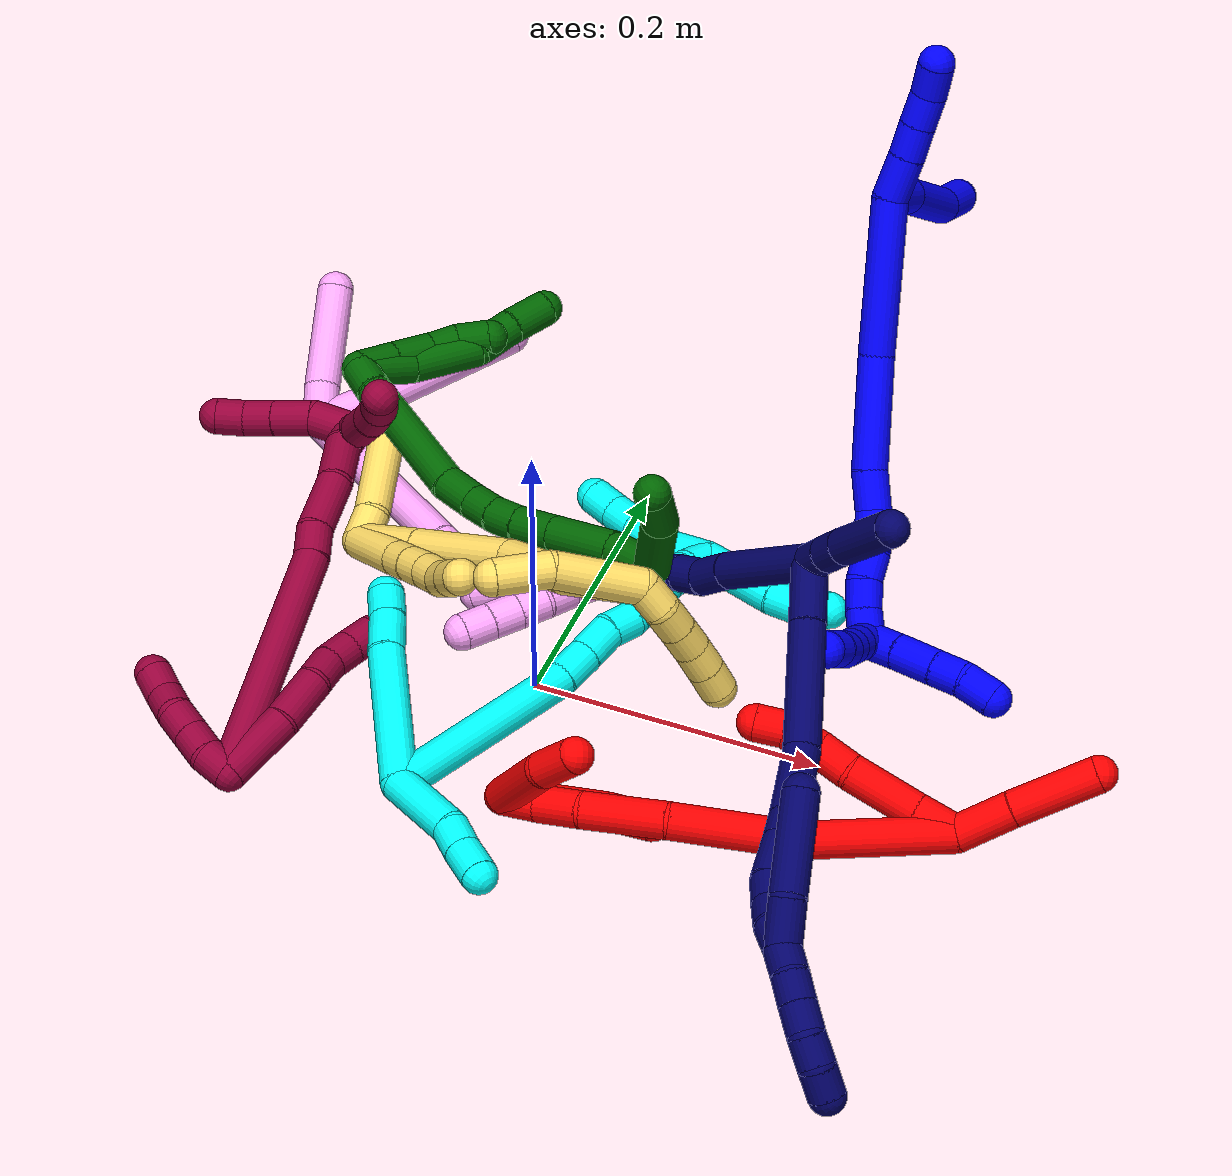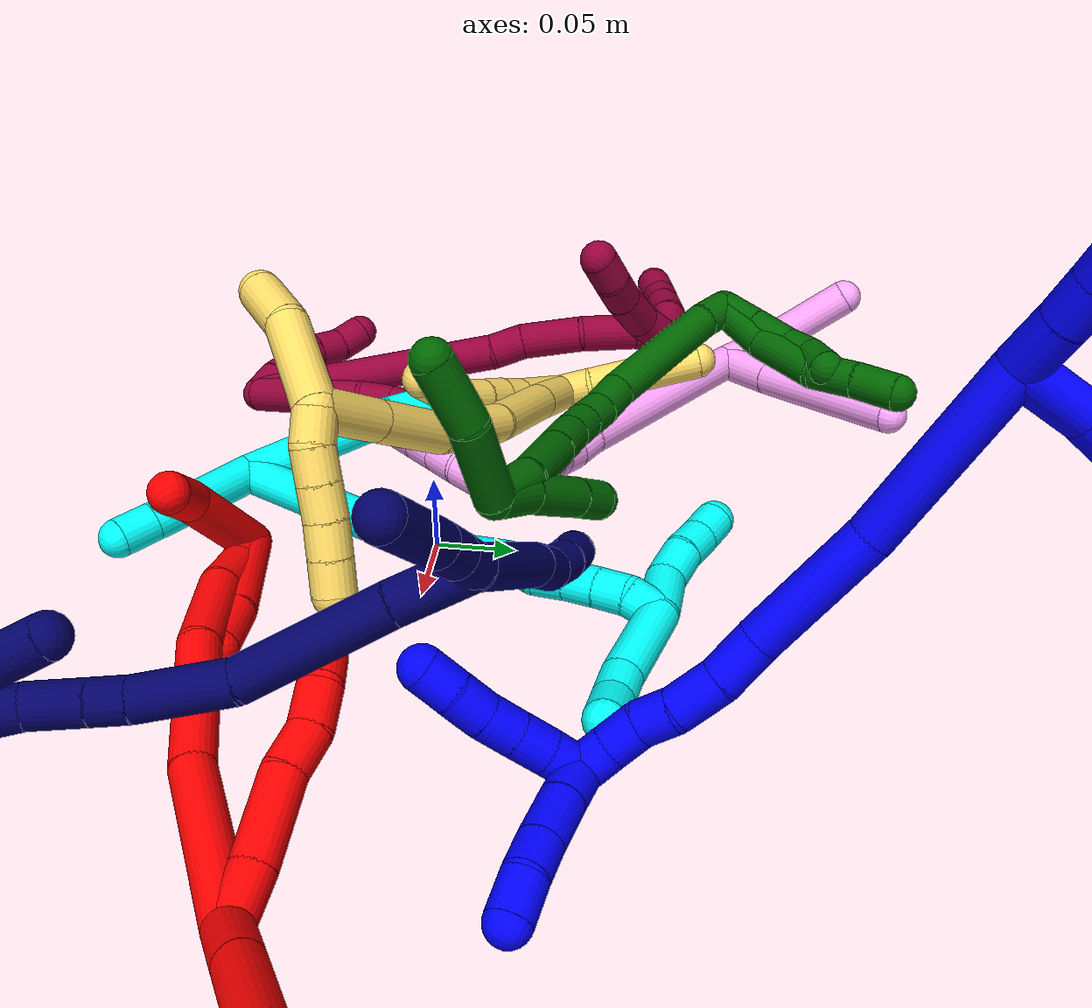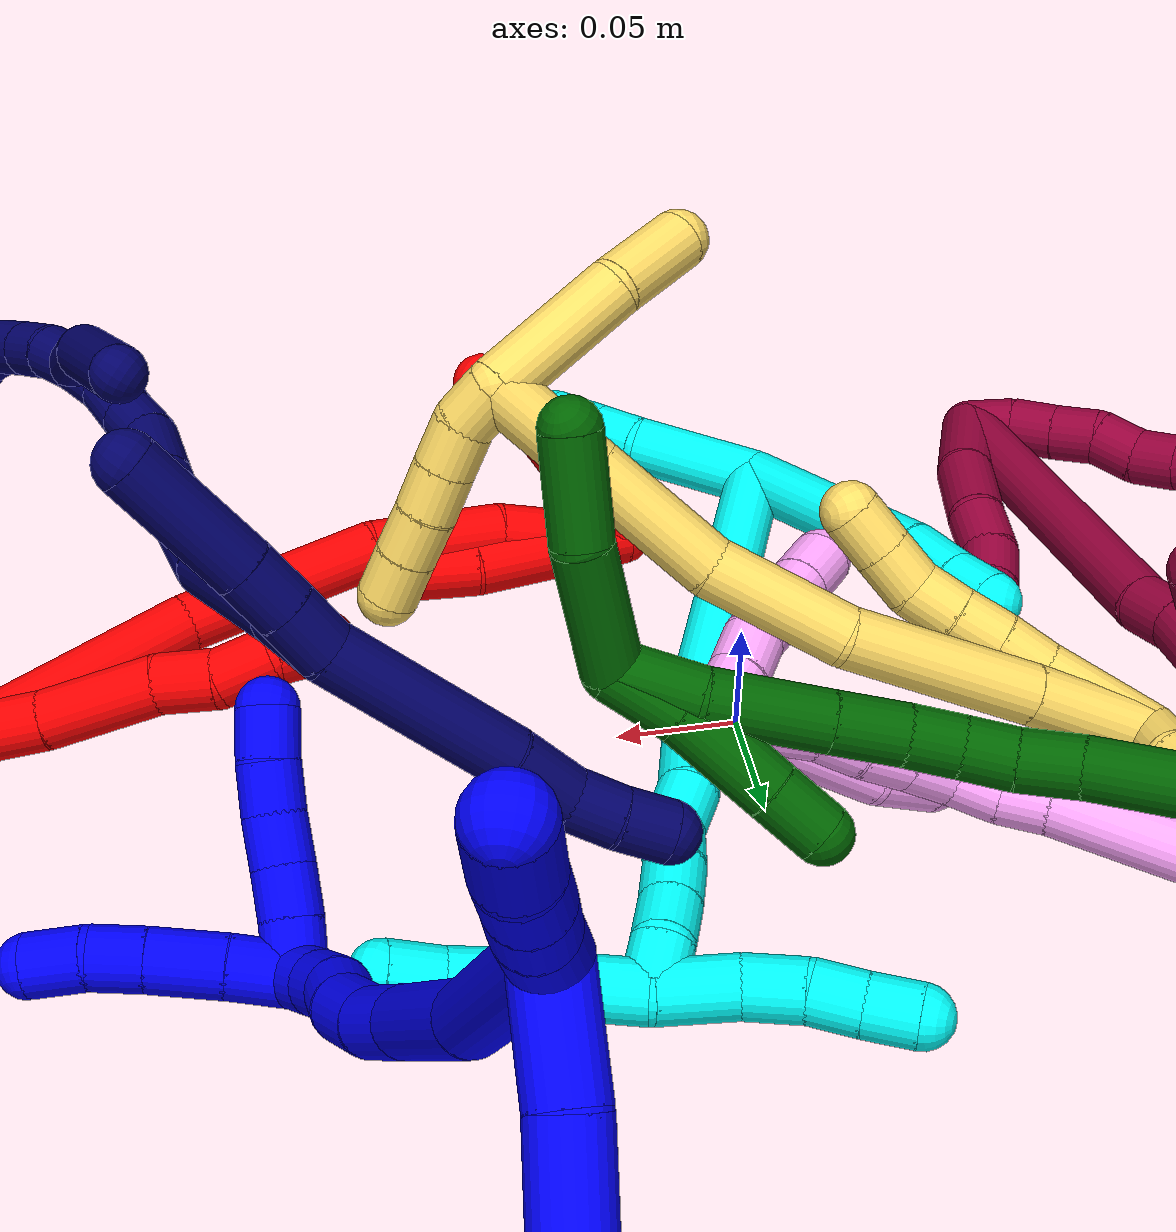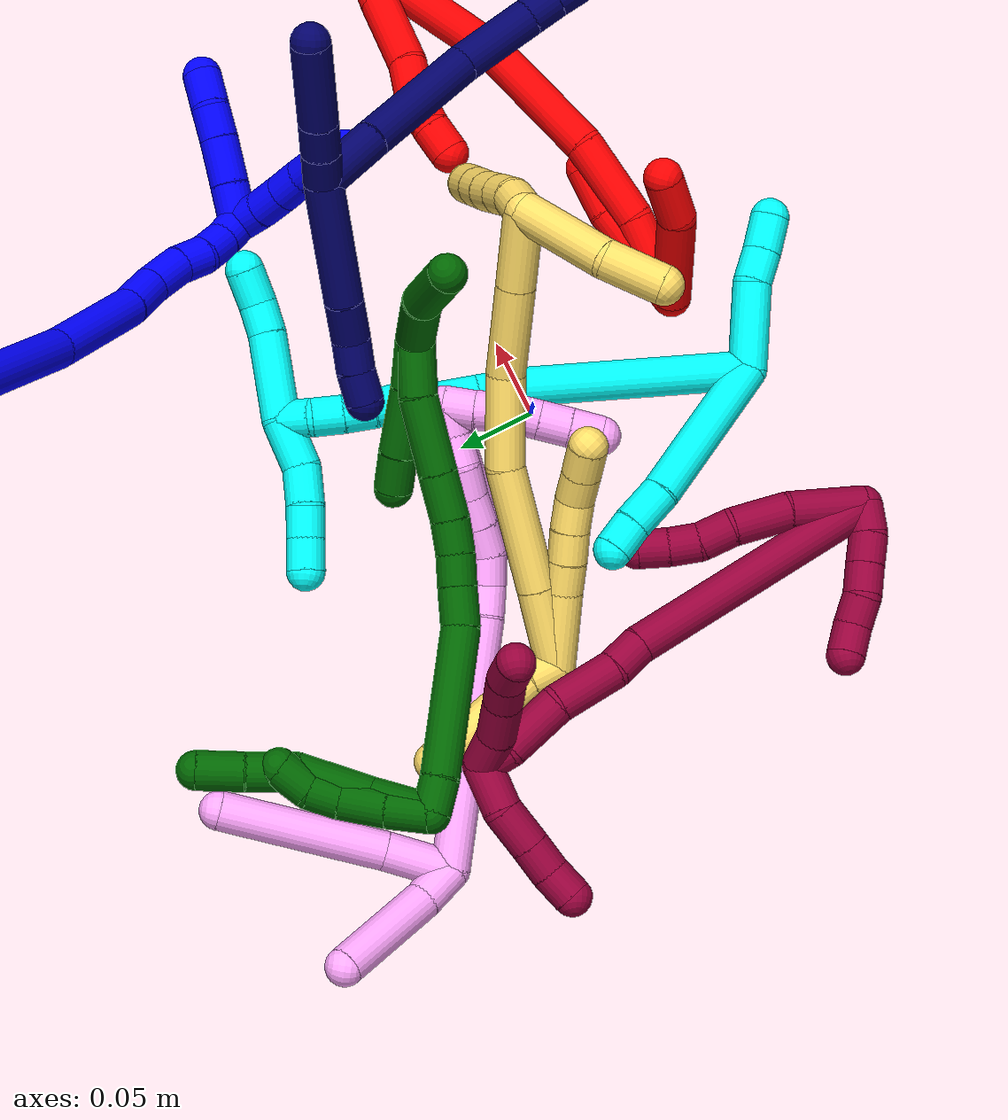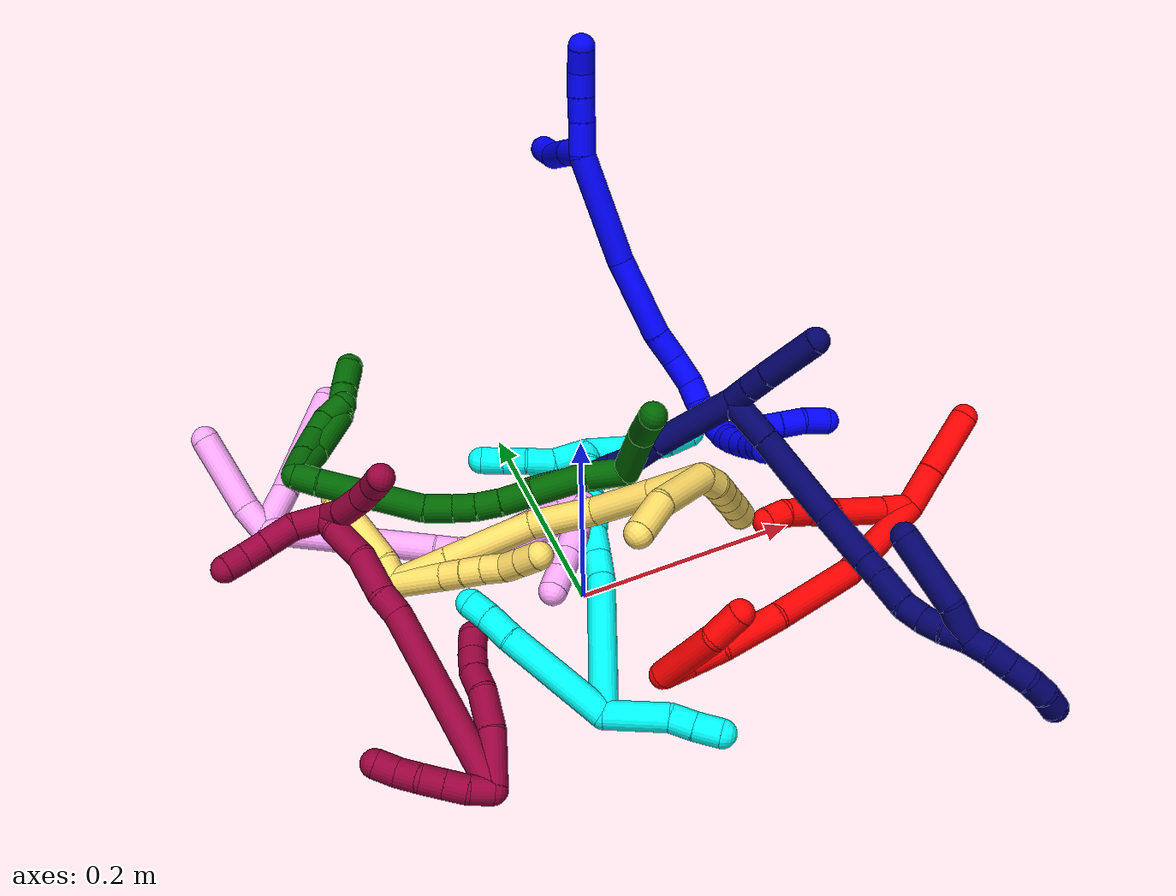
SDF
<sdf version="1.7">
 <world name="default">
  <plugin name="TubeGeneratorPlugin" filename="libtube_generator_plugin.so"/>
  <model name="photoneo_s_sensor">
   <static>1</static>
   <pose>0 0 2 1.57079 1.57079 3.14159</pose>
   <link name="link">
    <inertial><mass>0.1</mass></inertial>
    <sensor name="sensor" type="depth">
     <update_rate>30</update_rate>
     <camera>
      <horizontal_fov>1.22</horizontal_fov>
      <image><width>1920</width><height>1200</height><format>B8G8R8</format></image>
      <clip><near>0.1</near><far>4</far></clip>
      <depth_camera><output>points</output></depth_camera>
     </camera>
     <plugin name="camera_plugin" filename="libgazebo_ros_depth_camera.so">
      <baseline>0.2</baseline>
      <alwaysOn>1</alwaysOn>
      <updateRate>0.0</updateRate>
      <cameraName>camera_ir</cameraName>
      <imageTopicName>/camera/color/image_raw</imageTopicName>
      <cameraInfoTopicName>/camera/color/camera_info</cameraInfoTopicName>
      <depthImageTopicName>/camera/depth/image_raw</depthImageTopicName>
      <depthImageCameraInfoTopicName>/camera/depth/camera_info</depthImageCameraInfoTopicName>
      <pointCloudTopicName>/camera/depth/points</pointCloudTopicName>
      <frameName>fr_optical</frameName>
      <pointCloudCutoff>0.1</pointCloudCutoff>
      <pointCloudCutoffMax>2.0</pointCloudCutoffMax>
      <distortionK1>0</distortionK1>
      <distortionK2>0</distortionK2>
      <distortionK3>0</distortionK3>
      <distortionT1>0</distortionT1>
      <distortionT2>0</distortionT2>
      <CxPrime>0</CxPrime>
      <Cx>0</Cx>
      <Cy>0</Cy>
      <focalLength>0</focalLength>
      <hackBaseline>0</hackBaseline>
     </plugin>
    </sensor>
   </link>
  </model>
  <gravity>0 0 -9.8</gravity>
  <magnetic_field>6e-06 2.3e-05 -4.2e-05</magnetic_field>
  <atmosphere type="adiabatic"/>
  <physics name="default_physics" default="0" type="ode">
   <max_step_size>0.003</max_step_size>
   <real_time_factor>1</real_time_factor>
   <real_time_update_rate>1000</real_time_update_rate>
   <max_contacts>10000</max_contacts>
   <ode>
    <solver>
     <type>quick</type>
     <iters>100</iters>
     <sor>1.3</sor>
     <use_dynamic_moi_rescaling>0</use_dynamic_moi_rescaling>
    </solver>
    <constraints>
     <contact_max_correcting_vel>0</contact_max_correcting_vel>
     <contact_surface_layer>0.001</contact_surface_layer>
     <cfm>0</cfm>
     <erp>0.2</erp>
    </constraints>
   </ode>
  </physics>
  <scene><ambient>0.4 0.4 0.4 1</ambient><background>0.7 0.7 0.7 1</background><shadows>0</shadows></scene>
  <audio><device>default</device></audio>
  <spherical_coordinates>
   <surface_model>EARTH_WGS84</surface_model>
   <latitude_deg>0</latitude_deg>
   <longitude_deg>0</longitude_deg>
   <elevation>0</elevation>
   <heading_deg>0</heading_deg>
  </spherical_coordinates>
  <model name="bin">
   <static>1</static>
   <link name="bottom">
    <collision name="collision-bottom">
     <pose>0 0 -0.01 0 -0 0</pose>
     <geometry><box><size>0.8 0.6 0.02</size></box></geometry>
     <surface>
      <friction><ode><mu>100</mu><mu2>100</mu2></ode></friction>
      <contact><collide_bitmask>65535</collide_bitmask></contact>
     </surface>
    </collision>
   </link>
   <link name="west_wall">
    <collision name="collision-west_wall">
     <pose>-0.41 0 0.1 0 -0 0</pose>
     <geometry><box><size>0.02 0.6 0.2</size></box></geometry>
     <surface>
      <friction><ode><mu>100</mu><mu2>100</mu2></ode></friction>
      <contact><collide_bitmask>65535</collide_bitmask></contact>
     </surface>
    </collision>
   </link>
   <link name="east_wall">
    <collision name="collision-east_wall">
     <pose>0.41 0 0.1 0 -0 0</pose>
     <geometry><box><size>0.02 0.6 0.2</size></box></geometry>
     <surface>
      <friction><ode><mu>100</mu><mu2>100</mu2></ode></friction>
      <contact><collide_bitmask>65535</collide_bitmask></contact>
     </surface>
    </collision>
   </link>
   <link name="south_wall">
    <collision name="collision-south_wall">
     <pose>0 -0.31 0.1 0 -0 0</pose>
     <geometry><box><size>0.8 0.02 0.2</size></box></geometry>
     <surface>
      <friction><ode><mu>100</mu><mu2>100</mu2></ode></friction>
      <contact><collide_bitmask>65535</collide_bitmask></contact>
     </surface>
    </collision>
   </link>
   <link name="north_wall">
    <collision name="collision-north_wall">
     <pose>0 0.31 0.1 0 -0 0</pose>
     <geometry><box><size>0.8 0.02 0.2</size></box></geometry>
     <surface>
      <friction><ode><mu>100</mu><mu2>100</mu2></ode></friction>
      <contact><collide_bitmask>65535</collide_bitmask></contact>
     </surface>
    </collision>
   </link>
  </model>
  <model name="1">
   <static>0</static>
   <link name="1">
    <collision name="collision-cylinder-e_1_2_8">
     <pose>-0.007686 -0.001689 0.018577 0.090664 -0.390823 -0.017958</pose>
     <geometry><cylinder><radius>0.0125</radius><length>0.040349</length></cylinder></geometry>
     <surface>
      <friction><ode><mu>1.16</mu><mu2>1.16</mu2><slip1>0</slip1><slip2>0</slip2></ode></friction>
      <contact><ode><kp>1e+06</kp><kd>1</kd><max_vel>0</max_vel><min_depth>0.001</min_depth></ode></contact>
     </surface>
    </collision>
    <visual name="visual-cylinder-e_1_2_8">
     <pose>-0.007686 -0.001689 0.018577 0.090664 -0.390823 -0.017958</pose>
     <geometry><cylinder><radius>0.0125</radius><length>0.040349</length></cylinder></geometry>
     <material><ambient>0 0 1 1</ambient></material>
    </visual>
    <collision name="collision-cylinder-e_2_8_9">
     <pose>-0.031638 -0.002011 0.070503 -0.040973 -0.453503 0.009455</pose>
     <geometry><cylinder><radius>0.0125</radius><length>0.07426</length></cylinder></geometry>
     <surface>
      <friction><ode><mu>1.16</mu><mu2>1.16</mu2><slip1>0</slip1><slip2>0</slip2></ode></friction>
      <contact><ode><kp>1e+06</kp><kd>1</kd><max_vel>0</max_vel><min_depth>0.001</min_depth></ode></contact>
     </surface>
    </collision>
    <visual name="visual-cylinder-e_2_8_9">
     <pose>-0.031638 -0.002011 0.070503 -0.040973 -0.453503 0.009455</pose>
     <geometry><cylinder><radius>0.0125</radius><length>0.07426</length></cylinder></geometry>
     <material><ambient>0 0 1 1</ambient></material>
    </visual>
    <collision name="collision-cylinder-e_3_9_6">
     <pose>-0.052332 -0.002877 0.120838 0.130732 -0.2528 -0.016636</pose>
     <geometry><cylinder><radius>0.0125</radius><length>0.03539</length></cylinder></geometry>
     <surface>
      <friction><ode><mu>1.16</mu><mu2>1.16</mu2><slip1>0</slip1><slip2>0</slip2></ode></friction>
      <contact><ode><kp>1e+06</kp><kd>1</kd><max_vel>0</max_vel><min_depth>0.001</min_depth></ode></contact>
     </surface>
    </collision>
    <visual name="visual-cylinder-e_3_9_6">
     <pose>-0.052332 -0.002877 0.120838 0.130732 -0.2528 -0.016636</pose>
     <geometry><cylinder><radius>0.0125</radius><length>0.03539</length></cylinder></geometry>
     <material><ambient>0 0 1 1</ambient></material>
    </visual>
    <collision name="collision-cylinder-e_1_2_10">
     <pose>0.014425 -0.004926 0.003274 0.984275 1.18169 0.690453</pose>
     <geometry><cylinder><radius>0.0125</radius><length>0.031181</length></cylinder></geometry>
     <surface>
      <friction><ode><mu>1.16</mu><mu2>1.16</mu2><slip1>0</slip1><slip2>0</slip2></ode></friction>
      <contact><ode><kp>1e+06</kp><kd>1</kd><max_vel>0</max_vel><min_depth>0.001</min_depth></ode></contact>
     </surface>
    </collision>
    <visual name="visual-cylinder-e_1_2_10">
     <pose>0.014425 -0.004926 0.003274 0.984275 1.18169 0.690453</pose>
     <geometry><cylinder><radius>0.0125</radius><length>0.031181</length></cylinder></geometry>
     <material><ambient>0 0 1 1</ambient></material>
    </visual>
    <collision name="collision-cylinder-e_2_10_11">
     <pose>0.03946 -0.013963 0.008474 1.13236 1.16648 0.794184</pose>
     <geometry><cylinder><radius>0.0125</radius><length>0.023081</length></cylinder></geometry>
     <surface>
      <friction><ode><mu>1.16</mu><mu2>1.16</mu2><slip1>0</slip1><slip2>0</slip2></ode></friction>
      <contact><ode><kp>1e+06</kp><kd>1</kd><max_vel>0</max_vel><min_depth>0.001</min_depth></ode></contact>
     </surface>
    </collision>
    <visual name="visual-cylinder-e_2_10_11">
     <pose>0.03946 -0.013963 0.008474 1.13236 1.16648 0.794184</pose>
     <geometry><cylinder><radius>0.0125</radius><length>0.023081</length></cylinder></geometry>
     <material><ambient>0 0 1 1</ambient></material>
    </visual>
    <collision name="collision-cylinder-e_3_11_12">
     <pose>0.060684 -0.021762 0.012093 1.1409 1.20559 0.831665</pose>
     <geometry><cylinder><radius>0.0125</radius><length>0.022727</length></cylinder></geometry>
     <surface>
      <friction><ode><mu>1.16</mu><mu2>1.16</mu2><slip1>0</slip1><slip2>0</slip2></ode></friction>
      <contact><ode><kp>1e+06</kp><kd>1</kd><max_vel>0</max_vel><min_depth>0.001</min_depth></ode></contact>
     </surface>
    </collision>
    <visual name="visual-cylinder-e_3_11_12">
     <pose>0.060684 -0.021762 0.012093 1.1409 1.20559 0.831665</pose>
     <geometry><cylinder><radius>0.0125</radius><length>0.022727</length></cylinder></geometry>
     <material><ambient>0 0 1 1</ambient></material>
    </visual>
    <collision name="collision-cylinder-e_4_12_5">
     <pose>0.082166 -0.029162 0.013081 1.75805 1.23636 1.41889</pose>
     <geometry><cylinder><radius>0.0125</radius><length>0.023011</length></cylinder></geometry>
     <surface>
      <friction><ode><mu>1.16</mu><mu2>1.16</mu2><slip1>0</slip1><slip2>0</slip2></ode></friction>
      <contact><ode><kp>1e+06</kp><kd>1</kd><max_vel>0</max_vel><min_depth>0.001</min_depth></ode></contact>
     </surface>
    </collision>
    <visual name="visual-cylinder-e_4_12_5">
     <pose>0.082166 -0.029162 0.013081 1.75805 1.23636 1.41889</pose>
     <geometry><cylinder><radius>0.0125</radius><length>0.023011</length></cylinder></geometry>
     <material><ambient>0 0 1 1</ambient></material>
    </visual>
    <collision name="collision-cylinder-e_1_2_13">
     <pose>-0.04051 0.032635 -0.011371 -1.90606 -0.864504 1.15176</pose>
     <geometry><cylinder><radius>0.0125</radius><length>0.106497</length></cylinder></geometry>
     <surface>
      <friction><ode><mu>1.16</mu><mu2>1.16</mu2><slip1>0</slip1><slip2>0</slip2></ode></friction>
      <contact><ode><kp>1e+06</kp><kd>1</kd><max_vel>0</max_vel><min_depth>0.001</min_depth></ode></contact>
     </surface>
    </collision>
    <visual name="visual-cylinder-e_1_2_13">
     <pose>-0.04051 0.032635 -0.011371 -1.90606 -0.864504 1.15176</pose>
     <geometry><cylinder><radius>0.0125</radius><length>0.106497</length></cylinder></geometry>
     <material><ambient>0 0 1 1</ambient></material>
    </visual>
    <collision name="collision-cylinder-e_2_13_14">
     <pose>-0.106628 0.091345 -0.035203 -2.01663 -0.725075 1.0833</pose>
     <geometry><cylinder><radius>0.0125</radius><length>0.077224</length></cylinder></geometry>
     <surface>
      <friction><ode><mu>1.16</mu><mu2>1.16</mu2><slip1>0</slip1><slip2>0</slip2></ode></friction>
      <contact><ode><kp>1e+06</kp><kd>1</kd><max_vel>0</max_vel><min_depth>0.001</min_depth></ode></contact>
     </surface>
    </collision>
    <visual name="visual-cylinder-e_2_13_14">
     <pose>-0.106628 0.091345 -0.035203 -2.01663 -0.725075 1.0833</pose>
     <geometry><cylinder><radius>0.0125</radius><length>0.077224</length></cylinder></geometry>
     <material><ambient>0 0 1 1</ambient></material>
    </visual>
    <collision name="collision-cylinder-e_3_14_15">
     <pose>-0.139929 0.128512 -0.051691 -1.919 -0.577773 0.802143</pose>
     <geometry><cylinder><radius>0.0125</radius><length>0.028176</length></cylinder></geometry>
     <surface>
      <friction><ode><mu>1.16</mu><mu2>1.16</mu2><slip1>0</slip1><slip2>0</slip2></ode></friction>
      <contact><ode><kp>1e+06</kp><kd>1</kd><max_vel>0</max_vel><min_depth>0.001</min_depth></ode></contact>
     </surface>
    </collision>
    <visual name="visual-cylinder-e_3_14_15">
     <pose>-0.139929 0.128512 -0.051691 -1.919 -0.577773 0.802143</pose>
     <geometry><cylinder><radius>0.0125</radius><length>0.028176</length></cylinder></geometry>
     <material><ambient>0 0 1 1</ambient></material>
    </visual>
    <collision name="collision-cylinder-e_4_15_16">
     <pose>-0.154644 0.14971 -0.062241 -2.14402 -0.528348 0.921804</pose>
     <geometry><cylinder><radius>0.0125</radius><length>0.027853</length></cylinder></geometry>
     <surface>
      <friction><ode><mu>1.16</mu><mu2>1.16</mu2><slip1>0</slip1><slip2>0</slip2></ode></friction>
      <contact><ode><kp>1e+06</kp><kd>1</kd><max_vel>0</max_vel><min_depth>0.001</min_depth></ode></contact>
     </surface>
    </collision>
    <visual name="visual-cylinder-e_4_15_16">
     <pose>-0.154644 0.14971 -0.062241 -2.14402 -0.528348 0.921804</pose>
     <geometry><cylinder><radius>0.0125</radius><length>0.027853</length></cylinder></geometry>
     <material><ambient>0 0 1 1</ambient></material>
    </visual>
    <collision name="collision-cylinder-e_5_16_17">
     <pose>-0.167298 0.165306 -0.075022 -2.42137 -0.594911 1.36661</pose>
     <geometry><cylinder><radius>0.0125</radius><length>0.020104</length></cylinder></geometry>
     <surface>
      <friction><ode><mu>1.16</mu><mu2>1.16</mu2><slip1>0</slip1><slip2>0</slip2></ode></friction>
      <contact><ode><kp>1e+06</kp><kd>1</kd><max_vel>0</max_vel><min_depth>0.001</min_depth></ode></contact>
     </surface>
    </collision>
    <visual name="visual-cylinder-e_5_16_17">
     <pose>-0.167298 0.165306 -0.075022 -2.42137 -0.594911 1.36661</pose>
     <geometry><cylinder><radius>0.0125</radius><length>0.020104</length></cylinder></geometry>
     <material><ambient>0 0 1 1</ambient></material>
    </visual>
    <collision name="collision-cylinder-e_6_17_18">
     <pose>-0.17822 0.178196 -0.085561 -2.09543 -0.554056 0.916186</pose>
     <geometry><cylinder><radius>0.0125</radius><length>0.020106</length></cylinder></geometry>
     <surface>
      <friction><ode><mu>1.16</mu><mu2>1.16</mu2><slip1>0</slip1><slip2>0</slip2></ode></friction>
      <contact><ode><kp>1e+06</kp><kd>1</kd><max_vel>0</max_vel><min_depth>0.001</min_depth></ode></contact>
     </surface>
    </collision>
    <visual name="visual-cylinder-e_6_17_18">
     <pose>-0.17822 0.178196 -0.085561 -2.09543 -0.554056 0.916186</pose>
     <geometry><cylinder><radius>0.0125</radius><length>0.020106</length></cylinder></geometry>
     <material><ambient>0 0 1 1</ambient></material>
    </visual>
    <collision name="collision-cylinder-e_7_18_1">
     <pose>-0.187645 0.193728 -0.093985 -2.04177 -0.425395 0.677475</pose>
     <geometry><cylinder><radius>0.0125</radius><length>0.02004</length></cylinder></geometry>
     <surface>
      <friction><ode><mu>1.16</mu><mu2>1.16</mu2><slip1>0</slip1><slip2>0</slip2></ode></friction>
      <contact><ode><kp>1e+06</kp><kd>1</kd><max_vel>0</max_vel><min_depth>0.001</min_depth></ode></contact>
     </surface>
    </collision>
    <visual name="visual-cylinder-e_7_18_1">
     <pose>-0.187645 0.193728 -0.093985 -2.04177 -0.425395 0.677475</pose>
     <geometry><cylinder><radius>0.0125</radius><length>0.02004</length></cylinder></geometry>
     <material><ambient>0 0 1 1</ambient></material>
    </visual>
    <collision name="collision-cylinder-e_1_1_19">
     <pose>-0.188187 0.202637 -0.107426 -3.05843 0.367494 -2.70112</pose>
     <geometry><cylinder><radius>0.0125</radius><length>0.02</length></cylinder></geometry>
     <surface>
      <friction><ode><mu>1.16</mu><mu2>1.16</mu2><slip1>0</slip1><slip2>0</slip2></ode></friction>
      <contact><ode><kp>1e+06</kp><kd>1</kd><max_vel>0</max_vel><min_depth>0.001</min_depth></ode></contact>
     </surface>
    </collision>
    <visual name="visual-cylinder-e_1_1_19">
     <pose>-0.188187 0.202637 -0.107426 -3.05843 0.367494 -2.70112</pose>
     <geometry><cylinder><radius>0.0125</radius><length>0.02</length></cylinder></geometry>
     <material><ambient>0 0 1 1</ambient></material>
    </visual>
    <collision name="collision-cylinder-e_2_19_20">
     <pose>-0.180346 0.204658 -0.125693 -3.00352 0.438803 -2.54021</pose>
     <geometry><cylinder><radius>0.0125</radius><length>0.02</length></cylinder></geometry>
     <surface>
      <friction><ode><mu>1.16</mu><mu2>1.16</mu2><slip1>0</slip1><slip2>0</slip2></ode></friction>
      <contact><ode><kp>1e+06</kp><kd>1</kd><max_vel>0</max_vel><min_depth>0.001</min_depth></ode></contact>
     </surface>
    </collision>
    <visual name="visual-cylinder-e_2_19_20">
     <pose>-0.180346 0.204658 -0.125693 -3.00352 0.438803 -2.54021</pose>
     <geometry><cylinder><radius>0.0125</radius><length>0.02</length></cylinder></geometry>
     <material><ambient>0 0 1 1</ambient></material>
    </visual>
    <collision name="collision-cylinder-e_3_20_21">
     <pose>-0.171495 0.207149 -0.14345 -3.00088 0.478201 -2.57872</pose>
     <geometry><cylinder><radius>0.0125</radius><length>0.02</length></cylinder></geometry>
     <surface>
      <friction><ode><mu>1.16</mu><mu2>1.16</mu2><slip1>0</slip1><slip2>0</slip2></ode></friction>
      <contact><ode><kp>1e+06</kp><kd>1</kd><max_vel>0</max_vel><min_depth>0.001</min_depth></ode></contact>
     </surface>
    </collision>
    <visual name="visual-cylinder-e_3_20_21">
     <pose>-0.171495 0.207149 -0.14345 -3.00088 0.478201 -2.57872</pose>
     <geometry><cylinder><radius>0.0125</radius><length>0.02</length></cylinder></geometry>
     <material><ambient>0 0 1 1</ambient></material>
    </visual>
    <collision name="collision-cylinder-e_4_21_22">
     <pose>-0.161823 0.208603 -0.160857 -3.11741 0.531699 -3.05282</pose>
     <geometry><cylinder><radius>0.0125</radius><length>0.02</length></cylinder></geometry>
     <surface>
      <friction><ode><mu>1.16</mu><mu2>1.16</mu2><slip1>0</slip1><slip2>0</slip2></ode></friction>
      <contact><ode><kp>1e+06</kp><kd>1</kd><max_vel>0</max_vel><min_depth>0.001</min_depth></ode></contact>
     </surface>
    </collision>
    <visual name="visual-cylinder-e_4_21_22">
     <pose>-0.161823 0.208603 -0.160857 -3.11741 0.531699 -3.05282</pose>
     <geometry><cylinder><radius>0.0125</radius><length>0.02</length></cylinder></geometry>
     <material><ambient>0 0 1 1</ambient></material>
    </visual>
    <collision name="collision-cylinder-e_5_22_4">
     <pose>-0.152695 0.208607 -0.178611 3.11924 0.417861 3.03627</pose>
     <geometry><cylinder><radius>0.0125</radius><length>0.02</length></cylinder></geometry>
     <surface>
      <friction><ode><mu>1.16</mu><mu2>1.16</mu2><slip1>0</slip1><slip2>0</slip2></ode></friction>
      <contact><ode><kp>1e+06</kp><kd>1</kd><max_vel>0</max_vel><min_depth>0.001</min_depth></ode></contact>
     </surface>
    </collision>
    <visual name="visual-cylinder-e_5_22_4">
     <pose>-0.152695 0.208607 -0.178611 3.11924 0.417861 3.03627</pose>
     <geometry><cylinder><radius>0.0125</radius><length>0.02</length></cylinder></geometry>
     <material><ambient>0 0 1 1</ambient></material>
    </visual>
    <collision name="collision-cylinder-e_1_1_23">
     <pose>-0.185628 0.21282 -0.097832 -1.54393 0.511348 -0.498352</pose>
     <geometry><cylinder><radius>0.0125</radius><length>0.025142</length></cylinder></geometry>
     <surface>
      <friction><ode><mu>1.16</mu><mu2>1.16</mu2><slip1>0</slip1><slip2>0</slip2></ode></friction>
      <contact><ode><kp>1e+06</kp><kd>1</kd><max_vel>0</max_vel><min_depth>0.001</min_depth></ode></contact>
     </surface>
    </collision>
    <visual name="visual-cylinder-e_1_1_23">
     <pose>-0.185628 0.21282 -0.097832 -1.54393 0.511348 -0.498352</pose>
     <geometry><cylinder><radius>0.0125</radius><length>0.025142</length></cylinder></geometry>
     <material><ambient>0 0 1 1</ambient></material>
    </visual>
    <collision name="collision-cylinder-e_2_23_24">
     <pose>-0.172826 0.237163 -0.096824 -1.5176 0.460626 -0.437523</pose>
     <geometry><cylinder><radius>0.0125</radius><length>0.029924</length></cylinder></geometry>
     <surface>
      <friction><ode><mu>1.16</mu><mu2>1.16</mu2><slip1>0</slip1><slip2>0</slip2></ode></friction>
      <contact><ode><kp>1e+06</kp><kd>1</kd><max_vel>0</max_vel><min_depth>0.001</min_depth></ode></contact>
     </surface>
    </collision>
    <visual name="visual-cylinder-e_2_23_24">
     <pose>-0.172826 0.237163 -0.096824 -1.5176 0.460626 -0.437523</pose>
     <geometry><cylinder><radius>0.0125</radius><length>0.029924</length></cylinder></geometry>
     <material><ambient>0 0 1 1</ambient></material>
    </visual>
    <collision name="collision-cylinder-e_3_24_25">
     <pose>-0.161601 0.260152 -0.095164 -1.47242 0.442562 -0.402198</pose>
     <geometry><cylinder><radius>0.0125</radius><length>0.021363</length></cylinder></geometry>
     <surface>
      <friction><ode><mu>1.16</mu><mu2>1.16</mu2><slip1>0</slip1><slip2>0</slip2></ode></friction>
      <contact><ode><kp>1e+06</kp><kd>1</kd><max_vel>0</max_vel><min_depth>0.001</min_depth></ode></contact>
     </surface>
    </collision>
    <visual name="visual-cylinder-e_3_24_25">
     <pose>-0.161601 0.260152 -0.095164 -1.47242 0.442562 -0.402198</pose>
     <geometry><cylinder><radius>0.0125</radius><length>0.021363</length></cylinder></geometry>
     <material><ambient>0 0 1 1</ambient></material>
    </visual>
    <collision name="collision-cylinder-e_4_25_3">
     <pose>-0.154773 0.281191 -0.092449 -1.41747 0.192361 -0.165053</pose>
     <geometry><cylinder><radius>0.0125</radius><length>0.023571</length></cylinder></geometry>
     <surface>
      <friction><ode><mu>1.16</mu><mu2>1.16</mu2><slip1>0</slip1><slip2>0</slip2></ode></friction>
      <contact><ode><kp>1e+06</kp><kd>1</kd><max_vel>0</max_vel><min_depth>0.001</min_depth></ode></contact>
     </surface>
    </collision>
    <visual name="visual-cylinder-e_4_25_3">
     <pose>-0.154773 0.281191 -0.092449 -1.41747 0.192361 -0.165053</pose>
     <geometry><cylinder><radius>0.0125</radius><length>0.023571</length></cylinder></geometry>
     <material><ambient>0 0 1 1</ambient></material>
    </visual>
    <collision name="collision-sphere-3">
     <pose>-0.15252 0.292623 -0.090682 0 -0 0</pose>
     <geometry><sphere><radius>0.0125</radius></sphere></geometry>
     <surface>
      <friction><ode><mu>1.16</mu><mu2>1.16</mu2><slip1>0</slip1><slip2>0</slip2></ode></friction>
      <contact><ode><kp>1e+06</kp><kd>1</kd><max_vel>0</max_vel><min_depth>0.001</min_depth></ode></contact>
     </surface>
    </collision>
    <visual name="visual-sphere-3">
     <pose>-0.15252 0.292623 -0.090682 0 -0 0</pose>
     <geometry><sphere><radius>0.0125</radius></sphere></geometry>
     <material><ambient>0 0 1 1</ambient></material>
    </visual>
    <collision name="collision-sphere-25">
     <pose>-0.157026 0.269758 -0.094216 0 -0 0</pose>
     <geometry><sphere><radius>0.0125</radius></sphere></geometry>
     <surface>
      <friction><ode><mu>1.16</mu><mu2>1.16</mu2><slip1>0</slip1><slip2>0</slip2></ode></friction>
      <contact><ode><kp>1e+06</kp><kd>1</kd><max_vel>0</max_vel><min_depth>0.001</min_depth></ode></contact>
     </surface>
    </collision>
    <visual name="visual-sphere-25">
     <pose>-0.157026 0.269758 -0.094216 0 -0 0</pose>
     <geometry><sphere><radius>0.0125</radius></sphere></geometry>
     <material><ambient>0 0 1 1</ambient></material>
    </visual>
    <collision name="collision-sphere-24">
     <pose>-0.166175 0.250547 -0.096112 0 -0 0</pose>
     <geometry><sphere><radius>0.0125</radius></sphere></geometry>
     <surface>
      <friction><ode><mu>1.16</mu><mu2>1.16</mu2><slip1>0</slip1><slip2>0</slip2></ode></friction>
      <contact><ode><kp>1e+06</kp><kd>1</kd><max_vel>0</max_vel><min_depth>0.001</min_depth></ode></contact>
     </surface>
    </collision>
    <visual name="visual-sphere-24">
     <pose>-0.166175 0.250547 -0.096112 0 -0 0</pose>
     <geometry><sphere><radius>0.0125</radius></sphere></geometry>
     <material><ambient>0 0 1 1</ambient></material>
    </visual>
    <collision name="collision-sphere-23">
     <pose>-0.179477 0.223779 -0.097537 0 -0 0</pose>
     <geometry><sphere><radius>0.0125</radius></sphere></geometry>
     <surface>
      <friction><ode><mu>1.16</mu><mu2>1.16</mu2><slip1>0</slip1><slip2>0</slip2></ode></friction>
      <contact><ode><kp>1e+06</kp><kd>1</kd><max_vel>0</max_vel><min_depth>0.001</min_depth></ode></contact>
     </surface>
    </collision>
    <visual name="visual-sphere-23">
     <pose>-0.179477 0.223779 -0.097537 0 -0 0</pose>
     <geometry><sphere><radius>0.0125</radius></sphere></geometry>
     <material><ambient>0 0 1 1</ambient></material>
    </visual>
    <collision name="collision-sphere-4">
     <pose>-0.148637 0.208403 -0.187749 0 -0 0</pose>
     <geometry><sphere><radius>0.0125</radius></sphere></geometry>
     <surface>
      <friction><ode><mu>1.16</mu><mu2>1.16</mu2><slip1>0</slip1><slip2>0</slip2></ode></friction>
      <contact><ode><kp>1e+06</kp><kd>1</kd><max_vel>0</max_vel><min_depth>0.001</min_depth></ode></contact>
     </surface>
    </collision>
    <visual name="visual-sphere-4">
     <pose>-0.148637 0.208403 -0.187749 0 -0 0</pose>
     <geometry><sphere><radius>0.0125</radius></sphere></geometry>
     <material><ambient>0 0 1 1</ambient></material>
    </visual>
    <collision name="collision-sphere-22">
     <pose>-0.156753 0.208811 -0.169474 0 -0 0</pose>
     <geometry><sphere><radius>0.0125</radius></sphere></geometry>
     <surface>
      <friction><ode><mu>1.16</mu><mu2>1.16</mu2><slip1>0</slip1><slip2>0</slip2></ode></friction>
      <contact><ode><kp>1e+06</kp><kd>1</kd><max_vel>0</max_vel><min_depth>0.001</min_depth></ode></contact>
     </surface>
    </collision>
    <visual name="visual-sphere-22">
     <pose>-0.156753 0.208811 -0.169474 0 -0 0</pose>
     <geometry><sphere><radius>0.0125</radius></sphere></geometry>
     <material><ambient>0 0 1 1</ambient></material>
    </visual>
    <collision name="collision-sphere-21">
     <pose>-0.166893 0.208394 -0.15224 0 -0 0</pose>
     <geometry><sphere><radius>0.0125</radius></sphere></geometry>
     <surface>
      <friction><ode><mu>1.16</mu><mu2>1.16</mu2><slip1>0</slip1><slip2>0</slip2></ode></friction>
      <contact><ode><kp>1e+06</kp><kd>1</kd><max_vel>0</max_vel><min_depth>0.001</min_depth></ode></contact>
     </surface>
    </collision>
    <visual name="visual-sphere-21">
     <pose>-0.166893 0.208394 -0.15224 0 -0 0</pose>
     <geometry><sphere><radius>0.0125</radius></sphere></geometry>
     <material><ambient>0 0 1 1</ambient></material>
    </visual>
    <collision name="collision-sphere-20">
     <pose>-0.176097 0.205904 -0.134659 0 -0 0</pose>
     <geometry><sphere><radius>0.0125</radius></sphere></geometry>
     <surface>
      <friction><ode><mu>1.16</mu><mu2>1.16</mu2><slip1>0</slip1><slip2>0</slip2></ode></friction>
      <contact><ode><kp>1e+06</kp><kd>1</kd><max_vel>0</max_vel><min_depth>0.001</min_depth></ode></contact>
     </surface>
    </collision>
    <visual name="visual-sphere-20">
     <pose>-0.176097 0.205904 -0.134659 0 -0 0</pose>
     <geometry><sphere><radius>0.0125</radius></sphere></geometry>
     <material><ambient>0 0 1 1</ambient></material>
    </visual>
    <collision name="collision-sphere-11">
     <pose>0.05007 -0.018073 0.010402 0 -0 0</pose>
     <geometry><sphere><radius>0.0125</radius></sphere></geometry>
     <surface>
      <friction><ode><mu>1.16</mu><mu2>1.16</mu2><slip1>0</slip1><slip2>0</slip2></ode></friction>
      <contact><ode><kp>1e+06</kp><kd>1</kd><max_vel>0</max_vel><min_depth>0.001</min_depth></ode></contact>
     </surface>
    </collision>
    <visual name="visual-sphere-11">
     <pose>0.05007 -0.018073 0.010402 0 -0 0</pose>
     <geometry><sphere><radius>0.0125</radius></sphere></geometry>
     <material><ambient>0 0 1 1</ambient></material>
    </visual>
    <collision name="collision-sphere-10">
     <pose>0.02885 -0.009852 0.006547 0 -0 0</pose>
     <geometry><sphere><radius>0.0125</radius></sphere></geometry>
     <surface>
      <friction><ode><mu>1.16</mu><mu2>1.16</mu2><slip1>0</slip1><slip2>0</slip2></ode></friction>
      <contact><ode><kp>1e+06</kp><kd>1</kd><max_vel>0</max_vel><min_depth>0.001</min_depth></ode></contact>
     </surface>
    </collision>
    <visual name="visual-sphere-10">
     <pose>0.02885 -0.009852 0.006547 0 -0 0</pose>
     <geometry><sphere><radius>0.0125</radius></sphere></geometry>
     <material><ambient>0 0 1 1</ambient></material>
    </visual>
    <collision name="collision-sphere-6">
     <pose>-0.056757 -0.00511 0.137825 0 -0 0</pose>
     <geometry><sphere><radius>0.0125</radius></sphere></geometry>
     <surface>
      <friction><ode><mu>1.16</mu><mu2>1.16</mu2><slip1>0</slip1><slip2>0</slip2></ode></friction>
      <contact><ode><kp>1e+06</kp><kd>1</kd><max_vel>0</max_vel><min_depth>0.001</min_depth></ode></contact>
     </surface>
    </collision>
    <visual name="visual-sphere-6">
     <pose>-0.056757 -0.00511 0.137825 0 -0 0</pose>
     <geometry><sphere><radius>0.0125</radius></sphere></geometry>
     <material><ambient>0 0 1 1</ambient></material>
    </visual>
    <collision name="collision-sphere-9">
     <pose>-0.047906 -0.000643 0.103852 0 -0 0</pose>
     <geometry><sphere><radius>0.0125</radius></sphere></geometry>
     <surface>
      <friction><ode><mu>1.16</mu><mu2>1.16</mu2><slip1>0</slip1><slip2>0</slip2></ode></friction>
      <contact><ode><kp>1e+06</kp><kd>1</kd><max_vel>0</max_vel><min_depth>0.001</min_depth></ode></contact>
     </surface>
    </collision>
    <visual name="visual-sphere-9">
     <pose>-0.047906 -0.000643 0.103852 0 -0 0</pose>
     <geometry><sphere><radius>0.0125</radius></sphere></geometry>
     <material><ambient>0 0 1 1</ambient></material>
    </visual>
    <collision name="collision-sphere-2">
     <geometry><sphere><radius>0.0125</radius></sphere></geometry>
     <surface>
      <friction><ode><mu>1.16</mu><mu2>1.16</mu2><slip1>0</slip1><slip2>0</slip2></ode></friction>
      <contact><ode><kp>1e+06</kp><kd>1</kd><max_vel>0</max_vel><min_depth>0.001</min_depth></ode></contact>
     </surface>
    </collision>
    <visual name="visual-sphere-2">
     <geometry><sphere><radius>0.0125</radius></sphere></geometry>
     <material><ambient>0 0 1 1</ambient></material>
    </visual>
    <collision name="collision-sphere-19">
     <pose>-0.184594 0.203412 -0.116726 0 -0 0</pose>
     <geometry><sphere><radius>0.0125</radius></sphere></geometry>
     <surface>
      <friction><ode><mu>1.16</mu><mu2>1.16</mu2><slip1>0</slip1><slip2>0</slip2></ode></friction>
      <contact><ode><kp>1e+06</kp><kd>1</kd><max_vel>0</max_vel><min_depth>0.001</min_depth></ode></contact>
     </surface>
    </collision>
    <visual name="visual-sphere-19">
     <pose>-0.184594 0.203412 -0.116726 0 -0 0</pose>
     <geometry><sphere><radius>0.0125</radius></sphere></geometry>
     <material><ambient>0 0 1 1</ambient></material>
    </visual>
    <collision name="collision-sphere-8">
     <pose>-0.015371 -0.003378 0.037154 0 -0 0</pose>
     <geometry><sphere><radius>0.0125</radius></sphere></geometry>
     <surface>
      <friction><ode><mu>1.16</mu><mu2>1.16</mu2><slip1>0</slip1><slip2>0</slip2></ode></friction>
      <contact><ode><kp>1e+06</kp><kd>1</kd><max_vel>0</max_vel><min_depth>0.001</min_depth></ode></contact>
     </surface>
    </collision>
    <visual name="visual-sphere-8">
     <pose>-0.015371 -0.003378 0.037154 0 -0 0</pose>
     <geometry><sphere><radius>0.0125</radius></sphere></geometry>
     <material><ambient>0 0 1 1</ambient></material>
    </visual>
    <collision name="collision-sphere-12">
     <pose>0.071298 -0.025451 0.013784 0 -0 0</pose>
     <geometry><sphere><radius>0.0125</radius></sphere></geometry>
     <surface>
      <friction><ode><mu>1.16</mu><mu2>1.16</mu2><slip1>0</slip1><slip2>0</slip2></ode></friction>
      <contact><ode><kp>1e+06</kp><kd>1</kd><max_vel>0</max_vel><min_depth>0.001</min_depth></ode></contact>
     </surface>
    </collision>
    <visual name="visual-sphere-12">
     <pose>0.071298 -0.025451 0.013784 0 -0 0</pose>
     <geometry><sphere><radius>0.0125</radius></sphere></geometry>
     <material><ambient>0 0 1 1</ambient></material>
    </visual>
    <collision name="collision-sphere-5">
     <pose>0.093034 -0.032872 0.012378 0 -0 0</pose>
     <geometry><sphere><radius>0.0125</radius></sphere></geometry>
     <surface>
      <friction><ode><mu>1.16</mu><mu2>1.16</mu2><slip1>0</slip1><slip2>0</slip2></ode></friction>
      <contact><ode><kp>1e+06</kp><kd>1</kd><max_vel>0</max_vel><min_depth>0.001</min_depth></ode></contact>
     </surface>
    </collision>
    <visual name="visual-sphere-5">
     <pose>0.093034 -0.032872 0.012378 0 -0 0</pose>
     <geometry><sphere><radius>0.0125</radius></sphere></geometry>
     <material><ambient>0 0 1 1</ambient></material>
    </visual>
    <collision name="collision-sphere-13">
     <pose>-0.08102 0.06527 -0.022741 0 -0 0</pose>
     <geometry><sphere><radius>0.0125</radius></sphere></geometry>
     <surface>
      <friction><ode><mu>1.16</mu><mu2>1.16</mu2><slip1>0</slip1><slip2>0</slip2></ode></friction>
      <contact><ode><kp>1e+06</kp><kd>1</kd><max_vel>0</max_vel><min_depth>0.001</min_depth></ode></contact>
     </surface>
    </collision>
    <visual name="visual-sphere-13">
     <pose>-0.08102 0.06527 -0.022741 0 -0 0</pose>
     <geometry><sphere><radius>0.0125</radius></sphere></geometry>
     <material><ambient>0 0 1 1</ambient></material>
    </visual>
    <collision name="collision-sphere-14">
     <pose>-0.132235 0.117419 -0.047665 0 -0 0</pose>
     <geometry><sphere><radius>0.0125</radius></sphere></geometry>
     <surface>
      <friction><ode><mu>1.16</mu><mu2>1.16</mu2><slip1>0</slip1><slip2>0</slip2></ode></friction>
      <contact><ode><kp>1e+06</kp><kd>1</kd><max_vel>0</max_vel><min_depth>0.001</min_depth></ode></contact>
     </surface>
    </collision>
    <visual name="visual-sphere-14">
     <pose>-0.132235 0.117419 -0.047665 0 -0 0</pose>
     <geometry><sphere><radius>0.0125</radius></sphere></geometry>
     <material><ambient>0 0 1 1</ambient></material>
    </visual>
    <collision name="collision-sphere-15">
     <pose>-0.147623 0.139605 -0.055718 0 -0 0</pose>
     <geometry><sphere><radius>0.0125</radius></sphere></geometry>
     <surface>
      <friction><ode><mu>1.16</mu><mu2>1.16</mu2><slip1>0</slip1><slip2>0</slip2></ode></friction>
      <contact><ode><kp>1e+06</kp><kd>1</kd><max_vel>0</max_vel><min_depth>0.001</min_depth></ode></contact>
     </surface>
    </collision>
    <visual name="visual-sphere-15">
     <pose>-0.147623 0.139605 -0.055718 0 -0 0</pose>
     <geometry><sphere><radius>0.0125</radius></sphere></geometry>
     <material><ambient>0 0 1 1</ambient></material>
    </visual>
    <collision name="collision-sphere-16">
     <pose>-0.161664 0.159815 -0.068764 0 -0 0</pose>
     <geometry><sphere><radius>0.0125</radius></sphere></geometry>
     <surface>
      <friction><ode><mu>1.16</mu><mu2>1.16</mu2><slip1>0</slip1><slip2>0</slip2></ode></friction>
      <contact><ode><kp>1e+06</kp><kd>1</kd><max_vel>0</max_vel><min_depth>0.001</min_depth></ode></contact>
     </surface>
    </collision>
    <visual name="visual-sphere-16">
     <pose>-0.161664 0.159815 -0.068764 0 -0 0</pose>
     <geometry><sphere><radius>0.0125</radius></sphere></geometry>
     <material><ambient>0 0 1 1</ambient></material>
    </visual>
    <collision name="collision-sphere-17">
     <pose>-0.172931 0.170797 -0.081279 0 -0 0</pose>
     <geometry><sphere><radius>0.0125</radius></sphere></geometry>
     <surface>
      <friction><ode><mu>1.16</mu><mu2>1.16</mu2><slip1>0</slip1><slip2>0</slip2></ode></friction>
      <contact><ode><kp>1e+06</kp><kd>1</kd><max_vel>0</max_vel><min_depth>0.001</min_depth></ode></contact>
     </surface>
    </collision>
    <visual name="visual-sphere-17">
     <pose>-0.172931 0.170797 -0.081279 0 -0 0</pose>
     <geometry><sphere><radius>0.0125</radius></sphere></geometry>
     <material><ambient>0 0 1 1</ambient></material>
    </visual>
    <collision name="collision-sphere-18">
     <pose>-0.18351 0.185595 -0.089843 0 -0 0</pose>
     <geometry><sphere><radius>0.0125</radius></sphere></geometry>
     <surface>
      <friction><ode><mu>1.16</mu><mu2>1.16</mu2><slip1>0</slip1><slip2>0</slip2></ode></friction>
      <contact><ode><kp>1e+06</kp><kd>1</kd><max_vel>0</max_vel><min_depth>0.001</min_depth></ode></contact>
     </surface>
    </collision>
    <visual name="visual-sphere-18">
     <pose>-0.18351 0.185595 -0.089843 0 -0 0</pose>
     <geometry><sphere><radius>0.0125</radius></sphere></geometry>
     <material><ambient>0 0 1 1</ambient></material>
    </visual>
    <collision name="collision-sphere-1">
     <pose>-0.19178 0.201861 -0.098126 0 -0 0</pose>
     <geometry><sphere><radius>0.0125</radius></sphere></geometry>
     <surface>
      <friction><ode><mu>1.16</mu><mu2>1.16</mu2><slip1>0</slip1><slip2>0</slip2></ode></friction>
      <contact><ode><kp>1e+06</kp><kd>1</kd><max_vel>0</max_vel><min_depth>0.001</min_depth></ode></contact>
     </surface>
    </collision>
    <visual name="visual-sphere-1">
     <pose>-0.19178 0.201861 -0.098126 0 -0 0</pose>
     <geometry><sphere><radius>0.0125</radius></sphere></geometry>
     <material><ambient>0 0 1 1</ambient></material>
    </visual>
    <inertial>
     <pose>-0.087222 0.096552 -0.033315 0 -0 0</pose>
     <mass>0.75</mass>
     <inertia><ixx>0.000184</ixx><ixy>0</ixy><ixz>0</ixz><iyy>0.00025</iyy><iyz>0</iyz><izz>9e-06</izz></inertia>
    </inertial>
   </link>
   <pose>0.131859 0.304192 0.22824 -2.22137 -1.09638 0.297261</pose>
  </model>
  <model name="2">
   <static>0</static>
   <link name="2">
    <collision name="collision-cylinder-e_1_2_8">
     <pose>-0.006293 -0.008594 -0.010582 2.4595 -0.432462 -1.10844</pose>
     <geometry><cylinder><radius>0.0125</radius><length>0.03003</length></cylinder></geometry>
     <surface>
      <friction><ode><mu>1.16</mu><mu2>1.16</mu2><slip1>0</slip1><slip2>0</slip2></ode></friction>
      <contact><ode><kp>1e+06</kp><kd>1</kd><max_vel>0</max_vel><min_depth>0.001</min_depth></ode></contact>
     </surface>
    </collision>
    <visual name="visual-cylinder-e_1_2_8">
     <pose>-0.006293 -0.008594 -0.010582 2.4595 -0.432462 -1.10844</pose>
     <geometry><cylinder><radius>0.0125</radius><length>0.03003</length></cylinder></geometry>
     <material><ambient>1 0 0 1</ambient></material>
    </visual>
    <collision name="collision-cylinder-e_2_8_9">
     <pose>-0.020555 -0.031341 -0.039755 2.49091 -0.32873 -0.913955</pose>
     <geometry><cylinder><radius>0.0125</radius><length>0.049372</length></cylinder></geometry>
     <surface>
      <friction><ode><mu>1.16</mu><mu2>1.16</mu2><slip1>0</slip1><slip2>0</slip2></ode></friction>
      <contact><ode><kp>1e+06</kp><kd>1</kd><max_vel>0</max_vel><min_depth>0.001</min_depth></ode></contact>
     </surface>
    </collision>
    <visual name="visual-cylinder-e_2_8_9">
     <pose>-0.020555 -0.031341 -0.039755 2.49091 -0.32873 -0.913955</pose>
     <geometry><cylinder><radius>0.0125</radius><length>0.049372</length></cylinder></geometry>
     <material><ambient>1 0 0 1</ambient></material>
    </visual>
    <collision name="collision-cylinder-e_3_9_10">
     <pose>-0.034383 -0.05399 -0.06596 2.30154 -0.474337 -0.992174</pose>
     <geometry><cylinder><radius>0.0125</radius><length>0.025651</length></cylinder></geometry>
     <surface>
      <friction><ode><mu>1.16</mu><mu2>1.16</mu2><slip1>0</slip1><slip2>0</slip2></ode></friction>
      <contact><ode><kp>1e+06</kp><kd>1</kd><max_vel>0</max_vel><min_depth>0.001</min_depth></ode></contact>
     </surface>
    </collision>
    <visual name="visual-cylinder-e_3_9_10">
     <pose>-0.034383 -0.05399 -0.06596 2.30154 -0.474337 -0.992174</pose>
     <geometry><cylinder><radius>0.0125</radius><length>0.025651</length></cylinder></geometry>
     <material><ambient>1 0 0 1</ambient></material>
    </visual>
    <collision name="collision-cylinder-e_4_10_11">
     <pose>-0.043247 -0.069258 -0.083477 2.54175 -0.245504 -0.759191</pose>
     <geometry><cylinder><radius>0.0125</radius><length>0.024732</length></cylinder></geometry>
     <surface>
      <friction><ode><mu>1.16</mu><mu2>1.16</mu2><slip1>0</slip1><slip2>0</slip2></ode></friction>
      <contact><ode><kp>1e+06</kp><kd>1</kd><max_vel>0</max_vel><min_depth>0.001</min_depth></ode></contact>
     </surface>
    </collision>
    <visual name="visual-cylinder-e_4_10_11">
     <pose>-0.043247 -0.069258 -0.083477 2.54175 -0.245504 -0.759191</pose>
     <geometry><cylinder><radius>0.0125</radius><length>0.024732</length></cylinder></geometry>
     <material><ambient>1 0 0 1</ambient></material>
    </visual>
    <collision name="collision-cylinder-e_5_11_6">
     <pose>-0.051081 -0.079066 -0.101722 2.79261 -0.498067 -1.92932</pose>
     <geometry><cylinder><radius>0.0125</radius><length>0.020214</length></cylinder></geometry>
     <surface>
      <friction><ode><mu>1.16</mu><mu2>1.16</mu2><slip1>0</slip1><slip2>0</slip2></ode></friction>
      <contact><ode><kp>1e+06</kp><kd>1</kd><max_vel>0</max_vel><min_depth>0.001</min_depth></ode></contact>
     </surface>
    </collision>
    <visual name="visual-cylinder-e_5_11_6">
     <pose>-0.051081 -0.079066 -0.101722 2.79261 -0.498067 -1.92932</pose>
     <geometry><cylinder><radius>0.0125</radius><length>0.020214</length></cylinder></geometry>
     <material><ambient>1 0 0 1</ambient></material>
    </visual>
    <collision name="collision-cylinder-e_1_2_12">
     <pose>0.013578 -0.005819 0.013652 0.402902 0.740985 0.15832</pose>
     <geometry><cylinder><radius>0.0125</radius><length>0.040229</length></cylinder></geometry>
     <surface>
      <friction><ode><mu>1.16</mu><mu2>1.16</mu2><slip1>0</slip1><slip2>0</slip2></ode></friction>
      <contact><ode><kp>1e+06</kp><kd>1</kd><max_vel>0</max_vel><min_depth>0.001</min_depth></ode></contact>
     </surface>
    </collision>
    <visual name="visual-cylinder-e_1_2_12">
     <pose>0.013578 -0.005819 0.013652 0.402902 0.740985 0.15832</pose>
     <geometry><cylinder><radius>0.0125</radius><length>0.040229</length></cylinder></geometry>
     <material><ambient>1 0 0 1</ambient></material>
    </visual>
    <collision name="collision-cylinder-e_2_12_5">
     <pose>0.046271 -0.019561 0.048868 0.35213 0.694003 0.128498</pose>
     <geometry><cylinder><radius>0.0125</radius><length>0.059771</length></cylinder></geometry>
     <surface>
      <friction><ode><mu>1.16</mu><mu2>1.16</mu2><slip1>0</slip1><slip2>0</slip2></ode></friction>
      <contact><ode><kp>1e+06</kp><kd>1</kd><max_vel>0</max_vel><min_depth>0.001</min_depth></ode></contact>
     </surface>
    </collision>
    <visual name="visual-cylinder-e_2_12_5">
     <pose>0.046271 -0.019561 0.048868 0.35213 0.694003 0.128498</pose>
     <geometry><cylinder><radius>0.0125</radius><length>0.059771</length></cylinder></geometry>
     <material><ambient>1 0 0 1</ambient></material>
    </visual>
    <collision name="collision-cylinder-e_1_2_13">
     <pose>-0.01748 -0.000251 -0.047135 3.13627 -0.355114 -3.11196</pose>
     <geometry><cylinder><radius>0.0125</radius><length>0.100545</length></cylinder></geometry>
     <surface>
      <friction><ode><mu>1.16</mu><mu2>1.16</mu2><slip1>0</slip1><slip2>0</slip2></ode></friction>
      <contact><ode><kp>1e+06</kp><kd>1</kd><max_vel>0</max_vel><min_depth>0.001</min_depth></ode></contact>
     </surface>
    </collision>
    <visual name="visual-cylinder-e_1_2_13">
     <pose>-0.01748 -0.000251 -0.047135 3.13627 -0.355114 -3.11196</pose>
     <geometry><cylinder><radius>0.0125</radius><length>0.100545</length></cylinder></geometry>
     <material><ambient>1 0 0 1</ambient></material>
    </visual>
    <collision name="collision-cylinder-e_2_13_14">
     <pose>-0.052224 -0.009384 -0.132808 2.91506 -0.411614 -2.14377</pose>
     <geometry><cylinder><radius>0.0125</radius><length>0.086305</length></cylinder></geometry>
     <surface>
      <friction><ode><mu>1.16</mu><mu2>1.16</mu2><slip1>0</slip1><slip2>0</slip2></ode></friction>
      <contact><ode><kp>1e+06</kp><kd>1</kd><max_vel>0</max_vel><min_depth>0.001</min_depth></ode></contact>
     </surface>
    </collision>
    <visual name="visual-cylinder-e_2_13_14">
     <pose>-0.052224 -0.009384 -0.132808 2.91506 -0.411614 -2.14377</pose>
     <geometry><cylinder><radius>0.0125</radius><length>0.086305</length></cylinder></geometry>
     <material><ambient>1 0 0 1</ambient></material>
    </visual>
    <collision name="collision-cylinder-e_3_14_15">
     <pose>-0.086483 -0.024725 -0.19331 2.85559 -0.63853 -2.32004</pose>
     <geometry><cylinder><radius>0.0125</radius><length>0.057024</length></cylinder></geometry>
     <surface>
      <friction><ode><mu>1.16</mu><mu2>1.16</mu2><slip1>0</slip1><slip2>0</slip2></ode></friction>
      <contact><ode><kp>1e+06</kp><kd>1</kd><max_vel>0</max_vel><min_depth>0.001</min_depth></ode></contact>
     </surface>
    </collision>
    <visual name="visual-cylinder-e_3_14_15">
     <pose>-0.086483 -0.024725 -0.19331 2.85559 -0.63853 -2.32004</pose>
     <geometry><cylinder><radius>0.0125</radius><length>0.057024</length></cylinder></geometry>
     <material><ambient>1 0 0 1</ambient></material>
    </visual>
    <collision name="collision-cylinder-e_4_15_16">
     <pose>-0.115181 -0.035477 -0.224746 2.71604 -0.844424 -2.24504</pose>
     <geometry><cylinder><radius>0.0125</radius><length>0.031314</length></cylinder></geometry>
     <surface>
      <friction><ode><mu>1.16</mu><mu2>1.16</mu2><slip1>0</slip1><slip2>0</slip2></ode></friction>
      <contact><ode><kp>1e+06</kp><kd>1</kd><max_vel>0</max_vel><min_depth>0.001</min_depth></ode></contact>
     </surface>
    </collision>
    <visual name="visual-cylinder-e_4_15_16">
     <pose>-0.115181 -0.035477 -0.224746 2.71604 -0.844424 -2.24504</pose>
     <geometry><cylinder><radius>0.0125</radius><length>0.031314</length></cylinder></geometry>
     <material><ambient>1 0 0 1</ambient></material>
    </visual>
    <collision name="collision-cylinder-e_5_16_1">
     <pose>-0.134778 -0.04364 -0.242973 2.72536 -0.68945 -2.07831</pose>
     <geometry><cylinder><radius>0.0125</radius><length>0.024812</length></cylinder></geometry>
     <surface>
      <friction><ode><mu>1.16</mu><mu2>1.16</mu2><slip1>0</slip1><slip2>0</slip2></ode></friction>
      <contact><ode><kp>1e+06</kp><kd>1</kd><max_vel>0</max_vel><min_depth>0.001</min_depth></ode></contact>
     </surface>
    </collision>
    <visual name="visual-cylinder-e_5_16_1">
     <pose>-0.134778 -0.04364 -0.242973 2.72536 -0.68945 -2.07831</pose>
     <geometry><cylinder><radius>0.0125</radius><length>0.024812</length></cylinder></geometry>
     <material><ambient>1 0 0 1</ambient></material>
    </visual>
    <collision name="collision-cylinder-e_1_1_17">
     <pose>-0.108463 -0.048557 -0.253629 2.63851 1.50745 2.60709</pose>
     <geometry><cylinder><radius>0.0125</radius><length>0.068551</length></cylinder></geometry>
     <surface>
      <friction><ode><mu>1.16</mu><mu2>1.16</mu2><slip1>0</slip1><slip2>0</slip2></ode></friction>
      <contact><ode><kp>1e+06</kp><kd>1</kd><max_vel>0</max_vel><min_depth>0.001</min_depth></ode></contact>
     </surface>
    </collision>
    <visual name="visual-cylinder-e_1_1_17">
     <pose>-0.108463 -0.048557 -0.253629 2.63851 1.50745 2.60709</pose>
     <geometry><cylinder><radius>0.0125</radius><length>0.068551</length></cylinder></geometry>
     <material><ambient>1 0 0 1</ambient></material>
    </visual>
    <collision name="collision-cylinder-e_2_17_4">
     <pose>-0.059191 -0.050911 -0.251216 0.294346 1.28002 0.219864</pose>
     <geometry><cylinder><radius>0.0125</radius><length>0.031449</length></cylinder></geometry>
     <surface>
      <friction><ode><mu>1.16</mu><mu2>1.16</mu2><slip1>0</slip1><slip2>0</slip2></ode></friction>
      <contact><ode><kp>1e+06</kp><kd>1</kd><max_vel>0</max_vel><min_depth>0.001</min_depth></ode></contact>
     </surface>
    </collision>
    <visual name="visual-cylinder-e_2_17_4">
     <pose>-0.059191 -0.050911 -0.251216 0.294346 1.28002 0.219864</pose>
     <geometry><cylinder><radius>0.0125</radius><length>0.031449</length></cylinder></geometry>
     <material><ambient>1 0 0 1</ambient></material>
    </visual>
    <collision name="collision-cylinder-e_1_1_18">
     <pose>-0.124329 -0.03965 -0.224096 -0.277141 0.568198 -0.081402</pose>
     <geometry><cylinder><radius>0.0125</radius><length>0.068166</length></cylinder></geometry>
     <surface>
      <friction><ode><mu>1.16</mu><mu2>1.16</mu2><slip1>0</slip1><slip2>0</slip2></ode></friction>
      <contact><ode><kp>1e+06</kp><kd>1</kd><max_vel>0</max_vel><min_depth>0.001</min_depth></ode></contact>
     </surface>
    </collision>
    <visual name="visual-cylinder-e_1_1_18">
     <pose>-0.124329 -0.03965 -0.224096 -0.277141 0.568198 -0.081402</pose>
     <geometry><cylinder><radius>0.0125</radius><length>0.068166</length></cylinder></geometry>
     <material><ambient>1 0 0 1</ambient></material>
    </visual>
    <collision name="collision-cylinder-e_2_18_3">
     <pose>-0.096286 -0.026209 -0.185148 -0.458171 0.655531 -0.158244</pose>
     <geometry><cylinder><radius>0.0125</radius><length>0.031834</length></cylinder></geometry>
     <surface>
      <friction><ode><mu>1.16</mu><mu2>1.16</mu2><slip1>0</slip1><slip2>0</slip2></ode></friction>
      <contact><ode><kp>1e+06</kp><kd>1</kd><max_vel>0</max_vel><min_depth>0.001</min_depth></ode></contact>
     </surface>
    </collision>
    <visual name="visual-cylinder-e_2_18_3">
     <pose>-0.096286 -0.026209 -0.185148 -0.458171 0.655531 -0.158244</pose>
     <geometry><cylinder><radius>0.0125</radius><length>0.031834</length></cylinder></geometry>
     <material><ambient>1 0 0 1</ambient></material>
    </visual>
    <collision name="collision-sphere-3">
     <pose>-0.086583 -0.020628 -0.173832 0 -0 0</pose>
     <geometry><sphere><radius>0.0125</radius></sphere></geometry>
     <surface>
      <friction><ode><mu>1.16</mu><mu2>1.16</mu2><slip1>0</slip1><slip2>0</slip2></ode></friction>
      <contact><ode><kp>1e+06</kp><kd>1</kd><max_vel>0</max_vel><min_depth>0.001</min_depth></ode></contact>
     </surface>
    </collision>
    <visual name="visual-sphere-3">
     <pose>-0.086583 -0.020628 -0.173832 0 -0 0</pose>
     <geometry><sphere><radius>0.0125</radius></sphere></geometry>
     <material><ambient>1 0 0 1</ambient></material>
    </visual>
    <collision name="collision-sphere-6">
     <pose>-0.055909 -0.082102 -0.110066 0 -0 0</pose>
     <geometry><sphere><radius>0.0125</radius></sphere></geometry>
     <surface>
      <friction><ode><mu>1.16</mu><mu2>1.16</mu2><slip1>0</slip1><slip2>0</slip2></ode></friction>
      <contact><ode><kp>1e+06</kp><kd>1</kd><max_vel>0</max_vel><min_depth>0.001</min_depth></ode></contact>
     </surface>
    </collision>
    <visual name="visual-sphere-6">
     <pose>-0.055909 -0.082102 -0.110066 0 -0 0</pose>
     <geometry><sphere><radius>0.0125</radius></sphere></geometry>
     <material><ambient>1 0 0 1</ambient></material>
    </visual>
    <collision name="collision-sphere-11">
     <pose>-0.046252 -0.07603 -0.093378 0 -0 0</pose>
     <geometry><sphere><radius>0.0125</radius></sphere></geometry>
     <surface>
      <friction><ode><mu>1.16</mu><mu2>1.16</mu2><slip1>0</slip1><slip2>0</slip2></ode></friction>
      <contact><ode><kp>1e+06</kp><kd>1</kd><max_vel>0</max_vel><min_depth>0.001</min_depth></ode></contact>
     </surface>
    </collision>
    <visual name="visual-sphere-11">
     <pose>-0.046252 -0.07603 -0.093378 0 -0 0</pose>
     <geometry><sphere><radius>0.0125</radius></sphere></geometry>
     <material><ambient>1 0 0 1</ambient></material>
    </visual>
    <collision name="collision-sphere-10">
     <pose>-0.040241 -0.062487 -0.073575 0 -0 0</pose>
     <geometry><sphere><radius>0.0125</radius></sphere></geometry>
     <surface>
      <friction><ode><mu>1.16</mu><mu2>1.16</mu2><slip1>0</slip1><slip2>0</slip2></ode></friction>
      <contact><ode><kp>1e+06</kp><kd>1</kd><max_vel>0</max_vel><min_depth>0.001</min_depth></ode></contact>
     </surface>
    </collision>
    <visual name="visual-sphere-10">
     <pose>-0.040241 -0.062487 -0.073575 0 -0 0</pose>
     <geometry><sphere><radius>0.0125</radius></sphere></geometry>
     <material><ambient>1 0 0 1</ambient></material>
    </visual>
    <collision name="collision-sphere-9">
     <pose>-0.028525 -0.045493 -0.058345 0 -0 0</pose>
     <geometry><sphere><radius>0.0125</radius></sphere></geometry>
     <surface>
      <friction><ode><mu>1.16</mu><mu2>1.16</mu2><slip1>0</slip1><slip2>0</slip2></ode></friction>
      <contact><ode><kp>1e+06</kp><kd>1</kd><max_vel>0</max_vel><min_depth>0.001</min_depth></ode></contact>
     </surface>
    </collision>
    <visual name="visual-sphere-9">
     <pose>-0.028525 -0.045493 -0.058345 0 -0 0</pose>
     <geometry><sphere><radius>0.0125</radius></sphere></geometry>
     <material><ambient>1 0 0 1</ambient></material>
    </visual>
    <collision name="collision-sphere-2">
     <geometry><sphere><radius>0.0125</radius></sphere></geometry>
     <surface>
      <friction><ode><mu>1.16</mu><mu2>1.16</mu2><slip1>0</slip1><slip2>0</slip2></ode></friction>
      <contact><ode><kp>1e+06</kp><kd>1</kd><max_vel>0</max_vel><min_depth>0.001</min_depth></ode></contact>
     </surface>
    </collision>
    <visual name="visual-sphere-2">
     <geometry><sphere><radius>0.0125</radius></sphere></geometry>
     <material><ambient>1 0 0 1</ambient></material>
    </visual>
    <collision name="collision-sphere-8">
     <pose>-0.012586 -0.017188 -0.021165 0 -0 0</pose>
     <geometry><sphere><radius>0.0125</radius></sphere></geometry>
     <surface>
      <friction><ode><mu>1.16</mu><mu2>1.16</mu2><slip1>0</slip1><slip2>0</slip2></ode></friction>
      <contact><ode><kp>1e+06</kp><kd>1</kd><max_vel>0</max_vel><min_depth>0.001</min_depth></ode></contact>
     </surface>
    </collision>
    <visual name="visual-sphere-8">
     <pose>-0.012586 -0.017188 -0.021165 0 -0 0</pose>
     <geometry><sphere><radius>0.0125</radius></sphere></geometry>
     <material><ambient>1 0 0 1</ambient></material>
    </visual>
    <collision name="collision-sphere-12">
     <pose>0.027156 -0.011638 0.027305 0 -0 0</pose>
     <geometry><sphere><radius>0.0125</radius></sphere></geometry>
     <surface>
      <friction><ode><mu>1.16</mu><mu2>1.16</mu2><slip1>0</slip1><slip2>0</slip2></ode></friction>
      <contact><ode><kp>1e+06</kp><kd>1</kd><max_vel>0</max_vel><min_depth>0.001</min_depth></ode></contact>
     </surface>
    </collision>
    <visual name="visual-sphere-12">
     <pose>0.027156 -0.011638 0.027305 0 -0 0</pose>
     <geometry><sphere><radius>0.0125</radius></sphere></geometry>
     <material><ambient>1 0 0 1</ambient></material>
    </visual>
    <collision name="collision-sphere-5">
     <pose>0.065386 -0.027484 0.070431 0 -0 0</pose>
     <geometry><sphere><radius>0.0125</radius></sphere></geometry>
     <surface>
      <friction><ode><mu>1.16</mu><mu2>1.16</mu2><slip1>0</slip1><slip2>0</slip2></ode></friction>
      <contact><ode><kp>1e+06</kp><kd>1</kd><max_vel>0</max_vel><min_depth>0.001</min_depth></ode></contact>
     </surface>
    </collision>
    <visual name="visual-sphere-5">
     <pose>0.065386 -0.027484 0.070431 0 -0 0</pose>
     <geometry><sphere><radius>0.0125</radius></sphere></geometry>
     <material><ambient>1 0 0 1</ambient></material>
    </visual>
    <collision name="collision-sphere-13">
     <pose>-0.034959 -0.000501 -0.09427 0 -0 0</pose>
     <geometry><sphere><radius>0.0125</radius></sphere></geometry>
     <surface>
      <friction><ode><mu>1.16</mu><mu2>1.16</mu2><slip1>0</slip1><slip2>0</slip2></ode></friction>
      <contact><ode><kp>1e+06</kp><kd>1</kd><max_vel>0</max_vel><min_depth>0.001</min_depth></ode></contact>
     </surface>
    </collision>
    <visual name="visual-sphere-13">
     <pose>-0.034959 -0.000501 -0.09427 0 -0 0</pose>
     <geometry><sphere><radius>0.0125</radius></sphere></geometry>
     <material><ambient>1 0 0 1</ambient></material>
    </visual>
    <collision name="collision-sphere-14">
     <pose>-0.069489 -0.018266 -0.171346 0 -0 0</pose>
     <geometry><sphere><radius>0.0125</radius></sphere></geometry>
     <surface>
      <friction><ode><mu>1.16</mu><mu2>1.16</mu2><slip1>0</slip1><slip2>0</slip2></ode></friction>
      <contact><ode><kp>1e+06</kp><kd>1</kd><max_vel>0</max_vel><min_depth>0.001</min_depth></ode></contact>
     </surface>
    </collision>
    <visual name="visual-sphere-14">
     <pose>-0.069489 -0.018266 -0.171346 0 -0 0</pose>
     <geometry><sphere><radius>0.0125</radius></sphere></geometry>
     <material><ambient>1 0 0 1</ambient></material>
    </visual>
    <collision name="collision-sphere-15">
     <pose>-0.103476 -0.031184 -0.215275 0 -0 0</pose>
     <geometry><sphere><radius>0.0125</radius></sphere></geometry>
     <surface>
      <friction><ode><mu>1.16</mu><mu2>1.16</mu2><slip1>0</slip1><slip2>0</slip2></ode></friction>
      <contact><ode><kp>1e+06</kp><kd>1</kd><max_vel>0</max_vel><min_depth>0.001</min_depth></ode></contact>
     </surface>
    </collision>
    <visual name="visual-sphere-15">
     <pose>-0.103476 -0.031184 -0.215275 0 -0 0</pose>
     <geometry><sphere><radius>0.0125</radius></sphere></geometry>
     <material><ambient>1 0 0 1</ambient></material>
    </visual>
    <collision name="collision-sphere-16">
     <pose>-0.126886 -0.03977 -0.234218 0 -0 0</pose>
     <geometry><sphere><radius>0.0125</radius></sphere></geometry>
     <surface>
      <friction><ode><mu>1.16</mu><mu2>1.16</mu2><slip1>0</slip1><slip2>0</slip2></ode></friction>
      <contact><ode><kp>1e+06</kp><kd>1</kd><max_vel>0</max_vel><min_depth>0.001</min_depth></ode></contact>
     </surface>
    </collision>
    <visual name="visual-sphere-16">
     <pose>-0.126886 -0.03977 -0.234218 0 -0 0</pose>
     <geometry><sphere><radius>0.0125</radius></sphere></geometry>
     <material><ambient>1 0 0 1</ambient></material>
    </visual>
    <collision name="collision-sphere-1">
     <pose>-0.142669 -0.04751 -0.251728 0 -0 0</pose>
     <geometry><sphere><radius>0.0125</radius></sphere></geometry>
     <surface>
      <friction><ode><mu>1.16</mu><mu2>1.16</mu2><slip1>0</slip1><slip2>0</slip2></ode></friction>
      <contact><ode><kp>1e+06</kp><kd>1</kd><max_vel>0</max_vel><min_depth>0.001</min_depth></ode></contact>
     </surface>
    </collision>
    <visual name="visual-sphere-1">
     <pose>-0.142669 -0.04751 -0.251728 0 -0 0</pose>
     <geometry><sphere><radius>0.0125</radius></sphere></geometry>
     <material><ambient>1 0 0 1</ambient></material>
    </visual>
    <collision name="collision-sphere-18">
     <pose>-0.105988 -0.03179 -0.196465 0 -0 0</pose>
     <geometry><sphere><radius>0.0125</radius></sphere></geometry>
     <surface>
      <friction><ode><mu>1.16</mu><mu2>1.16</mu2><slip1>0</slip1><slip2>0</slip2></ode></friction>
      <contact><ode><kp>1e+06</kp><kd>1</kd><max_vel>0</max_vel><min_depth>0.001</min_depth></ode></contact>
     </surface>
    </collision>
    <visual name="visual-sphere-18">
     <pose>-0.105988 -0.03179 -0.196465 0 -0 0</pose>
     <geometry><sphere><radius>0.0125</radius></sphere></geometry>
     <material><ambient>1 0 0 1</ambient></material>
    </visual>
    <collision name="collision-sphere-17">
     <pose>-0.074256 -0.049603 -0.25553 0 -0 0</pose>
     <geometry><sphere><radius>0.0125</radius></sphere></geometry>
     <surface>
      <friction><ode><mu>1.16</mu><mu2>1.16</mu2><slip1>0</slip1><slip2>0</slip2></ode></friction>
      <contact><ode><kp>1e+06</kp><kd>1</kd><max_vel>0</max_vel><min_depth>0.001</min_depth></ode></contact>
     </surface>
    </collision>
    <visual name="visual-sphere-17">
     <pose>-0.074256 -0.049603 -0.25553 0 -0 0</pose>
     <geometry><sphere><radius>0.0125</radius></sphere></geometry>
     <material><ambient>1 0 0 1</ambient></material>
    </visual>
    <collision name="collision-sphere-4">
     <pose>-0.044127 -0.052219 -0.246901 0 -0 0</pose>
     <geometry><sphere><radius>0.0125</radius></sphere></geometry>
     <surface>
      <friction><ode><mu>1.16</mu><mu2>1.16</mu2><slip1>0</slip1><slip2>0</slip2></ode></friction>
      <contact><ode><kp>1e+06</kp><kd>1</kd><max_vel>0</max_vel><min_depth>0.001</min_depth></ode></contact>
     </surface>
    </collision>
    <visual name="visual-sphere-4">
     <pose>-0.044127 -0.052219 -0.246901 0 -0 0</pose>
     <geometry><sphere><radius>0.0125</radius></sphere></geometry>
     <material><ambient>1 0 0 1</ambient></material>
    </visual>
    <inertial>
     <pose>-0.053147 -0.027747 -0.121828 0 -0 0</pose>
     <mass>0.75</mass>
     <inertia>
      <ixx>-0.000139</ixx>
      <ixy>0</ixy>
      <ixz>0</ixz>
      <iyy>0.000142</iyy>
      <iyz>0</iyz>
      <izz>2.1e-05</izz>
     </inertia>
    </inertial>
   </link>
   <pose>0.308257 -0.034764 0.011496 -2.12978 -0.883377 -0.427724</pose>
  </model>
  <model name="3">
   <static>0</static>
   <link name="3">
    <collision name="collision-cylinder-e_1_2_8">
     <pose>-0.020341 0.015974 -0.043842 -2.79218 -0.411097 1.73657</pose>
     <geometry><cylinder><radius>0.0125</radius><length>0.101805</length></cylinder></geometry>
     <surface>
      <friction><ode><mu>1.16</mu><mu2>1.16</mu2><slip1>0</slip1><slip2>0</slip2></ode></friction>
      <contact><ode><kp>1e+06</kp><kd>1</kd><max_vel>0</max_vel><min_depth>0.001</min_depth></ode></contact>
     </surface>
    </collision>
    <visual name="visual-cylinder-e_1_2_8">
     <pose>-0.020341 0.015974 -0.043842 -2.79218 -0.411097 1.73657</pose>
     <geometry><cylinder><radius>0.0125</radius><length>0.101805</length></cylinder></geometry>
     <material><ambient>0.003922 1 0.996078 1</ambient></material>
    </visual>
    <collision name="collision-cylinder-e_2_8_9">
     <pose>-0.046295 0.038055 -0.098865 -2.64174 -0.41493 1.37914</pose>
     <geometry><cylinder><radius>0.0125</radius><length>0.027843</length></cylinder></geometry>
     <surface>
      <friction><ode><mu>1.16</mu><mu2>1.16</mu2><slip1>0</slip1><slip2>0</slip2></ode></friction>
      <contact><ode><kp>1e+06</kp><kd>1</kd><max_vel>0</max_vel><min_depth>0.001</min_depth></ode></contact>
     </surface>
    </collision>
    <visual name="visual-cylinder-e_2_8_9">
     <pose>-0.046295 0.038055 -0.098865 -2.64174 -0.41493 1.37914</pose>
     <geometry><cylinder><radius>0.0125</radius><length>0.027843</length></cylinder></geometry>
     <material><ambient>0.003922 1 0.996078 1</ambient></material>
    </visual>
    <collision name="collision-cylinder-e_3_9_6">
     <pose>-0.055437 0.048094 -0.118743 -2.71696 -0.354223 1.38592</pose>
     <geometry><cylinder><radius>0.0125</radius><length>0.020353</length></cylinder></geometry>
     <surface>
      <friction><ode><mu>1.16</mu><mu2>1.16</mu2><slip1>0</slip1><slip2>0</slip2></ode></friction>
      <contact><ode><kp>1e+06</kp><kd>1</kd><max_vel>0</max_vel><min_depth>0.001</min_depth></ode></contact>
     </surface>
    </collision>
    <visual name="visual-cylinder-e_3_9_6">
     <pose>-0.055437 0.048094 -0.118743 -2.71696 -0.354223 1.38592</pose>
     <geometry><cylinder><radius>0.0125</radius><length>0.020353</length></cylinder></geometry>
     <material><ambient>0.003922 1 0.996078 1</ambient></material>
    </visual>
    <collision name="collision-cylinder-e_1_2_10">
     <pose>-0.004621 -0.002666 0.027196 0.097715 -0.167524 -0.008211</pose>
     <geometry><cylinder><radius>0.0125</radius><length>0.055429</length></cylinder></geometry>
     <surface>
      <friction><ode><mu>1.16</mu><mu2>1.16</mu2><slip1>0</slip1><slip2>0</slip2></ode></friction>
      <contact><ode><kp>1e+06</kp><kd>1</kd><max_vel>0</max_vel><min_depth>0.001</min_depth></ode></contact>
     </surface>
    </collision>
    <visual name="visual-cylinder-e_1_2_10">
     <pose>-0.004621 -0.002666 0.027196 0.097715 -0.167524 -0.008211</pose>
     <geometry><cylinder><radius>0.0125</radius><length>0.055429</length></cylinder></geometry>
     <material><ambient>0.003922 1 0.996078 1</ambient></material>
    </visual>
    <collision name="collision-cylinder-e_2_10_11">
     <pose>-0.008079 -0.007339 0.064681 0.192694 0.110522 0.010692</pose>
     <geometry><cylinder><radius>0.0125</radius><length>0.021093</length></cylinder></geometry>
     <surface>
      <friction><ode><mu>1.16</mu><mu2>1.16</mu2><slip1>0</slip1><slip2>0</slip2></ode></friction>
      <contact><ode><kp>1e+06</kp><kd>1</kd><max_vel>0</max_vel><min_depth>0.001</min_depth></ode></contact>
     </surface>
    </collision>
    <visual name="visual-cylinder-e_2_10_11">
     <pose>-0.008079 -0.007339 0.064681 0.192694 0.110522 0.010692</pose>
     <geometry><cylinder><radius>0.0125</radius><length>0.021093</length></cylinder></geometry>
     <material><ambient>0.003922 1 0.996078 1</ambient></material>
    </visual>
    <collision name="collision-cylinder-e_3_11_5">
     <pose>-0.006626 -0.01143 0.086518 0.178512 0.024714 0.002212</pose>
     <geometry><cylinder><radius>0.0125</radius><length>0.023478</length></cylinder></geometry>
     <surface>
      <friction><ode><mu>1.16</mu><mu2>1.16</mu2><slip1>0</slip1><slip2>0</slip2></ode></friction>
      <contact><ode><kp>1e+06</kp><kd>1</kd><max_vel>0</max_vel><min_depth>0.001</min_depth></ode></contact>
     </surface>
    </collision>
    <visual name="visual-cylinder-e_3_11_5">
     <pose>-0.006626 -0.01143 0.086518 0.178512 0.024714 0.002212</pose>
     <geometry><cylinder><radius>0.0125</radius><length>0.023478</length></cylinder></geometry>
     <material><ambient>0.003922 1 0.996078 1</ambient></material>
    </visual>
    <collision name="collision-cylinder-e_1_2_12">
     <pose>-0.040111 0.060619 -0.010496 -1.74224 -0.577776 0.678835</pose>
     <geometry><cylinder><radius>0.0125</radius><length>0.146884</length></cylinder></geometry>
     <surface>
      <friction><ode><mu>1.16</mu><mu2>1.16</mu2><slip1>0</slip1><slip2>0</slip2></ode></friction>
      <contact><ode><kp>1e+06</kp><kd>1</kd><max_vel>0</max_vel><min_depth>0.001</min_depth></ode></contact>
     </surface>
    </collision>
    <visual name="visual-cylinder-e_1_2_12">
     <pose>-0.040111 0.060619 -0.010496 -1.74224 -0.577776 0.678835</pose>
     <geometry><cylinder><radius>0.0125</radius><length>0.146884</length></cylinder></geometry>
     <material><ambient>0.003922 1 0.996078 1</ambient></material>
    </visual>
    <collision name="collision-cylinder-e_2_12_13">
     <pose>-0.088131 0.130676 -0.024546 -1.93102 -0.665012 0.925828</pose>
     <geometry><cylinder><radius>0.0125</radius><length>0.025634</length></cylinder></geometry>
     <surface>
      <friction><ode><mu>1.16</mu><mu2>1.16</mu2><slip1>0</slip1><slip2>0</slip2></ode></friction>
      <contact><ode><kp>1e+06</kp><kd>1</kd><max_vel>0</max_vel><min_depth>0.001</min_depth></ode></contact>
     </surface>
    </collision>
    <visual name="visual-cylinder-e_2_12_13">
     <pose>-0.088131 0.130676 -0.024546 -1.93102 -0.665012 0.925828</pose>
     <geometry><cylinder><radius>0.0125</radius><length>0.025634</length></cylinder></geometry>
     <material><ambient>0.003922 1 0.996078 1</ambient></material>
    </visual>
    <collision name="collision-cylinder-e_3_13_14">
     <pose>-0.104435 0.149268 -0.031818 -1.95653 -0.704373 0.999367</pose>
     <geometry><cylinder><radius>0.0125</radius><length>0.025928</length></cylinder></geometry>
     <surface>
      <friction><ode><mu>1.16</mu><mu2>1.16</mu2><slip1>0</slip1><slip2>0</slip2></ode></friction>
      <contact><ode><kp>1e+06</kp><kd>1</kd><max_vel>0</max_vel><min_depth>0.001</min_depth></ode></contact>
     </surface>
    </collision>
    <visual name="visual-cylinder-e_3_13_14">
     <pose>-0.104435 0.149268 -0.031818 -1.95653 -0.704373 0.999367</pose>
     <geometry><cylinder><radius>0.0125</radius><length>0.025928</length></cylinder></geometry>
     <material><ambient>0.003922 1 0.996078 1</ambient></material>
    </visual>
    <collision name="collision-cylinder-e_4_14_15">
     <pose>-0.118572 0.167123 -0.035871 -1.60936 -0.582913 0.60449</pose>
     <geometry><cylinder><radius>0.0125</radius><length>0.020863</length></cylinder></geometry>
     <surface>
      <friction><ode><mu>1.16</mu><mu2>1.16</mu2><slip1>0</slip1><slip2>0</slip2></ode></friction>
      <contact><ode><kp>1e+06</kp><kd>1</kd><max_vel>0</max_vel><min_depth>0.001</min_depth></ode></contact>
     </surface>
    </collision>
    <visual name="visual-cylinder-e_4_14_15">
     <pose>-0.118572 0.167123 -0.035871 -1.60936 -0.582913 0.60449</pose>
     <geometry><cylinder><radius>0.0125</radius><length>0.020863</length></cylinder></geometry>
     <material><ambient>0.003922 1 0.996078 1</ambient></material>
    </visual>
    <collision name="collision-cylinder-e_5_15_16">
     <pose>-0.129941 0.183297 -0.039829 -2.02221 -0.595599 0.911054</pose>
     <geometry><cylinder><radius>0.0125</radius><length>0.020061</length></cylinder></geometry>
     <surface>
      <friction><ode><mu>1.16</mu><mu2>1.16</mu2><slip1>0</slip1><slip2>0</slip2></ode></friction>
      <contact><ode><kp>1e+06</kp><kd>1</kd><max_vel>0</max_vel><min_depth>0.001</min_depth></ode></contact>
     </surface>
    </collision>
    <visual name="visual-cylinder-e_5_15_16">
     <pose>-0.129941 0.183297 -0.039829 -2.02221 -0.595599 0.911054</pose>
     <geometry><cylinder><radius>0.0125</radius><length>0.020061</length></cylinder></geometry>
     <material><ambient>0.003922 1 0.996078 1</ambient></material>
    </visual>
    <collision name="collision-cylinder-e_6_16_17">
     <pose>-0.141503 0.198474 -0.046017 -1.89226 -0.631019 0.850257</pose>
     <geometry><cylinder><radius>0.0125</radius><length>0.020119</length></cylinder></geometry>
     <surface>
      <friction><ode><mu>1.16</mu><mu2>1.16</mu2><slip1>0</slip1><slip2>0</slip2></ode></friction>
      <contact><ode><kp>1e+06</kp><kd>1</kd><max_vel>0</max_vel><min_depth>0.001</min_depth></ode></contact>
     </surface>
    </collision>
    <visual name="visual-cylinder-e_6_16_17">
     <pose>-0.141503 0.198474 -0.046017 -1.89226 -0.631019 0.850257</pose>
     <geometry><cylinder><radius>0.0125</radius><length>0.020119</length></cylinder></geometry>
     <material><ambient>0.003922 1 0.996078 1</ambient></material>
    </visual>
    <collision name="collision-cylinder-e_7_17_18">
     <pose>-0.153699 0.213811 -0.050627 -1.83245 -0.670195 0.851946</pose>
     <geometry><cylinder><radius>0.0125</radius><length>0.02016</length></cylinder></geometry>
     <surface>
      <friction><ode><mu>1.16</mu><mu2>1.16</mu2><slip1>0</slip1><slip2>0</slip2></ode></friction>
      <contact><ode><kp>1e+06</kp><kd>1</kd><max_vel>0</max_vel><min_depth>0.001</min_depth></ode></contact>
     </surface>
    </collision>
    <visual name="visual-cylinder-e_7_17_18">
     <pose>-0.153699 0.213811 -0.050627 -1.83245 -0.670195 0.851946</pose>
     <geometry><cylinder><radius>0.0125</radius><length>0.02016</length></cylinder></geometry>
     <material><ambient>0.003922 1 0.996078 1</ambient></material>
    </visual>
    <collision name="collision-cylinder-e_8_18_1">
     <pose>-0.163736 0.23084 -0.053653 -1.675 -0.380148 0.420812</pose>
     <geometry><cylinder><radius>0.0125</radius><length>0.020352</length></cylinder></geometry>
     <surface>
      <friction><ode><mu>1.16</mu><mu2>1.16</mu2><slip1>0</slip1><slip2>0</slip2></ode></friction>
      <contact><ode><kp>1e+06</kp><kd>1</kd><max_vel>0</max_vel><min_depth>0.001</min_depth></ode></contact>
     </surface>
    </collision>
    <visual name="visual-cylinder-e_8_18_1">
     <pose>-0.163736 0.23084 -0.053653 -1.675 -0.380148 0.420812</pose>
     <geometry><cylinder><radius>0.0125</radius><length>0.020352</length></cylinder></geometry>
     <material><ambient>0.003922 1 0.996078 1</ambient></material>
    </visual>
    <collision name="collision-cylinder-e_1_1_19">
     <pose>-0.160951 0.235404 -0.069075 2.81846 0.406811 1.80411</pose>
     <geometry><cylinder><radius>0.0125</radius><length>0.03316</length></cylinder></geometry>
     <surface>
      <friction><ode><mu>1.16</mu><mu2>1.16</mu2><slip1>0</slip1><slip2>0</slip2></ode></friction>
      <contact><ode><kp>1e+06</kp><kd>1</kd><max_vel>0</max_vel><min_depth>0.001</min_depth></ode></contact>
     </surface>
    </collision>
    <visual name="visual-cylinder-e_1_1_19">
     <pose>-0.160951 0.235404 -0.069075 2.81846 0.406811 1.80411</pose>
     <geometry><cylinder><radius>0.0125</radius><length>0.03316</length></cylinder></geometry>
     <material><ambient>0.003922 1 0.996078 1</ambient></material>
    </visual>
    <collision name="collision-cylinder-e_2_19_20">
     <pose>-0.153052 0.228633 -0.095937 2.98705 0.106056 1.20187</pose>
     <geometry><cylinder><radius>0.0125</radius><length>0.025288</length></cylinder></geometry>
     <surface>
      <friction><ode><mu>1.16</mu><mu2>1.16</mu2><slip1>0</slip1><slip2>0</slip2></ode></friction>
      <contact><ode><kp>1e+06</kp><kd>1</kd><max_vel>0</max_vel><min_depth>0.001</min_depth></ode></contact>
     </surface>
    </collision>
    <visual name="visual-cylinder-e_2_19_20">
     <pose>-0.153052 0.228633 -0.095937 2.98705 0.106056 1.20187</pose>
     <geometry><cylinder><radius>0.0125</radius><length>0.025288</length></cylinder></geometry>
     <material><ambient>0.003922 1 0.996078 1</ambient></material>
    </visual>
    <collision name="collision-cylinder-e_3_20_21">
     <pose>-0.149822 0.226941 -0.118499 -3.11761 0.184475 -2.88373</pose>
     <geometry><cylinder><radius>0.0125</radius><length>0.020632</length></cylinder></geometry>
     <surface>
      <friction><ode><mu>1.16</mu><mu2>1.16</mu2><slip1>0</slip1><slip2>0</slip2></ode></friction>
      <contact><ode><kp>1e+06</kp><kd>1</kd><max_vel>0</max_vel><min_depth>0.001</min_depth></ode></contact>
     </surface>
    </collision>
    <visual name="visual-cylinder-e_3_20_21">
     <pose>-0.149822 0.226941 -0.118499 -3.11761 0.184475 -2.88373</pose>
     <geometry><cylinder><radius>0.0125</radius><length>0.020632</length></cylinder></geometry>
     <material><ambient>0.003922 1 0.996078 1</ambient></material>
    </visual>
    <collision name="collision-cylinder-e_4_21_4">
     <pose>-0.146533 0.226967 -0.139001 3.12062 0.13385 2.83118</pose>
     <geometry><cylinder><radius>0.0125</radius><length>0.020919</length></cylinder></geometry>
     <surface>
      <friction><ode><mu>1.16</mu><mu2>1.16</mu2><slip1>0</slip1><slip2>0</slip2></ode></friction>
      <contact><ode><kp>1e+06</kp><kd>1</kd><max_vel>0</max_vel><min_depth>0.001</min_depth></ode></contact>
     </surface>
    </collision>
    <visual name="visual-cylinder-e_4_21_4">
     <pose>-0.146533 0.226967 -0.139001 3.12062 0.13385 2.83118</pose>
     <geometry><cylinder><radius>0.0125</radius><length>0.020919</length></cylinder></geometry>
     <material><ambient>0.003922 1 0.996078 1</ambient></material>
    </visual>
    <collision name="collision-cylinder-e_1_1_22">
     <pose>-0.173532 0.244317 -0.027604 -0.149739 -0.216773 0.016324</pose>
     <geometry><cylinder><radius>0.0125</radius><length>0.055986</length></cylinder></geometry>
     <surface>
      <friction><ode><mu>1.16</mu><mu2>1.16</mu2><slip1>0</slip1><slip2>0</slip2></ode></friction>
      <contact><ode><kp>1e+06</kp><kd>1</kd><max_vel>0</max_vel><min_depth>0.001</min_depth></ode></contact>
     </surface>
    </collision>
    <visual name="visual-cylinder-e_1_1_22">
     <pose>-0.173532 0.244317 -0.027604 -0.149739 -0.216773 0.016324</pose>
     <geometry><cylinder><radius>0.0125</radius><length>0.055986</length></cylinder></geometry>
     <material><ambient>0.003922 1 0.996078 1</ambient></material>
    </visual>
    <collision name="collision-cylinder-e_2_22_23">
     <pose>-0.183085 0.250562 0.008802 -0.227156 -0.351787 0.040541</pose>
     <geometry><cylinder><radius>0.0125</radius><length>0.020498</length></cylinder></geometry>
     <surface>
      <friction><ode><mu>1.16</mu><mu2>1.16</mu2><slip1>0</slip1><slip2>0</slip2></ode></friction>
      <contact><ode><kp>1e+06</kp><kd>1</kd><max_vel>0</max_vel><min_depth>0.001</min_depth></ode></contact>
     </surface>
    </collision>
    <visual name="visual-cylinder-e_2_22_23">
     <pose>-0.183085 0.250562 0.008802 -0.227156 -0.351787 0.040541</pose>
     <geometry><cylinder><radius>0.0125</radius><length>0.020498</length></cylinder></geometry>
     <material><ambient>0.003922 1 0.996078 1</ambient></material>
    </visual>
    <collision name="collision-cylinder-e_3_23_3">
     <pose>-0.193079 0.25405 0.02791 -0.134859 -0.581894 0.040439</pose>
     <geometry><cylinder><radius>0.0125</radius><length>0.023516</length></cylinder></geometry>
     <surface>
      <friction><ode><mu>1.16</mu><mu2>1.16</mu2><slip1>0</slip1><slip2>0</slip2></ode></friction>
      <contact><ode><kp>1e+06</kp><kd>1</kd><max_vel>0</max_vel><min_depth>0.001</min_depth></ode></contact>
     </surface>
    </collision>
    <visual name="visual-cylinder-e_3_23_3">
     <pose>-0.193079 0.25405 0.02791 -0.134859 -0.581894 0.040439</pose>
     <geometry><cylinder><radius>0.0125</radius><length>0.023516</length></cylinder></geometry>
     <material><ambient>0.003922 1 0.996078 1</ambient></material>
    </visual>
    <collision name="collision-sphere-3">
     <pose>-0.199541 0.25537 0.037644 0 -0 0</pose>
     <geometry><sphere><radius>0.0125</radius></sphere></geometry>
     <surface>
      <friction><ode><mu>1.16</mu><mu2>1.16</mu2><slip1>0</slip1><slip2>0</slip2></ode></friction>
      <contact><ode><kp>1e+06</kp><kd>1</kd><max_vel>0</max_vel><min_depth>0.001</min_depth></ode></contact>
     </surface>
    </collision>
    <visual name="visual-sphere-3">
     <pose>-0.199541 0.25537 0.037644 0 -0 0</pose>
     <geometry><sphere><radius>0.0125</radius></sphere></geometry>
     <material><ambient>0.003922 1 0.996078 1</ambient></material>
    </visual>
    <collision name="collision-sphere-23">
     <pose>-0.186616 0.252729 0.018176 0 -0 0</pose>
     <geometry><sphere><radius>0.0125</radius></sphere></geometry>
     <surface>
      <friction><ode><mu>1.16</mu><mu2>1.16</mu2><slip1>0</slip1><slip2>0</slip2></ode></friction>
      <contact><ode><kp>1e+06</kp><kd>1</kd><max_vel>0</max_vel><min_depth>0.001</min_depth></ode></contact>
     </surface>
    </collision>
    <visual name="visual-sphere-23">
     <pose>-0.186616 0.252729 0.018176 0 -0 0</pose>
     <geometry><sphere><radius>0.0125</radius></sphere></geometry>
     <material><ambient>0.003922 1 0.996078 1</ambient></material>
    </visual>
    <collision name="collision-sphere-22">
     <pose>-0.179553 0.248395 -0.000572 0 -0 0</pose>
     <geometry><sphere><radius>0.0125</radius></sphere></geometry>
     <surface>
      <friction><ode><mu>1.16</mu><mu2>1.16</mu2><slip1>0</slip1><slip2>0</slip2></ode></friction>
      <contact><ode><kp>1e+06</kp><kd>1</kd><max_vel>0</max_vel><min_depth>0.001</min_depth></ode></contact>
     </surface>
    </collision>
    <visual name="visual-sphere-22">
     <pose>-0.179553 0.248395 -0.000572 0 -0 0</pose>
     <geometry><sphere><radius>0.0125</radius></sphere></geometry>
     <material><ambient>0.003922 1 0.996078 1</ambient></material>
    </visual>
    <collision name="collision-sphere-4">
     <pose>-0.145138 0.226749 -0.149364 0 -0 0</pose>
     <geometry><sphere><radius>0.0125</radius></sphere></geometry>
     <surface>
      <friction><ode><mu>1.16</mu><mu2>1.16</mu2><slip1>0</slip1><slip2>0</slip2></ode></friction>
      <contact><ode><kp>1e+06</kp><kd>1</kd><max_vel>0</max_vel><min_depth>0.001</min_depth></ode></contact>
     </surface>
    </collision>
    <visual name="visual-sphere-4">
     <pose>-0.145138 0.226749 -0.149364 0 -0 0</pose>
     <geometry><sphere><radius>0.0125</radius></sphere></geometry>
     <material><ambient>0.003922 1 0.996078 1</ambient></material>
    </visual>
    <collision name="collision-sphere-21">
     <pose>-0.147929 0.227184 -0.128637 0 -0 0</pose>
     <geometry><sphere><radius>0.0125</radius></sphere></geometry>
     <surface>
      <friction><ode><mu>1.16</mu><mu2>1.16</mu2><slip1>0</slip1><slip2>0</slip2></ode></friction>
      <contact><ode><kp>1e+06</kp><kd>1</kd><max_vel>0</max_vel><min_depth>0.001</min_depth></ode></contact>
     </surface>
    </collision>
    <visual name="visual-sphere-21">
     <pose>-0.147929 0.227184 -0.128637 0 -0 0</pose>
     <geometry><sphere><radius>0.0125</radius></sphere></geometry>
     <material><ambient>0.003922 1 0.996078 1</ambient></material>
    </visual>
    <collision name="collision-sphere-20">
     <pose>-0.151714 0.226698 -0.10836 0 -0 0</pose>
     <geometry><sphere><radius>0.0125</radius></sphere></geometry>
     <surface>
      <friction><ode><mu>1.16</mu><mu2>1.16</mu2><slip1>0</slip1><slip2>0</slip2></ode></friction>
      <contact><ode><kp>1e+06</kp><kd>1</kd><max_vel>0</max_vel><min_depth>0.001</min_depth></ode></contact>
     </surface>
    </collision>
    <visual name="visual-sphere-20">
     <pose>-0.151714 0.226698 -0.10836 0 -0 0</pose>
     <geometry><sphere><radius>0.0125</radius></sphere></geometry>
     <material><ambient>0.003922 1 0.996078 1</ambient></material>
    </visual>
    <collision name="collision-sphere-11">
     <pose>-0.006916 -0.009347 0.074969 0 -0 0</pose>
     <geometry><sphere><radius>0.0125</radius></sphere></geometry>
     <surface>
      <friction><ode><mu>1.16</mu><mu2>1.16</mu2><slip1>0</slip1><slip2>0</slip2></ode></friction>
      <contact><ode><kp>1e+06</kp><kd>1</kd><max_vel>0</max_vel><min_depth>0.001</min_depth></ode></contact>
     </surface>
    </collision>
    <visual name="visual-sphere-11">
     <pose>-0.006916 -0.009347 0.074969 0 -0 0</pose>
     <geometry><sphere><radius>0.0125</radius></sphere></geometry>
     <material><ambient>0.003922 1 0.996078 1</ambient></material>
    </visual>
    <collision name="collision-sphere-10">
     <pose>-0.009242 -0.005332 0.054393 0 -0 0</pose>
     <geometry><sphere><radius>0.0125</radius></sphere></geometry>
     <surface>
      <friction><ode><mu>1.16</mu><mu2>1.16</mu2><slip1>0</slip1><slip2>0</slip2></ode></friction>
      <contact><ode><kp>1e+06</kp><kd>1</kd><max_vel>0</max_vel><min_depth>0.001</min_depth></ode></contact>
     </surface>
    </collision>
    <visual name="visual-sphere-10">
     <pose>-0.009242 -0.005332 0.054393 0 -0 0</pose>
     <geometry><sphere><radius>0.0125</radius></sphere></geometry>
     <material><ambient>0.003922 1 0.996078 1</ambient></material>
    </visual>
    <collision name="collision-sphere-6">
     <pose>-0.058966 0.052026 -0.12744 0 -0 0</pose>
     <geometry><sphere><radius>0.0125</radius></sphere></geometry>
     <surface>
      <friction><ode><mu>1.16</mu><mu2>1.16</mu2><slip1>0</slip1><slip2>0</slip2></ode></friction>
      <contact><ode><kp>1e+06</kp><kd>1</kd><max_vel>0</max_vel><min_depth>0.001</min_depth></ode></contact>
     </surface>
    </collision>
    <visual name="visual-sphere-6">
     <pose>-0.058966 0.052026 -0.12744 0 -0 0</pose>
     <geometry><sphere><radius>0.0125</radius></sphere></geometry>
     <material><ambient>0.003922 1 0.996078 1</ambient></material>
    </visual>
    <collision name="collision-sphere-9">
     <pose>-0.051907 0.044161 -0.110046 0 -0 0</pose>
     <geometry><sphere><radius>0.0125</radius></sphere></geometry>
     <surface>
      <friction><ode><mu>1.16</mu><mu2>1.16</mu2><slip1>0</slip1><slip2>0</slip2></ode></friction>
      <contact><ode><kp>1e+06</kp><kd>1</kd><max_vel>0</max_vel><min_depth>0.001</min_depth></ode></contact>
     </surface>
    </collision>
    <visual name="visual-sphere-9">
     <pose>-0.051907 0.044161 -0.110046 0 -0 0</pose>
     <geometry><sphere><radius>0.0125</radius></sphere></geometry>
     <material><ambient>0.003922 1 0.996078 1</ambient></material>
    </visual>
    <collision name="collision-sphere-2">
     <geometry><sphere><radius>0.0125</radius></sphere></geometry>
     <surface>
      <friction><ode><mu>1.16</mu><mu2>1.16</mu2><slip1>0</slip1><slip2>0</slip2></ode></friction>
      <contact><ode><kp>1e+06</kp><kd>1</kd><max_vel>0</max_vel><min_depth>0.001</min_depth></ode></contact>
     </surface>
    </collision>
    <visual name="visual-sphere-2">
     <geometry><sphere><radius>0.0125</radius></sphere></geometry>
     <material><ambient>0.003922 1 0.996078 1</ambient></material>
    </visual>
    <collision name="collision-sphere-19">
     <pose>-0.154391 0.230568 -0.083514 0 -0 0</pose>
     <geometry><sphere><radius>0.0125</radius></sphere></geometry>
     <surface>
      <friction><ode><mu>1.16</mu><mu2>1.16</mu2><slip1>0</slip1><slip2>0</slip2></ode></friction>
      <contact><ode><kp>1e+06</kp><kd>1</kd><max_vel>0</max_vel><min_depth>0.001</min_depth></ode></contact>
     </surface>
    </collision>
    <visual name="visual-sphere-19">
     <pose>-0.154391 0.230568 -0.083514 0 -0 0</pose>
     <geometry><sphere><radius>0.0125</radius></sphere></geometry>
     <material><ambient>0.003922 1 0.996078 1</ambient></material>
    </visual>
    <collision name="collision-sphere-8">
     <pose>-0.040683 0.031949 -0.087683 0 -0 0</pose>
     <geometry><sphere><radius>0.0125</radius></sphere></geometry>
     <surface>
      <friction><ode><mu>1.16</mu><mu2>1.16</mu2><slip1>0</slip1><slip2>0</slip2></ode></friction>
      <contact><ode><kp>1e+06</kp><kd>1</kd><max_vel>0</max_vel><min_depth>0.001</min_depth></ode></contact>
     </surface>
    </collision>
    <visual name="visual-sphere-8">
     <pose>-0.040683 0.031949 -0.087683 0 -0 0</pose>
     <geometry><sphere><radius>0.0125</radius></sphere></geometry>
     <material><ambient>0.003922 1 0.996078 1</ambient></material>
    </visual>
    <collision name="collision-sphere-5">
     <pose>-0.006336 -0.013514 0.098066 0 -0 0</pose>
     <geometry><sphere><radius>0.0125</radius></sphere></geometry>
     <surface>
      <friction><ode><mu>1.16</mu><mu2>1.16</mu2><slip1>0</slip1><slip2>0</slip2></ode></friction>
      <contact><ode><kp>1e+06</kp><kd>1</kd><max_vel>0</max_vel><min_depth>0.001</min_depth></ode></contact>
     </surface>
    </collision>
    <visual name="visual-sphere-5">
     <pose>-0.006336 -0.013514 0.098066 0 -0 0</pose>
     <geometry><sphere><radius>0.0125</radius></sphere></geometry>
     <material><ambient>0.003922 1 0.996078 1</ambient></material>
    </visual>
    <collision name="collision-sphere-12">
     <pose>-0.080222 0.121238 -0.020991 0 -0 0</pose>
     <geometry><sphere><radius>0.0125</radius></sphere></geometry>
     <surface>
      <friction><ode><mu>1.16</mu><mu2>1.16</mu2><slip1>0</slip1><slip2>0</slip2></ode></friction>
      <contact><ode><kp>1e+06</kp><kd>1</kd><max_vel>0</max_vel><min_depth>0.001</min_depth></ode></contact>
     </surface>
    </collision>
    <visual name="visual-sphere-12">
     <pose>-0.080222 0.121238 -0.020991 0 -0 0</pose>
     <geometry><sphere><radius>0.0125</radius></sphere></geometry>
     <material><ambient>0.003922 1 0.996078 1</ambient></material>
    </visual>
    <collision name="collision-sphere-13">
     <pose>-0.09604 0.140115 -0.028101 0 -0 0</pose>
     <geometry><sphere><radius>0.0125</radius></sphere></geometry>
     <surface>
      <friction><ode><mu>1.16</mu><mu2>1.16</mu2><slip1>0</slip1><slip2>0</slip2></ode></friction>
      <contact><ode><kp>1e+06</kp><kd>1</kd><max_vel>0</max_vel><min_depth>0.001</min_depth></ode></contact>
     </surface>
    </collision>
    <visual name="visual-sphere-13">
     <pose>-0.09604 0.140115 -0.028101 0 -0 0</pose>
     <geometry><sphere><radius>0.0125</radius></sphere></geometry>
     <material><ambient>0.003922 1 0.996078 1</ambient></material>
    </visual>
    <collision name="collision-sphere-14">
     <pose>-0.11283 0.15842 -0.035535 0 -0 0</pose>
     <geometry><sphere><radius>0.0125</radius></sphere></geometry>
     <surface>
      <friction><ode><mu>1.16</mu><mu2>1.16</mu2><slip1>0</slip1><slip2>0</slip2></ode></friction>
      <contact><ode><kp>1e+06</kp><kd>1</kd><max_vel>0</max_vel><min_depth>0.001</min_depth></ode></contact>
     </surface>
    </collision>
    <visual name="visual-sphere-14">
     <pose>-0.11283 0.15842 -0.035535 0 -0 0</pose>
     <geometry><sphere><radius>0.0125</radius></sphere></geometry>
     <material><ambient>0.003922 1 0.996078 1</ambient></material>
    </visual>
    <collision name="collision-sphere-15">
     <pose>-0.124314 0.175825 -0.036206 0 -0 0</pose>
     <geometry><sphere><radius>0.0125</radius></sphere></geometry>
     <surface>
      <friction><ode><mu>1.16</mu><mu2>1.16</mu2><slip1>0</slip1><slip2>0</slip2></ode></friction>
      <contact><ode><kp>1e+06</kp><kd>1</kd><max_vel>0</max_vel><min_depth>0.001</min_depth></ode></contact>
     </surface>
    </collision>
    <visual name="visual-sphere-15">
     <pose>-0.124314 0.175825 -0.036206 0 -0 0</pose>
     <geometry><sphere><radius>0.0125</radius></sphere></geometry>
     <material><ambient>0.003922 1 0.996078 1</ambient></material>
    </visual>
    <collision name="collision-sphere-16">
     <pose>-0.135568 0.190768 -0.043451 0 -0 0</pose>
     <geometry><sphere><radius>0.0125</radius></sphere></geometry>
     <surface>
      <friction><ode><mu>1.16</mu><mu2>1.16</mu2><slip1>0</slip1><slip2>0</slip2></ode></friction>
      <contact><ode><kp>1e+06</kp><kd>1</kd><max_vel>0</max_vel><min_depth>0.001</min_depth></ode></contact>
     </surface>
    </collision>
    <visual name="visual-sphere-16">
     <pose>-0.135568 0.190768 -0.043451 0 -0 0</pose>
     <geometry><sphere><radius>0.0125</radius></sphere></geometry>
     <material><ambient>0.003922 1 0.996078 1</ambient></material>
    </visual>
    <collision name="collision-sphere-17">
     <pose>-0.147438 0.206181 -0.048583 0 -0 0</pose>
     <geometry><sphere><radius>0.0125</radius></sphere></geometry>
     <surface>
      <friction><ode><mu>1.16</mu><mu2>1.16</mu2><slip1>0</slip1><slip2>0</slip2></ode></friction>
      <contact><ode><kp>1e+06</kp><kd>1</kd><max_vel>0</max_vel><min_depth>0.001</min_depth></ode></contact>
     </surface>
    </collision>
    <visual name="visual-sphere-17">
     <pose>-0.147438 0.206181 -0.048583 0 -0 0</pose>
     <geometry><sphere><radius>0.0125</radius></sphere></geometry>
     <material><ambient>0.003922 1 0.996078 1</ambient></material>
    </visual>
    <collision name="collision-sphere-18">
     <pose>-0.15996 0.221442 -0.05267 0 -0 0</pose>
     <geometry><sphere><radius>0.0125</radius></sphere></geometry>
     <surface>
      <friction><ode><mu>1.16</mu><mu2>1.16</mu2><slip1>0</slip1><slip2>0</slip2></ode></friction>
      <contact><ode><kp>1e+06</kp><kd>1</kd><max_vel>0</max_vel><min_depth>0.001</min_depth></ode></contact>
     </surface>
    </collision>
    <visual name="visual-sphere-18">
     <pose>-0.15996 0.221442 -0.05267 0 -0 0</pose>
     <geometry><sphere><radius>0.0125</radius></sphere></geometry>
     <material><ambient>0.003922 1 0.996078 1</ambient></material>
    </visual>
    <collision name="collision-sphere-1">
     <pose>-0.167512 0.240239 -0.054636 0 -0 0</pose>
     <geometry><sphere><radius>0.0125</radius></sphere></geometry>
     <surface>
      <friction><ode><mu>1.16</mu><mu2>1.16</mu2><slip1>0</slip1><slip2>0</slip2></ode></friction>
      <contact><ode><kp>1e+06</kp><kd>1</kd><max_vel>0</max_vel><min_depth>0.001</min_depth></ode></contact>
     </surface>
    </collision>
    <visual name="visual-sphere-1">
     <pose>-0.167512 0.240239 -0.054636 0 -0 0</pose>
     <geometry><sphere><radius>0.0125</radius></sphere></geometry>
     <material><ambient>0.003922 1 0.996078 1</ambient></material>
    </visual>
    <inertial>
     <pose>-0.08488 0.116253 -0.030786 0 -0 0</pose>
     <mass>0.75</mass>
     <inertia>
      <ixx>0.000429</ixx>
      <ixy>0</ixy>
      <ixz>0</ixz>
      <iyy>0.000393</iyy>
      <iyz>0</iyz>
      <izz>-7.1e-05</izz>
     </inertia>
    </inertial>
   </link>
   <pose>-0.038648 -0.133758 0.018254 -1.76157 0.913679 -2.26924</pose>
  </model>
  <model name="4">
   <static>0</static>
   <link name="4">
    <collision name="collision-cylinder-e_1_2_8">
     <pose>0.000494 -0.003559 0.021245 0.165994 0.022913 0.001906</pose>
     <geometry><cylinder><radius>0.0125</radius><length>0.043094</length></cylinder></geometry>
     <surface>
      <friction><ode><mu>1.16</mu><mu2>1.16</mu2><slip1>0</slip1><slip2>0</slip2></ode></friction>
      <contact><ode><kp>1e+06</kp><kd>1</kd><max_vel>0</max_vel><min_depth>0.001</min_depth></ode></contact>
     </surface>
    </collision>
    <visual name="visual-cylinder-e_1_2_8">
     <pose>0.000494 -0.003559 0.021245 0.165994 0.022913 0.001906</pose>
     <geometry><cylinder><radius>0.0125</radius><length>0.043094</length></cylinder></geometry>
     <material><ambient>1 0.65098 0.996078 1</ambient></material>
    </visual>
    <collision name="collision-cylinder-e_2_8_6">
     <pose>-0.0001 -0.014426 0.09543 0.137172 -0.020339 -0.001397</pose>
     <geometry><cylinder><radius>0.0125</radius><length>0.106906</length></cylinder></geometry>
     <surface>
      <friction><ode><mu>1.16</mu><mu2>1.16</mu2><slip1>0</slip1><slip2>0</slip2></ode></friction>
      <contact><ode><kp>1e+06</kp><kd>1</kd><max_vel>0</max_vel><min_depth>0.001</min_depth></ode></contact>
     </surface>
    </collision>
    <visual name="visual-cylinder-e_2_8_6">
     <pose>-0.0001 -0.014426 0.09543 0.137172 -0.020339 -0.001397</pose>
     <geometry><cylinder><radius>0.0125</radius><length>0.106906</length></cylinder></geometry>
     <material><ambient>1 0.65098 0.996078 1</ambient></material>
    </visual>
    <collision name="collision-cylinder-e_1_2_9">
     <pose>-0.009395 0.006274 0.007635 -0.687882 -0.76012 0.284242</pose>
     <geometry><cylinder><radius>0.0125</radius><length>0.027271</length></cylinder></geometry>
     <surface>
      <friction><ode><mu>1.16</mu><mu2>1.16</mu2><slip1>0</slip1><slip2>0</slip2></ode></friction>
      <contact><ode><kp>1e+06</kp><kd>1</kd><max_vel>0</max_vel><min_depth>0.001</min_depth></ode></contact>
     </surface>
    </collision>
    <visual name="visual-cylinder-e_1_2_9">
     <pose>-0.009395 0.006274 0.007635 -0.687882 -0.76012 0.284242</pose>
     <geometry><cylinder><radius>0.0125</radius><length>0.027271</length></cylinder></geometry>
     <material><ambient>1 0.65098 0.996078 1</ambient></material>
    </visual>
    <collision name="collision-cylinder-e_2_9_5">
     <pose>-0.046667 0.021715 0.036746 -0.403426 -0.873538 0.190355</pose>
     <geometry><cylinder><radius>0.0125</radius><length>0.072729</length></cylinder></geometry>
     <surface>
      <friction><ode><mu>1.16</mu><mu2>1.16</mu2><slip1>0</slip1><slip2>0</slip2></ode></friction>
      <contact><ode><kp>1e+06</kp><kd>1</kd><max_vel>0</max_vel><min_depth>0.001</min_depth></ode></contact>
     </surface>
    </collision>
    <visual name="visual-cylinder-e_2_9_5">
     <pose>-0.046667 0.021715 0.036746 -0.403426 -0.873538 0.190355</pose>
     <geometry><cylinder><radius>0.0125</radius><length>0.072729</length></cylinder></geometry>
     <material><ambient>1 0.65098 0.996078 1</ambient></material>
    </visual>
    <collision name="collision-cylinder-e_1_2_10">
     <pose>0.040491 -0.068853 4.9e-05 1.57009 0.531612 0.531254</pose>
     <geometry><cylinder><radius>0.0125</radius><length>0.159754</length></cylinder></geometry>
     <surface>
      <friction><ode><mu>1.16</mu><mu2>1.16</mu2><slip1>0</slip1><slip2>0</slip2></ode></friction>
      <contact><ode><kp>1e+06</kp><kd>1</kd><max_vel>0</max_vel><min_depth>0.001</min_depth></ode></contact>
     </surface>
    </collision>
    <visual name="visual-cylinder-e_1_2_10">
     <pose>0.040491 -0.068853 4.9e-05 1.57009 0.531612 0.531254</pose>
     <geometry><cylinder><radius>0.0125</radius><length>0.159754</length></cylinder></geometry>
     <material><ambient>1 0.65098 0.996078 1</ambient></material>
    </visual>
    <collision name="collision-cylinder-e_2_10_11">
     <pose>0.087037 -0.14579 0.00075 1.49028 0.641231 0.594556</pose>
     <geometry><cylinder><radius>0.0125</radius><length>0.020241</length></cylinder></geometry>
     <surface>
      <friction><ode><mu>1.16</mu><mu2>1.16</mu2><slip1>0</slip1><slip2>0</slip2></ode></friction>
      <contact><ode><kp>1e+06</kp><kd>1</kd><max_vel>0</max_vel><min_depth>0.001</min_depth></ode></contact>
     </surface>
    </collision>
    <visual name="visual-cylinder-e_2_10_11">
     <pose>0.087037 -0.14579 0.00075 1.49028 0.641231 0.594556</pose>
     <geometry><cylinder><radius>0.0125</radius><length>0.020241</length></cylinder></geometry>
     <material><ambient>1 0.65098 0.996078 1</ambient></material>
    </visual>
    <collision name="collision-cylinder-e_3_11_12">
     <pose>0.096584 -0.163145 0.002775 1.42379 0.356805 0.308694</pose>
     <geometry><cylinder><radius>0.0125</radius><length>0.020005</length></cylinder></geometry>
     <surface>
      <friction><ode><mu>1.16</mu><mu2>1.16</mu2><slip1>0</slip1><slip2>0</slip2></ode></friction>
      <contact><ode><kp>1e+06</kp><kd>1</kd><max_vel>0</max_vel><min_depth>0.001</min_depth></ode></contact>
     </surface>
    </collision>
    <visual name="visual-cylinder-e_3_11_12">
     <pose>0.096584 -0.163145 0.002775 1.42379 0.356805 0.308694</pose>
     <geometry><cylinder><radius>0.0125</radius><length>0.020005</length></cylinder></geometry>
     <material><ambient>1 0.65098 0.996078 1</ambient></material>
    </visual>
    <collision name="collision-cylinder-e_4_12_13">
     <pose>0.10154 -0.181457 0.008165 1.15268 0.146697 0.095445</pose>
     <geometry><cylinder><radius>0.0125</radius><length>0.02</length></cylinder></geometry>
     <surface>
      <friction><ode><mu>1.16</mu><mu2>1.16</mu2><slip1>0</slip1><slip2>0</slip2></ode></friction>
      <contact><ode><kp>1e+06</kp><kd>1</kd><max_vel>0</max_vel><min_depth>0.001</min_depth></ode></contact>
     </surface>
    </collision>
    <visual name="visual-cylinder-e_4_12_13">
     <pose>0.10154 -0.181457 0.008165 1.15268 0.146697 0.095445</pose>
     <geometry><cylinder><radius>0.0125</radius><length>0.02</length></cylinder></geometry>
     <material><ambient>1 0.65098 0.996078 1</ambient></material>
    </visual>
    <collision name="collision-cylinder-e_5_13_14">
     <pose>0.104513 -0.199317 0.016646 1.10216 0.151752 0.093377</pose>
     <geometry><cylinder><radius>0.0125</radius><length>0.02</length></cylinder></geometry>
     <surface>
      <friction><ode><mu>1.16</mu><mu2>1.16</mu2><slip1>0</slip1><slip2>0</slip2></ode></friction>
      <contact><ode><kp>1e+06</kp><kd>1</kd><max_vel>0</max_vel><min_depth>0.001</min_depth></ode></contact>
     </surface>
    </collision>
    <visual name="visual-cylinder-e_5_13_14">
     <pose>0.104513 -0.199317 0.016646 1.10216 0.151752 0.093377</pose>
     <geometry><cylinder><radius>0.0125</radius><length>0.02</length></cylinder></geometry>
     <material><ambient>1 0.65098 0.996078 1</ambient></material>
    </visual>
    <collision name="collision-cylinder-e_6_14_15">
     <pose>0.107292 -0.217354 0.024777 1.19227 0.127109 0.086303</pose>
     <geometry><cylinder><radius>0.0125</radius><length>0.02</length></cylinder></geometry>
     <surface>
      <friction><ode><mu>1.16</mu><mu2>1.16</mu2><slip1>0</slip1><slip2>0</slip2></ode></friction>
      <contact><ode><kp>1e+06</kp><kd>1</kd><max_vel>0</max_vel><min_depth>0.001</min_depth></ode></contact>
     </surface>
    </collision>
    <visual name="visual-cylinder-e_6_14_15">
     <pose>0.107292 -0.217354 0.024777 1.19227 0.127109 0.086303</pose>
     <geometry><cylinder><radius>0.0125</radius><length>0.02</length></cylinder></geometry>
     <material><ambient>1 0.65098 0.996078 1</ambient></material>
    </visual>
    <collision name="collision-cylinder-e_7_15_16">
     <pose>0.112304 -0.234854 0.032611 1.10449 0.383718 0.238258</pose>
     <geometry><cylinder><radius>0.0125</radius><length>0.02</length></cylinder></geometry>
     <surface>
      <friction><ode><mu>1.16</mu><mu2>1.16</mu2><slip1>0</slip1><slip2>0</slip2></ode></friction>
      <contact><ode><kp>1e+06</kp><kd>1</kd><max_vel>0</max_vel><min_depth>0.001</min_depth></ode></contact>
     </surface>
    </collision>
    <visual name="visual-cylinder-e_7_15_16">
     <pose>0.112304 -0.234854 0.032611 1.10449 0.383718 0.238258</pose>
     <geometry><cylinder><radius>0.0125</radius><length>0.02</length></cylinder></geometry>
     <material><ambient>1 0.65098 0.996078 1</ambient></material>
    </visual>
    <collision name="collision-cylinder-e_8_16_1">
     <pose>0.118789 -0.252008 0.040492 1.1746 0.277678 0.185501</pose>
     <geometry><cylinder><radius>0.0125</radius><length>0.02</length></cylinder></geometry>
     <surface>
      <friction><ode><mu>1.16</mu><mu2>1.16</mu2><slip1>0</slip1><slip2>0</slip2></ode></friction>
      <contact><ode><kp>1e+06</kp><kd>1</kd><max_vel>0</max_vel><min_depth>0.001</min_depth></ode></contact>
     </surface>
    </collision>
    <visual name="visual-cylinder-e_8_16_1">
     <pose>0.118789 -0.252008 0.040492 1.1746 0.277678 0.185501</pose>
     <geometry><cylinder><radius>0.0125</radius><length>0.02</length></cylinder></geometry>
     <material><ambient>1 0.65098 0.996078 1</ambient></material>
    </visual>
    <collision name="collision-cylinder-e_1_1_17">
     <pose>0.119636 -0.227432 0.029182 -1.99289 -0.051599 0.079712</pose>
     <geometry><cylinder><radius>0.0125</radius><length>0.073431</length></cylinder></geometry>
     <surface>
      <friction><ode><mu>1.16</mu><mu2>1.16</mu2><slip1>0</slip1><slip2>0</slip2></ode></friction>
      <contact><ode><kp>1e+06</kp><kd>1</kd><max_vel>0</max_vel><min_depth>0.001</min_depth></ode></contact>
     </surface>
    </collision>
    <visual name="visual-cylinder-e_1_1_17">
     <pose>0.119636 -0.227432 0.029182 -1.99289 -0.051599 0.079712</pose>
     <geometry><cylinder><radius>0.0125</radius><length>0.073431</length></cylinder></geometry>
     <material><ambient>1 0.65098 0.996078 1</ambient></material>
    </visual>
    <collision name="collision-cylinder-e_2_17_4">
     <pose>0.116766 -0.183607 0.005923 -2.24181 -0.073599 0.15218</pose>
     <geometry><cylinder><radius>0.0125</radius><length>0.026569</length></cylinder></geometry>
     <surface>
      <friction><ode><mu>1.16</mu><mu2>1.16</mu2><slip1>0</slip1><slip2>0</slip2></ode></friction>
      <contact><ode><kp>1e+06</kp><kd>1</kd><max_vel>0</max_vel><min_depth>0.001</min_depth></ode></contact>
     </surface>
    </collision>
    <visual name="visual-cylinder-e_2_17_4">
     <pose>0.116766 -0.183607 0.005923 -2.24181 -0.073599 0.15218</pose>
     <geometry><cylinder><radius>0.0125</radius><length>0.026569</length></cylinder></geometry>
     <material><ambient>1 0.65098 0.996078 1</ambient></material>
    </visual>
    <collision name="collision-cylinder-e_1_1_18">
     <pose>0.120119 -0.261347 0.034314 3.0944 -0.141521 -2.49874</pose>
     <geometry><cylinder><radius>0.0125</radius><length>0.02</length></cylinder></geometry>
     <surface>
      <friction><ode><mu>1.16</mu><mu2>1.16</mu2><slip1>0</slip1><slip2>0</slip2></ode></friction>
      <contact><ode><kp>1e+06</kp><kd>1</kd><max_vel>0</max_vel><min_depth>0.001</min_depth></ode></contact>
     </surface>
    </collision>
    <visual name="visual-cylinder-e_1_1_18">
     <pose>0.120119 -0.261347 0.034314 3.0944 -0.141521 -2.49874</pose>
     <geometry><cylinder><radius>0.0125</radius><length>0.02</length></cylinder></geometry>
     <material><ambient>1 0.65098 0.996078 1</ambient></material>
    </visual>
    <collision name="collision-cylinder-e_2_18_19">
     <pose>0.117724 -0.263285 0.014583 2.99327 -0.09863 -1.17271</pose>
     <geometry><cylinder><radius>0.0125</radius><length>0.02</length></cylinder></geometry>
     <surface>
      <friction><ode><mu>1.16</mu><mu2>1.16</mu2><slip1>0</slip1><slip2>0</slip2></ode></friction>
      <contact><ode><kp>1e+06</kp><kd>1</kd><max_vel>0</max_vel><min_depth>0.001</min_depth></ode></contact>
     </surface>
    </collision>
    <visual name="visual-cylinder-e_2_18_19">
     <pose>0.117724 -0.263285 0.014583 2.99327 -0.09863 -1.17271</pose>
     <geometry><cylinder><radius>0.0125</radius><length>0.02</length></cylinder></geometry>
     <material><ambient>1 0.65098 0.996078 1</ambient></material>
    </visual>
    <collision name="collision-cylinder-e_3_19_20">
     <pose>0.11598 -0.263926 -0.005196 -3.05833 -0.076064 1.4804</pose>
     <geometry><cylinder><radius>0.0125</radius><length>0.02</length></cylinder></geometry>
     <surface>
      <friction><ode><mu>1.16</mu><mu2>1.16</mu2><slip1>0</slip1><slip2>0</slip2></ode></friction>
      <contact><ode><kp>1e+06</kp><kd>1</kd><max_vel>0</max_vel><min_depth>0.001</min_depth></ode></contact>
     </surface>
    </collision>
    <visual name="visual-cylinder-e_3_19_20">
     <pose>0.11598 -0.263926 -0.005196 -3.05833 -0.076064 1.4804</pose>
     <geometry><cylinder><radius>0.0125</radius><length>0.02</length></cylinder></geometry>
     <material><ambient>1 0.65098 0.996078 1</ambient></material>
    </visual>
    <collision name="collision-cylinder-e_4_20_21">
     <pose>0.114486 -0.262251 -0.025069 -3.05663 -0.073432 1.42531</pose>
     <geometry><cylinder><radius>0.0125</radius><length>0.02</length></cylinder></geometry>
     <surface>
      <friction><ode><mu>1.16</mu><mu2>1.16</mu2><slip1>0</slip1><slip2>0</slip2></ode></friction>
      <contact><ode><kp>1e+06</kp><kd>1</kd><max_vel>0</max_vel><min_depth>0.001</min_depth></ode></contact>
     </surface>
    </collision>
    <visual name="visual-cylinder-e_4_20_21">
     <pose>0.114486 -0.262251 -0.025069 -3.05663 -0.073432 1.42531</pose>
     <geometry><cylinder><radius>0.0125</radius><length>0.02</length></cylinder></geometry>
     <material><ambient>1 0.65098 0.996078 1</ambient></material>
    </visual>
    <collision name="collision-cylinder-e_5_21_3">
     <pose>0.113044 -0.260409 -0.044932 -3.04158 -0.070918 1.23325</pose>
     <geometry><cylinder><radius>0.0125</radius><length>0.02</length></cylinder></geometry>
     <surface>
      <friction><ode><mu>1.16</mu><mu2>1.16</mu2><slip1>0</slip1><slip2>0</slip2></ode></friction>
      <contact><ode><kp>1e+06</kp><kd>1</kd><max_vel>0</max_vel><min_depth>0.001</min_depth></ode></contact>
     </surface>
    </collision>
    <visual name="visual-cylinder-e_5_21_3">
     <pose>0.113044 -0.260409 -0.044932 -3.04158 -0.070918 1.23325</pose>
     <geometry><cylinder><radius>0.0125</radius><length>0.02</length></cylinder></geometry>
     <material><ambient>1 0.65098 0.996078 1</ambient></material>
    </visual>
    <collision name="collision-sphere-3">
     <pose>0.112335 -0.259413 -0.054857 0 -0 0</pose>
     <geometry><sphere><radius>0.0125</radius></sphere></geometry>
     <surface>
      <friction><ode><mu>1.16</mu><mu2>1.16</mu2><slip1>0</slip1><slip2>0</slip2></ode></friction>
      <contact><ode><kp>1e+06</kp><kd>1</kd><max_vel>0</max_vel><min_depth>0.001</min_depth></ode></contact>
     </surface>
    </collision>
    <visual name="visual-sphere-3">
     <pose>0.112335 -0.259413 -0.054857 0 -0 0</pose>
     <geometry><sphere><radius>0.0125</radius></sphere></geometry>
     <material><ambient>1 0.65098 0.996078 1</ambient></material>
    </visual>
    <collision name="collision-sphere-21">
     <pose>0.113752 -0.261405 -0.035007 0 -0 0</pose>
     <geometry><sphere><radius>0.0125</radius></sphere></geometry>
     <surface>
      <friction><ode><mu>1.16</mu><mu2>1.16</mu2><slip1>0</slip1><slip2>0</slip2></ode></friction>
      <contact><ode><kp>1e+06</kp><kd>1</kd><max_vel>0</max_vel><min_depth>0.001</min_depth></ode></contact>
     </surface>
    </collision>
    <visual name="visual-sphere-21">
     <pose>0.113752 -0.261405 -0.035007 0 -0 0</pose>
     <geometry><sphere><radius>0.0125</radius></sphere></geometry>
     <material><ambient>1 0.65098 0.996078 1</ambient></material>
    </visual>
    <collision name="collision-sphere-20">
     <pose>0.11522 -0.263097 -0.015132 0 -0 0</pose>
     <geometry><sphere><radius>0.0125</radius></sphere></geometry>
     <surface>
      <friction><ode><mu>1.16</mu><mu2>1.16</mu2><slip1>0</slip1><slip2>0</slip2></ode></friction>
      <contact><ode><kp>1e+06</kp><kd>1</kd><max_vel>0</max_vel><min_depth>0.001</min_depth></ode></contact>
     </surface>
    </collision>
    <visual name="visual-sphere-20">
     <pose>0.11522 -0.263097 -0.015132 0 -0 0</pose>
     <geometry><sphere><radius>0.0125</radius></sphere></geometry>
     <material><ambient>1 0.65098 0.996078 1</ambient></material>
    </visual>
    <collision name="collision-sphere-19">
     <pose>0.11674 -0.264756 0.004741 0 -0 0</pose>
     <geometry><sphere><radius>0.0125</radius></sphere></geometry>
     <surface>
      <friction><ode><mu>1.16</mu><mu2>1.16</mu2><slip1>0</slip1><slip2>0</slip2></ode></friction>
      <contact><ode><kp>1e+06</kp><kd>1</kd><max_vel>0</max_vel><min_depth>0.001</min_depth></ode></contact>
     </surface>
    </collision>
    <visual name="visual-sphere-19">
     <pose>0.11674 -0.264756 0.004741 0 -0 0</pose>
     <geometry><sphere><radius>0.0125</radius></sphere></geometry>
     <material><ambient>1 0.65098 0.996078 1</ambient></material>
    </visual>
    <collision name="collision-sphere-10">
     <pose>0.080983 -0.137706 9.7e-05 0 -0 0</pose>
     <geometry><sphere><radius>0.0125</radius></sphere></geometry>
     <surface>
      <friction><ode><mu>1.16</mu><mu2>1.16</mu2><slip1>0</slip1><slip2>0</slip2></ode></friction>
      <contact><ode><kp>1e+06</kp><kd>1</kd><max_vel>0</max_vel><min_depth>0.001</min_depth></ode></contact>
     </surface>
    </collision>
    <visual name="visual-sphere-10">
     <pose>0.080983 -0.137706 9.7e-05 0 -0 0</pose>
     <geometry><sphere><radius>0.0125</radius></sphere></geometry>
     <material><ambient>1 0.65098 0.996078 1</ambient></material>
    </visual>
    <collision name="collision-sphere-5">
     <pose>-0.074544 0.030882 0.058222 0 -0 0</pose>
     <geometry><sphere><radius>0.0125</radius></sphere></geometry>
     <surface>
      <friction><ode><mu>1.16</mu><mu2>1.16</mu2><slip1>0</slip1><slip2>0</slip2></ode></friction>
      <contact><ode><kp>1e+06</kp><kd>1</kd><max_vel>0</max_vel><min_depth>0.001</min_depth></ode></contact>
     </surface>
    </collision>
    <visual name="visual-sphere-5">
     <pose>-0.074544 0.030882 0.058222 0 -0 0</pose>
     <geometry><sphere><radius>0.0125</radius></sphere></geometry>
     <material><ambient>1 0.65098 0.996078 1</ambient></material>
    </visual>
    <collision name="collision-sphere-6">
     <pose>-0.001187 -0.021734 0.14837 0 -0 0</pose>
     <geometry><sphere><radius>0.0125</radius></sphere></geometry>
     <surface>
      <friction><ode><mu>1.16</mu><mu2>1.16</mu2><slip1>0</slip1><slip2>0</slip2></ode></friction>
      <contact><ode><kp>1e+06</kp><kd>1</kd><max_vel>0</max_vel><min_depth>0.001</min_depth></ode></contact>
     </surface>
    </collision>
    <visual name="visual-sphere-6">
     <pose>-0.001187 -0.021734 0.14837 0 -0 0</pose>
     <geometry><sphere><radius>0.0125</radius></sphere></geometry>
     <material><ambient>1 0.65098 0.996078 1</ambient></material>
    </visual>
    <collision name="collision-sphere-9">
     <pose>-0.01879 0.012549 0.01527 0 -0 0</pose>
     <geometry><sphere><radius>0.0125</radius></sphere></geometry>
     <surface>
      <friction><ode><mu>1.16</mu><mu2>1.16</mu2><slip1>0</slip1><slip2>0</slip2></ode></friction>
      <contact><ode><kp>1e+06</kp><kd>1</kd><max_vel>0</max_vel><min_depth>0.001</min_depth></ode></contact>
     </surface>
    </collision>
    <visual name="visual-sphere-9">
     <pose>-0.01879 0.012549 0.01527 0 -0 0</pose>
     <geometry><sphere><radius>0.0125</radius></sphere></geometry>
     <material><ambient>1 0.65098 0.996078 1</ambient></material>
    </visual>
    <collision name="collision-sphere-2">
     <geometry><sphere><radius>0.0125</radius></sphere></geometry>
     <surface>
      <friction><ode><mu>1.16</mu><mu2>1.16</mu2><slip1>0</slip1><slip2>0</slip2></ode></friction>
      <contact><ode><kp>1e+06</kp><kd>1</kd><max_vel>0</max_vel><min_depth>0.001</min_depth></ode></contact>
     </surface>
    </collision>
    <visual name="visual-sphere-2">
     <geometry><sphere><radius>0.0125</radius></sphere></geometry>
     <material><ambient>1 0.65098 0.996078 1</ambient></material>
    </visual>
    <collision name="collision-sphere-8">
     <pose>0.000987 -0.007119 0.04249 0 -0 0</pose>
     <geometry><sphere><radius>0.0125</radius></sphere></geometry>
     <surface>
      <friction><ode><mu>1.16</mu><mu2>1.16</mu2><slip1>0</slip1><slip2>0</slip2></ode></friction>
      <contact><ode><kp>1e+06</kp><kd>1</kd><max_vel>0</max_vel><min_depth>0.001</min_depth></ode></contact>
     </surface>
    </collision>
    <visual name="visual-sphere-8">
     <pose>0.000987 -0.007119 0.04249 0 -0 0</pose>
     <geometry><sphere><radius>0.0125</radius></sphere></geometry>
     <material><ambient>1 0.65098 0.996078 1</ambient></material>
    </visual>
    <collision name="collision-sphere-11">
     <pose>0.09309 -0.153874 0.001402 0 -0 0</pose>
     <geometry><sphere><radius>0.0125</radius></sphere></geometry>
     <surface>
      <friction><ode><mu>1.16</mu><mu2>1.16</mu2><slip1>0</slip1><slip2>0</slip2></ode></friction>
      <contact><ode><kp>1e+06</kp><kd>1</kd><max_vel>0</max_vel><min_depth>0.001</min_depth></ode></contact>
     </surface>
    </collision>
    <visual name="visual-sphere-11">
     <pose>0.09309 -0.153874 0.001402 0 -0 0</pose>
     <geometry><sphere><radius>0.0125</radius></sphere></geometry>
     <material><ambient>1 0.65098 0.996078 1</ambient></material>
    </visual>
    <collision name="collision-sphere-12">
     <pose>0.100078 -0.172416 0.004148 0 -0 0</pose>
     <geometry><sphere><radius>0.0125</radius></sphere></geometry>
     <surface>
      <friction><ode><mu>1.16</mu><mu2>1.16</mu2><slip1>0</slip1><slip2>0</slip2></ode></friction>
      <contact><ode><kp>1e+06</kp><kd>1</kd><max_vel>0</max_vel><min_depth>0.001</min_depth></ode></contact>
     </surface>
    </collision>
    <visual name="visual-sphere-12">
     <pose>0.100078 -0.172416 0.004148 0 -0 0</pose>
     <geometry><sphere><radius>0.0125</radius></sphere></geometry>
     <material><ambient>1 0.65098 0.996078 1</ambient></material>
    </visual>
    <collision name="collision-sphere-13">
     <pose>0.103001 -0.190498 0.012181 0 -0 0</pose>
     <geometry><sphere><radius>0.0125</radius></sphere></geometry>
     <surface>
      <friction><ode><mu>1.16</mu><mu2>1.16</mu2><slip1>0</slip1><slip2>0</slip2></ode></friction>
      <contact><ode><kp>1e+06</kp><kd>1</kd><max_vel>0</max_vel><min_depth>0.001</min_depth></ode></contact>
     </surface>
    </collision>
    <visual name="visual-sphere-13">
     <pose>0.103001 -0.190498 0.012181 0 -0 0</pose>
     <geometry><sphere><radius>0.0125</radius></sphere></geometry>
     <material><ambient>1 0.65098 0.996078 1</ambient></material>
    </visual>
    <collision name="collision-sphere-14">
     <pose>0.106025 -0.208137 0.021111 0 -0 0</pose>
     <geometry><sphere><radius>0.0125</radius></sphere></geometry>
     <surface>
      <friction><ode><mu>1.16</mu><mu2>1.16</mu2><slip1>0</slip1><slip2>0</slip2></ode></friction>
      <contact><ode><kp>1e+06</kp><kd>1</kd><max_vel>0</max_vel><min_depth>0.001</min_depth></ode></contact>
     </surface>
    </collision>
    <visual name="visual-sphere-14">
     <pose>0.106025 -0.208137 0.021111 0 -0 0</pose>
     <geometry><sphere><radius>0.0125</radius></sphere></geometry>
     <material><ambient>1 0.65098 0.996078 1</ambient></material>
    </visual>
    <collision name="collision-sphere-15">
     <pose>0.10856 -0.226571 0.028443 0 -0 0</pose>
     <geometry><sphere><radius>0.0125</radius></sphere></geometry>
     <surface>
      <friction><ode><mu>1.16</mu><mu2>1.16</mu2><slip1>0</slip1><slip2>0</slip2></ode></friction>
      <contact><ode><kp>1e+06</kp><kd>1</kd><max_vel>0</max_vel><min_depth>0.001</min_depth></ode></contact>
     </surface>
    </collision>
    <visual name="visual-sphere-15">
     <pose>0.10856 -0.226571 0.028443 0 -0 0</pose>
     <geometry><sphere><radius>0.0125</radius></sphere></geometry>
     <material><ambient>1 0.65098 0.996078 1</ambient></material>
    </visual>
    <collision name="collision-sphere-16">
     <pose>0.116048 -0.243136 0.03678 0 -0 0</pose>
     <geometry><sphere><radius>0.0125</radius></sphere></geometry>
     <surface>
      <friction><ode><mu>1.16</mu><mu2>1.16</mu2><slip1>0</slip1><slip2>0</slip2></ode></friction>
      <contact><ode><kp>1e+06</kp><kd>1</kd><max_vel>0</max_vel><min_depth>0.001</min_depth></ode></contact>
     </surface>
    </collision>
    <visual name="visual-sphere-16">
     <pose>0.116048 -0.243136 0.03678 0 -0 0</pose>
     <geometry><sphere><radius>0.0125</radius></sphere></geometry>
     <material><ambient>1 0.65098 0.996078 1</ambient></material>
    </visual>
    <collision name="collision-sphere-1">
     <pose>0.12153 -0.26088 0.044203 0 -0 0</pose>
     <geometry><sphere><radius>0.0125</radius></sphere></geometry>
     <surface>
      <friction><ode><mu>1.16</mu><mu2>1.16</mu2><slip1>0</slip1><slip2>0</slip2></ode></friction>
      <contact><ode><kp>1e+06</kp><kd>1</kd><max_vel>0</max_vel><min_depth>0.001</min_depth></ode></contact>
     </surface>
    </collision>
    <visual name="visual-sphere-1">
     <pose>0.12153 -0.26088 0.044203 0 -0 0</pose>
     <geometry><sphere><radius>0.0125</radius></sphere></geometry>
     <material><ambient>1 0.65098 0.996078 1</ambient></material>
    </visual>
    <collision name="collision-sphere-18">
     <pose>0.118709 -0.261815 0.024425 0 -0 0</pose>
     <geometry><sphere><radius>0.0125</radius></sphere></geometry>
     <surface>
      <friction><ode><mu>1.16</mu><mu2>1.16</mu2><slip1>0</slip1><slip2>0</slip2></ode></friction>
      <contact><ode><kp>1e+06</kp><kd>1</kd><max_vel>0</max_vel><min_depth>0.001</min_depth></ode></contact>
     </surface>
    </collision>
    <visual name="visual-sphere-18">
     <pose>0.118709 -0.261815 0.024425 0 -0 0</pose>
     <geometry><sphere><radius>0.0125</radius></sphere></geometry>
     <material><ambient>1 0.65098 0.996078 1</ambient></material>
    </visual>
    <collision name="collision-sphere-17">
     <pose>0.117743 -0.193983 0.014161 0 -0 0</pose>
     <geometry><sphere><radius>0.0125</radius></sphere></geometry>
     <surface>
      <friction><ode><mu>1.16</mu><mu2>1.16</mu2><slip1>0</slip1><slip2>0</slip2></ode></friction>
      <contact><ode><kp>1e+06</kp><kd>1</kd><max_vel>0</max_vel><min_depth>0.001</min_depth></ode></contact>
     </surface>
    </collision>
    <visual name="visual-sphere-17">
     <pose>0.117743 -0.193983 0.014161 0 -0 0</pose>
     <geometry><sphere><radius>0.0125</radius></sphere></geometry>
     <material><ambient>1 0.65098 0.996078 1</ambient></material>
    </visual>
    <collision name="collision-sphere-4">
     <pose>0.115789 -0.173231 -0.002315 0 -0 0</pose>
     <geometry><sphere><radius>0.0125</radius></sphere></geometry>
     <surface>
      <friction><ode><mu>1.16</mu><mu2>1.16</mu2><slip1>0</slip1><slip2>0</slip2></ode></friction>
      <contact><ode><kp>1e+06</kp><kd>1</kd><max_vel>0</max_vel><min_depth>0.001</min_depth></ode></contact>
     </surface>
    </collision>
    <visual name="visual-sphere-4">
     <pose>0.115789 -0.173231 -0.002315 0 -0 0</pose>
     <geometry><sphere><radius>0.0125</radius></sphere></geometry>
     <material><ambient>1 0.65098 0.996078 1</ambient></material>
    </visual>
    <inertial>
     <pose>0.054568 -0.11555 0.024406 0 -0 0</pose>
     <mass>0.75</mass>
     <inertia>
      <ixx>0.000609</ixx>
      <ixy>0</ixy>
      <ixz>0</ixz>
      <iyy>0.000376</iyy>
      <iyz>0</iyz>
      <izz>0.000141</izz>
     </inertia>
    </inertial>
   </link>
   <pose>-0.236584 0.176236 0.011446 -1.47214 0.976657 -0.514935</pose>
  </model>
  <model name="5">
   <static>0</static>
   <link name="5">
    <collision name="collision-cylinder-e_1_2_8">
     <pose>0.017433 -0.008065 -0.015884 2.67179 0.774574 2.08038</pose>
     <geometry><cylinder><radius>0.0125</radius><length>0.049849</length></cylinder></geometry>
     <surface>
      <friction><ode><mu>1.16</mu><mu2>1.16</mu2><slip1>0</slip1><slip2>0</slip2></ode></friction>
      <contact><ode><kp>1e+06</kp><kd>1</kd><max_vel>0</max_vel><min_depth>0.001</min_depth></ode></contact>
     </surface>
    </collision>
    <visual name="visual-cylinder-e_1_2_8">
     <pose>0.017433 -0.008065 -0.015884 2.67179 0.774574 2.08038</pose>
     <geometry><cylinder><radius>0.0125</radius><length>0.049849</length></cylinder></geometry>
     <material><ambient>1 0.858824 0.4 1</ambient></material>
    </visual>
    <collision name="collision-cylinder-e_2_8_9">
     <pose>0.042393 -0.018974 -0.037802 2.70107 0.845688 2.21821</pose>
     <geometry><cylinder><radius>0.0125</radius><length>0.020115</length></cylinder></geometry>
     <surface>
      <friction><ode><mu>1.16</mu><mu2>1.16</mu2><slip1>0</slip1><slip2>0</slip2></ode></friction>
      <contact><ode><kp>1e+06</kp><kd>1</kd><max_vel>0</max_vel><min_depth>0.001</min_depth></ode></contact>
     </surface>
    </collision>
    <visual name="visual-cylinder-e_2_8_9">
     <pose>0.042393 -0.018974 -0.037802 2.70107 0.845688 2.21821</pose>
     <geometry><cylinder><radius>0.0125</radius><length>0.020115</length></cylinder></geometry>
     <material><ambient>1 0.858824 0.4 1</ambient></material>
    </visual>
    <collision name="collision-cylinder-e_3_9_10">
     <pose>0.056943 -0.024879 -0.050283 2.69839 0.777293 2.13557</pose>
     <geometry><cylinder><radius>0.0125</radius><length>0.020027</length></cylinder></geometry>
     <surface>
      <friction><ode><mu>1.16</mu><mu2>1.16</mu2><slip1>0</slip1><slip2>0</slip2></ode></friction>
      <contact><ode><kp>1e+06</kp><kd>1</kd><max_vel>0</max_vel><min_depth>0.001</min_depth></ode></contact>
     </surface>
    </collision>
    <visual name="visual-cylinder-e_3_9_10">
     <pose>0.056943 -0.024879 -0.050283 2.69839 0.777293 2.13557</pose>
     <geometry><cylinder><radius>0.0125</radius><length>0.020027</length></cylinder></geometry>
     <material><ambient>1 0.858824 0.4 1</ambient></material>
    </visual>
    <collision name="collision-cylinder-e_4_10_11">
     <pose>0.071313 -0.031284 -0.062635 2.62619 0.825221 2.05766</pose>
     <geometry><cylinder><radius>0.0125</radius><length>0.020002</length></cylinder></geometry>
     <surface>
      <friction><ode><mu>1.16</mu><mu2>1.16</mu2><slip1>0</slip1><slip2>0</slip2></ode></friction>
      <contact><ode><kp>1e+06</kp><kd>1</kd><max_vel>0</max_vel><min_depth>0.001</min_depth></ode></contact>
     </surface>
    </collision>
    <visual name="visual-cylinder-e_4_10_11">
     <pose>0.071313 -0.031284 -0.062635 2.62619 0.825221 2.05766</pose>
     <geometry><cylinder><radius>0.0125</radius><length>0.020002</length></cylinder></geometry>
     <material><ambient>1 0.858824 0.4 1</ambient></material>
    </visual>
    <collision name="collision-cylinder-e_5_11_12">
     <pose>0.087507 -0.035287 -0.073159 2.99988 1.08523 2.90725</pose>
     <geometry><cylinder><radius>0.0125</radius><length>0.020005</length></cylinder></geometry>
     <surface>
      <friction><ode><mu>1.16</mu><mu2>1.16</mu2><slip1>0</slip1><slip2>0</slip2></ode></friction>
      <contact><ode><kp>1e+06</kp><kd>1</kd><max_vel>0</max_vel><min_depth>0.001</min_depth></ode></contact>
     </surface>
    </collision>
    <visual name="visual-cylinder-e_5_11_12">
     <pose>0.087507 -0.035287 -0.073159 2.99988 1.08523 2.90725</pose>
     <geometry><cylinder><radius>0.0125</radius><length>0.020005</length></cylinder></geometry>
     <material><ambient>1 0.858824 0.4 1</ambient></material>
    </visual>
    <collision name="collision-cylinder-e_6_12_6">
     <pose>0.105186 -0.036406 -0.08245 3.0436 1.08253 2.97881</pose>
     <geometry><cylinder><radius>0.0125</radius><length>0.020002</length></cylinder></geometry>
     <surface>
      <friction><ode><mu>1.16</mu><mu2>1.16</mu2><slip1>0</slip1><slip2>0</slip2></ode></friction>
      <contact><ode><kp>1e+06</kp><kd>1</kd><max_vel>0</max_vel><min_depth>0.001</min_depth></ode></contact>
     </surface>
    </collision>
    <visual name="visual-cylinder-e_6_12_6">
     <pose>0.105186 -0.036406 -0.08245 3.0436 1.08253 2.97881</pose>
     <geometry><cylinder><radius>0.0125</radius><length>0.020002</length></cylinder></geometry>
     <material><ambient>1 0.858824 0.4 1</ambient></material>
    </visual>
    <collision name="collision-cylinder-e_1_2_13">
     <pose>-0.004585 0.009449 -0.003331 -1.9097 -0.429169 0.597392</pose>
     <geometry><cylinder><radius>0.0125</radius><length>0.022036</length></cylinder></geometry>
     <surface>
      <friction><ode><mu>1.16</mu><mu2>1.16</mu2><slip1>0</slip1><slip2>0</slip2></ode></friction>
      <contact><ode><kp>1e+06</kp><kd>1</kd><max_vel>0</max_vel><min_depth>0.001</min_depth></ode></contact>
     </surface>
    </collision>
    <visual name="visual-cylinder-e_1_2_13">
     <pose>-0.004585 0.009449 -0.003331 -1.9097 -0.429169 0.597392</pose>
     <geometry><cylinder><radius>0.0125</radius><length>0.022036</length></cylinder></geometry>
     <material><ambient>1 0.858824 0.4 1</ambient></material>
    </visual>
    <collision name="collision-cylinder-e_2_13_5">
     <pose>-0.030139 0.051593 -0.009964 -1.67145 -0.567972 0.624547</pose>
     <geometry><cylinder><radius>0.0125</radius><length>0.077964</length></cylinder></geometry>
     <surface>
      <friction><ode><mu>1.16</mu><mu2>1.16</mu2><slip1>0</slip1><slip2>0</slip2></ode></friction>
      <contact><ode><kp>1e+06</kp><kd>1</kd><max_vel>0</max_vel><min_depth>0.001</min_depth></ode></contact>
     </surface>
    </collision>
    <visual name="visual-cylinder-e_2_13_5">
     <pose>-0.030139 0.051593 -0.009964 -1.67145 -0.567972 0.624547</pose>
     <geometry><cylinder><radius>0.0125</radius><length>0.077964</length></cylinder></geometry>
     <material><ambient>1 0.858824 0.4 1</ambient></material>
    </visual>
    <collision name="collision-cylinder-e_1_2_14">
     <pose>0.013817 -0.004128 -0.022425 2.95955 0.544806 2.50998</pose>
     <geometry><cylinder><radius>0.0125</radius><length>0.053323</length></cylinder></geometry>
     <surface>
      <friction><ode><mu>1.16</mu><mu2>1.16</mu2><slip1>0</slip1><slip2>0</slip2></ode></friction>
      <contact><ode><kp>1e+06</kp><kd>1</kd><max_vel>0</max_vel><min_depth>0.001</min_depth></ode></contact>
     </surface>
    </collision>
    <visual name="visual-cylinder-e_1_2_14">
     <pose>0.013817 -0.004128 -0.022425 2.95955 0.544806 2.50998</pose>
     <geometry><cylinder><radius>0.0125</radius><length>0.053323</length></cylinder></geometry>
     <material><ambient>1 0.858824 0.4 1</ambient></material>
    </visual>
    <collision name="collision-cylinder-e_2_14_15">
     <pose>0.047532 -0.01494 -0.078892 2.94772 0.520737 2.44163</pose>
     <geometry><cylinder><radius>0.0125</radius><length>0.079985</length></cylinder></geometry>
     <surface>
      <friction><ode><mu>1.16</mu><mu2>1.16</mu2><slip1>0</slip1><slip2>0</slip2></ode></friction>
      <contact><ode><kp>1e+06</kp><kd>1</kd><max_vel>0</max_vel><min_depth>0.001</min_depth></ode></contact>
     </surface>
    </collision>
    <visual name="visual-cylinder-e_2_14_15">
     <pose>0.047532 -0.01494 -0.078892 2.94772 0.520737 2.44163</pose>
     <geometry><cylinder><radius>0.0125</radius><length>0.079985</length></cylinder></geometry>
     <material><ambient>1 0.858824 0.4 1</ambient></material>
    </visual>
    <collision name="collision-cylinder-e_3_15_16">
     <pose>0.086749 -0.030173 -0.133509 2.74782 0.714341 2.15982</pose>
     <geometry><cylinder><radius>0.0125</radius><length>0.058982</length></cylinder></geometry>
     <surface>
      <friction><ode><mu>1.16</mu><mu2>1.16</mu2><slip1>0</slip1><slip2>0</slip2></ode></friction>
      <contact><ode><kp>1e+06</kp><kd>1</kd><max_vel>0</max_vel><min_depth>0.001</min_depth></ode></contact>
     </surface>
    </collision>
    <visual name="visual-cylinder-e_3_15_16">
     <pose>0.086749 -0.030173 -0.133509 2.74782 0.714341 2.15982</pose>
     <geometry><cylinder><radius>0.0125</radius><length>0.058982</length></cylinder></geometry>
     <material><ambient>1 0.858824 0.4 1</ambient></material>
    </visual>
    <collision name="collision-cylinder-e_4_16_17">
     <pose>0.129633 -0.043089 -0.171315 2.89333 0.924513 2.65085</pose>
     <geometry><cylinder><radius>0.0125</radius><length>0.059031</length></cylinder></geometry>
     <surface>
      <friction><ode><mu>1.16</mu><mu2>1.16</mu2><slip1>0</slip1><slip2>0</slip2></ode></friction>
      <contact><ode><kp>1e+06</kp><kd>1</kd><max_vel>0</max_vel><min_depth>0.001</min_depth></ode></contact>
     </surface>
    </collision>
    <visual name="visual-cylinder-e_4_16_17">
     <pose>0.129633 -0.043089 -0.171315 2.89333 0.924513 2.65085</pose>
     <geometry><cylinder><radius>0.0125</radius><length>0.059031</length></cylinder></geometry>
     <material><ambient>1 0.858824 0.4 1</ambient></material>
    </visual>
    <collision name="collision-cylinder-e_5_17_1">
     <pose>0.172621 -0.050938 -0.202791 2.90189 0.92414 2.66708</pose>
     <geometry><cylinder><radius>0.0125</radius><length>0.048678</length></cylinder></geometry>
     <surface>
      <friction><ode><mu>1.16</mu><mu2>1.16</mu2><slip1>0</slip1><slip2>0</slip2></ode></friction>
      <contact><ode><kp>1e+06</kp><kd>1</kd><max_vel>0</max_vel><min_depth>0.001</min_depth></ode></contact>
     </surface>
    </collision>
    <visual name="visual-cylinder-e_5_17_1">
     <pose>0.172621 -0.050938 -0.202791 2.90189 0.92414 2.66708</pose>
     <geometry><cylinder><radius>0.0125</radius><length>0.048678</length></cylinder></geometry>
     <material><ambient>1 0.858824 0.4 1</ambient></material>
    </visual>
    <collision name="collision-cylinder-e_1_1_18">
     <pose>0.205973 -0.04875 -0.190149 -0.20783 0.469108 -0.049831</pose>
     <geometry><cylinder><radius>0.0125</radius><length>0.061614</length></cylinder></geometry>
     <surface>
      <friction><ode><mu>1.16</mu><mu2>1.16</mu2><slip1>0</slip1><slip2>0</slip2></ode></friction>
      <contact><ode><kp>1e+06</kp><kd>1</kd><max_vel>0</max_vel><min_depth>0.001</min_depth></ode></contact>
     </surface>
    </collision>
    <visual name="visual-cylinder-e_1_1_18">
     <pose>0.205973 -0.04875 -0.190149 -0.20783 0.469108 -0.049831</pose>
     <geometry><cylinder><radius>0.0125</radius><length>0.061614</length></cylinder></geometry>
     <material><ambient>1 0.858824 0.4 1</ambient></material>
    </visual>
    <collision name="collision-cylinder-e_2_18_4">
     <pose>0.227084 -0.045388 -0.145613 0.130045 0.383578 0.025286</pose>
     <geometry><cylinder><radius>0.0125</radius><length>0.038386</length></cylinder></geometry>
     <surface>
      <friction><ode><mu>1.16</mu><mu2>1.16</mu2><slip1>0</slip1><slip2>0</slip2></ode></friction>
      <contact><ode><kp>1e+06</kp><kd>1</kd><max_vel>0</max_vel><min_depth>0.001</min_depth></ode></contact>
     </surface>
    </collision>
    <visual name="visual-cylinder-e_2_18_4">
     <pose>0.227084 -0.045388 -0.145613 0.130045 0.383578 0.025286</pose>
     <geometry><cylinder><radius>0.0125</radius><length>0.038386</length></cylinder></geometry>
     <material><ambient>1 0.858824 0.4 1</ambient></material>
    </visual>
    <collision name="collision-cylinder-e_1_1_19">
     <pose>0.187198 -0.061481 -0.222199 2.20209 -0.506121 -0.942296</pose>
     <geometry><cylinder><radius>0.0125</radius><length>0.02</length></cylinder></geometry>
     <surface>
      <friction><ode><mu>1.16</mu><mu2>1.16</mu2><slip1>0</slip1><slip2>0</slip2></ode></friction>
      <contact><ode><kp>1e+06</kp><kd>1</kd><max_vel>0</max_vel><min_depth>0.001</min_depth></ode></contact>
     </surface>
    </collision>
    <visual name="visual-cylinder-e_1_1_19">
     <pose>0.187198 -0.061481 -0.222199 2.20209 -0.506121 -0.942296</pose>
     <geometry><cylinder><radius>0.0125</radius><length>0.02</length></cylinder></geometry>
     <material><ambient>1 0.858824 0.4 1</ambient></material>
    </visual>
    <collision name="collision-cylinder-e_2_19_20">
     <pose>0.175083 -0.074384 -0.230974 2.12473 -0.813469 -1.31602</pose>
     <geometry><cylinder><radius>0.0125</radius><length>0.02</length></cylinder></geometry>
     <surface>
      <friction><ode><mu>1.16</mu><mu2>1.16</mu2><slip1>0</slip1><slip2>0</slip2></ode></friction>
      <contact><ode><kp>1e+06</kp><kd>1</kd><max_vel>0</max_vel><min_depth>0.001</min_depth></ode></contact>
     </surface>
    </collision>
    <visual name="visual-cylinder-e_2_19_20">
     <pose>0.175083 -0.074384 -0.230974 2.12473 -0.813469 -1.31602</pose>
     <geometry><cylinder><radius>0.0125</radius><length>0.02</length></cylinder></geometry>
     <material><ambient>1 0.858824 0.4 1</ambient></material>
    </visual>
    <collision name="collision-cylinder-e_3_20_21">
     <pose>0.160446 -0.086031 -0.238048 2.10839 -0.828788 -1.31778</pose>
     <geometry><cylinder><radius>0.0125</radius><length>0.02</length></cylinder></geometry>
     <surface>
      <friction><ode><mu>1.16</mu><mu2>1.16</mu2><slip1>0</slip1><slip2>0</slip2></ode></friction>
      <contact><ode><kp>1e+06</kp><kd>1</kd><max_vel>0</max_vel><min_depth>0.001</min_depth></ode></contact>
     </surface>
    </collision>
    <visual name="visual-cylinder-e_3_20_21">
     <pose>0.160446 -0.086031 -0.238048 2.10839 -0.828788 -1.31778</pose>
     <geometry><cylinder><radius>0.0125</radius><length>0.02</length></cylinder></geometry>
     <material><ambient>1 0.858824 0.4 1</ambient></material>
    </visual>
    <collision name="collision-cylinder-e_4_21_22">
     <pose>0.14618 -0.098222 -0.244926 2.06208 -0.76068 -1.17694</pose>
     <geometry><cylinder><radius>0.0125</radius><length>0.02</length></cylinder></geometry>
     <surface>
      <friction><ode><mu>1.16</mu><mu2>1.16</mu2><slip1>0</slip1><slip2>0</slip2></ode></friction>
      <contact><ode><kp>1e+06</kp><kd>1</kd><max_vel>0</max_vel><min_depth>0.001</min_depth></ode></contact>
     </surface>
    </collision>
    <visual name="visual-cylinder-e_4_21_22">
     <pose>0.14618 -0.098222 -0.244926 2.06208 -0.76068 -1.17694</pose>
     <geometry><cylinder><radius>0.0125</radius><length>0.02</length></cylinder></geometry>
     <material><ambient>1 0.858824 0.4 1</ambient></material>
    </visual>
    <collision name="collision-cylinder-e_5_22_3">
     <pose>0.132351 -0.111089 -0.251493 2.02318 -0.766294 -1.14435</pose>
     <geometry><cylinder><radius>0.0125</radius><length>0.02</length></cylinder></geometry>
     <surface>
      <friction><ode><mu>1.16</mu><mu2>1.16</mu2><slip1>0</slip1><slip2>0</slip2></ode></friction>
      <contact><ode><kp>1e+06</kp><kd>1</kd><max_vel>0</max_vel><min_depth>0.001</min_depth></ode></contact>
     </surface>
    </collision>
    <visual name="visual-cylinder-e_5_22_3">
     <pose>0.132351 -0.111089 -0.251493 2.02318 -0.766294 -1.14435</pose>
     <geometry><cylinder><radius>0.0125</radius><length>0.02</length></cylinder></geometry>
     <material><ambient>1 0.858824 0.4 1</ambient></material>
    </visual>
    <collision name="collision-sphere-3">
     <pose>0.125417 -0.117569 -0.254642 0 -0 0</pose>
     <geometry><sphere><radius>0.0125</radius></sphere></geometry>
     <surface>
      <friction><ode><mu>1.16</mu><mu2>1.16</mu2><slip1>0</slip1><slip2>0</slip2></ode></friction>
      <contact><ode><kp>1e+06</kp><kd>1</kd><max_vel>0</max_vel><min_depth>0.001</min_depth></ode></contact>
     </surface>
    </collision>
    <visual name="visual-sphere-3">
     <pose>0.125417 -0.117569 -0.254642 0 -0 0</pose>
     <geometry><sphere><radius>0.0125</radius></sphere></geometry>
     <material><ambient>1 0.858824 0.4 1</ambient></material>
    </visual>
    <collision name="collision-sphere-22">
     <pose>0.139286 -0.104609 -0.248343 0 -0 0</pose>
     <geometry><sphere><radius>0.0125</radius></sphere></geometry>
     <surface>
      <friction><ode><mu>1.16</mu><mu2>1.16</mu2><slip1>0</slip1><slip2>0</slip2></ode></friction>
      <contact><ode><kp>1e+06</kp><kd>1</kd><max_vel>0</max_vel><min_depth>0.001</min_depth></ode></contact>
     </surface>
    </collision>
    <visual name="visual-sphere-22">
     <pose>0.139286 -0.104609 -0.248343 0 -0 0</pose>
     <geometry><sphere><radius>0.0125</radius></sphere></geometry>
     <material><ambient>1 0.858824 0.4 1</ambient></material>
    </visual>
    <collision name="collision-sphere-21">
     <pose>0.153074 -0.091835 -0.241509 0 -0 0</pose>
     <geometry><sphere><radius>0.0125</radius></sphere></geometry>
     <surface>
      <friction><ode><mu>1.16</mu><mu2>1.16</mu2><slip1>0</slip1><slip2>0</slip2></ode></friction>
      <contact><ode><kp>1e+06</kp><kd>1</kd><max_vel>0</max_vel><min_depth>0.001</min_depth></ode></contact>
     </surface>
    </collision>
    <visual name="visual-sphere-21">
     <pose>0.153074 -0.091835 -0.241509 0 -0 0</pose>
     <geometry><sphere><radius>0.0125</radius></sphere></geometry>
     <material><ambient>1 0.858824 0.4 1</ambient></material>
    </visual>
    <collision name="collision-sphere-20">
     <pose>0.167817 -0.080226 -0.234588 0 -0 0</pose>
     <geometry><sphere><radius>0.0125</radius></sphere></geometry>
     <surface>
      <friction><ode><mu>1.16</mu><mu2>1.16</mu2><slip1>0</slip1><slip2>0</slip2></ode></friction>
      <contact><ode><kp>1e+06</kp><kd>1</kd><max_vel>0</max_vel><min_depth>0.001</min_depth></ode></contact>
     </surface>
    </collision>
    <visual name="visual-sphere-20">
     <pose>0.167817 -0.080226 -0.234588 0 -0 0</pose>
     <geometry><sphere><radius>0.0125</radius></sphere></geometry>
     <material><ambient>1 0.858824 0.4 1</ambient></material>
    </visual>
    <collision name="collision-sphere-19">
     <pose>0.18235 -0.068541 -0.22736 0 -0 0</pose>
     <geometry><sphere><radius>0.0125</radius></sphere></geometry>
     <surface>
      <friction><ode><mu>1.16</mu><mu2>1.16</mu2><slip1>0</slip1><slip2>0</slip2></ode></friction>
      <contact><ode><kp>1e+06</kp><kd>1</kd><max_vel>0</max_vel><min_depth>0.001</min_depth></ode></contact>
     </surface>
    </collision>
    <visual name="visual-sphere-19">
     <pose>0.18235 -0.068541 -0.22736 0 -0 0</pose>
     <geometry><sphere><radius>0.0125</radius></sphere></geometry>
     <material><ambient>1 0.858824 0.4 1</ambient></material>
    </visual>
    <collision name="collision-sphere-12">
     <pose>0.096354 -0.035947 -0.077781 0 -0 0</pose>
     <geometry><sphere><radius>0.0125</radius></sphere></geometry>
     <surface>
      <friction><ode><mu>1.16</mu><mu2>1.16</mu2><slip1>0</slip1><slip2>0</slip2></ode></friction>
      <contact><ode><kp>1e+06</kp><kd>1</kd><max_vel>0</max_vel><min_depth>0.001</min_depth></ode></contact>
     </surface>
    </collision>
    <visual name="visual-sphere-12">
     <pose>0.096354 -0.035947 -0.077781 0 -0 0</pose>
     <geometry><sphere><radius>0.0125</radius></sphere></geometry>
     <material><ambient>1 0.858824 0.4 1</ambient></material>
    </visual>
    <collision name="collision-sphere-11">
     <pose>0.078661 -0.034628 -0.068538 0 -0 0</pose>
     <geometry><sphere><radius>0.0125</radius></sphere></geometry>
     <surface>
      <friction><ode><mu>1.16</mu><mu2>1.16</mu2><slip1>0</slip1><slip2>0</slip2></ode></friction>
      <contact><ode><kp>1e+06</kp><kd>1</kd><max_vel>0</max_vel><min_depth>0.001</min_depth></ode></contact>
     </surface>
    </collision>
    <visual name="visual-sphere-11">
     <pose>0.078661 -0.034628 -0.068538 0 -0 0</pose>
     <geometry><sphere><radius>0.0125</radius></sphere></geometry>
     <material><ambient>1 0.858824 0.4 1</ambient></material>
    </visual>
    <collision name="collision-sphere-10">
     <pose>0.063966 -0.02794 -0.056731 0 -0 0</pose>
     <geometry><sphere><radius>0.0125</radius></sphere></geometry>
     <surface>
      <friction><ode><mu>1.16</mu><mu2>1.16</mu2><slip1>0</slip1><slip2>0</slip2></ode></friction>
      <contact><ode><kp>1e+06</kp><kd>1</kd><max_vel>0</max_vel><min_depth>0.001</min_depth></ode></contact>
     </surface>
    </collision>
    <visual name="visual-sphere-10">
     <pose>0.063966 -0.02794 -0.056731 0 -0 0</pose>
     <geometry><sphere><radius>0.0125</radius></sphere></geometry>
     <material><ambient>1 0.858824 0.4 1</ambient></material>
    </visual>
    <collision name="collision-sphere-9">
     <pose>0.04992 -0.021818 -0.043835 0 -0 0</pose>
     <geometry><sphere><radius>0.0125</radius></sphere></geometry>
     <surface>
      <friction><ode><mu>1.16</mu><mu2>1.16</mu2><slip1>0</slip1><slip2>0</slip2></ode></friction>
      <contact><ode><kp>1e+06</kp><kd>1</kd><max_vel>0</max_vel><min_depth>0.001</min_depth></ode></contact>
     </surface>
    </collision>
    <visual name="visual-sphere-9">
     <pose>0.04992 -0.021818 -0.043835 0 -0 0</pose>
     <geometry><sphere><radius>0.0125</radius></sphere></geometry>
     <material><ambient>1 0.858824 0.4 1</ambient></material>
    </visual>
    <collision name="collision-sphere-2">
     <geometry><sphere><radius>0.0125</radius></sphere></geometry>
     <surface>
      <friction><ode><mu>1.16</mu><mu2>1.16</mu2><slip1>0</slip1><slip2>0</slip2></ode></friction>
      <contact><ode><kp>1e+06</kp><kd>1</kd><max_vel>0</max_vel><min_depth>0.001</min_depth></ode></contact>
     </surface>
    </collision>
    <visual name="visual-sphere-2">
     <geometry><sphere><radius>0.0125</radius></sphere></geometry>
     <material><ambient>1 0.858824 0.4 1</ambient></material>
    </visual>
    <collision name="collision-sphere-8">
     <pose>0.034865 -0.016129 -0.031768 0 -0 0</pose>
     <geometry><sphere><radius>0.0125</radius></sphere></geometry>
     <surface>
      <friction><ode><mu>1.16</mu><mu2>1.16</mu2><slip1>0</slip1><slip2>0</slip2></ode></friction>
      <contact><ode><kp>1e+06</kp><kd>1</kd><max_vel>0</max_vel><min_depth>0.001</min_depth></ode></contact>
     </surface>
    </collision>
    <visual name="visual-sphere-8">
     <pose>0.034865 -0.016129 -0.031768 0 -0 0</pose>
     <geometry><sphere><radius>0.0125</radius></sphere></geometry>
     <material><ambient>1 0.858824 0.4 1</ambient></material>
    </visual>
    <collision name="collision-sphere-6">
     <pose>0.114018 -0.036864 -0.087119 0 -0 0</pose>
     <geometry><sphere><radius>0.0125</radius></sphere></geometry>
     <surface>
      <friction><ode><mu>1.16</mu><mu2>1.16</mu2><slip1>0</slip1><slip2>0</slip2></ode></friction>
      <contact><ode><kp>1e+06</kp><kd>1</kd><max_vel>0</max_vel><min_depth>0.001</min_depth></ode></contact>
     </surface>
    </collision>
    <visual name="visual-sphere-6">
     <pose>0.114018 -0.036864 -0.087119 0 -0 0</pose>
     <geometry><sphere><radius>0.0125</radius></sphere></geometry>
     <material><ambient>1 0.858824 0.4 1</ambient></material>
    </visual>
    <collision name="collision-sphere-13">
     <pose>-0.00917 0.018898 -0.006662 0 -0 0</pose>
     <geometry><sphere><radius>0.0125</radius></sphere></geometry>
     <surface>
      <friction><ode><mu>1.16</mu><mu2>1.16</mu2><slip1>0</slip1><slip2>0</slip2></ode></friction>
      <contact><ode><kp>1e+06</kp><kd>1</kd><max_vel>0</max_vel><min_depth>0.001</min_depth></ode></contact>
     </surface>
    </collision>
    <visual name="visual-sphere-13">
     <pose>-0.00917 0.018898 -0.006662 0 -0 0</pose>
     <geometry><sphere><radius>0.0125</radius></sphere></geometry>
     <material><ambient>1 0.858824 0.4 1</ambient></material>
    </visual>
    <collision name="collision-sphere-5">
     <pose>-0.051108 0.084288 -0.013265 0 -0 0</pose>
     <geometry><sphere><radius>0.0125</radius></sphere></geometry>
     <surface>
      <friction><ode><mu>1.16</mu><mu2>1.16</mu2><slip1>0</slip1><slip2>0</slip2></ode></friction>
      <contact><ode><kp>1e+06</kp><kd>1</kd><max_vel>0</max_vel><min_depth>0.001</min_depth></ode></contact>
     </surface>
    </collision>
    <visual name="visual-sphere-5">
     <pose>-0.051108 0.084288 -0.013265 0 -0 0</pose>
     <geometry><sphere><radius>0.0125</radius></sphere></geometry>
     <material><ambient>1 0.858824 0.4 1</ambient></material>
    </visual>
    <collision name="collision-sphere-14">
     <pose>0.027635 -0.008256 -0.04485 0 -0 0</pose>
     <geometry><sphere><radius>0.0125</radius></sphere></geometry>
     <surface>
      <friction><ode><mu>1.16</mu><mu2>1.16</mu2><slip1>0</slip1><slip2>0</slip2></ode></friction>
      <contact><ode><kp>1e+06</kp><kd>1</kd><max_vel>0</max_vel><min_depth>0.001</min_depth></ode></contact>
     </surface>
    </collision>
    <visual name="visual-sphere-14">
     <pose>0.027635 -0.008256 -0.04485 0 -0 0</pose>
     <geometry><sphere><radius>0.0125</radius></sphere></geometry>
     <material><ambient>1 0.858824 0.4 1</ambient></material>
    </visual>
    <collision name="collision-sphere-15">
     <pose>0.067429 -0.021624 -0.112933 0 -0 0</pose>
     <geometry><sphere><radius>0.0125</radius></sphere></geometry>
     <surface>
      <friction><ode><mu>1.16</mu><mu2>1.16</mu2><slip1>0</slip1><slip2>0</slip2></ode></friction>
      <contact><ode><kp>1e+06</kp><kd>1</kd><max_vel>0</max_vel><min_depth>0.001</min_depth></ode></contact>
     </surface>
    </collision>
    <visual name="visual-sphere-15">
     <pose>0.067429 -0.021624 -0.112933 0 -0 0</pose>
     <geometry><sphere><radius>0.0125</radius></sphere></geometry>
     <material><ambient>1 0.858824 0.4 1</ambient></material>
    </visual>
    <collision name="collision-sphere-16">
     <pose>0.106069 -0.038721 -0.154085 0 -0 0</pose>
     <geometry><sphere><radius>0.0125</radius></sphere></geometry>
     <surface>
      <friction><ode><mu>1.16</mu><mu2>1.16</mu2><slip1>0</slip1><slip2>0</slip2></ode></friction>
      <contact><ode><kp>1e+06</kp><kd>1</kd><max_vel>0</max_vel><min_depth>0.001</min_depth></ode></contact>
     </surface>
    </collision>
    <visual name="visual-sphere-16">
     <pose>0.106069 -0.038721 -0.154085 0 -0 0</pose>
     <geometry><sphere><radius>0.0125</radius></sphere></geometry>
     <material><ambient>1 0.858824 0.4 1</ambient></material>
    </visual>
    <collision name="collision-sphere-17">
     <pose>0.153196 -0.047457 -0.188545 0 -0 0</pose>
     <geometry><sphere><radius>0.0125</radius></sphere></geometry>
     <surface>
      <friction><ode><mu>1.16</mu><mu2>1.16</mu2><slip1>0</slip1><slip2>0</slip2></ode></friction>
      <contact><ode><kp>1e+06</kp><kd>1</kd><max_vel>0</max_vel><min_depth>0.001</min_depth></ode></contact>
     </surface>
    </collision>
    <visual name="visual-sphere-17">
     <pose>0.153196 -0.047457 -0.188545 0 -0 0</pose>
     <geometry><sphere><radius>0.0125</radius></sphere></geometry>
     <material><ambient>1 0.858824 0.4 1</ambient></material>
    </visual>
    <collision name="collision-sphere-1">
     <pose>0.192046 -0.05442 -0.217037 0 -0 0</pose>
     <geometry><sphere><radius>0.0125</radius></sphere></geometry>
     <surface>
      <friction><ode><mu>1.16</mu><mu2>1.16</mu2><slip1>0</slip1><slip2>0</slip2></ode></friction>
      <contact><ode><kp>1e+06</kp><kd>1</kd><max_vel>0</max_vel><min_depth>0.001</min_depth></ode></contact>
     </surface>
    </collision>
    <visual name="visual-sphere-1">
     <pose>0.192046 -0.05442 -0.217037 0 -0 0</pose>
     <geometry><sphere><radius>0.0125</radius></sphere></geometry>
     <material><ambient>1 0.858824 0.4 1</ambient></material>
    </visual>
    <collision name="collision-sphere-18">
     <pose>0.219901 -0.04308 -0.163261 0 -0 0</pose>
     <geometry><sphere><radius>0.0125</radius></sphere></geometry>
     <surface>
      <friction><ode><mu>1.16</mu><mu2>1.16</mu2><slip1>0</slip1><slip2>0</slip2></ode></friction>
      <contact><ode><kp>1e+06</kp><kd>1</kd><max_vel>0</max_vel><min_depth>0.001</min_depth></ode></contact>
     </surface>
    </collision>
    <visual name="visual-sphere-18">
     <pose>0.219901 -0.04308 -0.163261 0 -0 0</pose>
     <geometry><sphere><radius>0.0125</radius></sphere></geometry>
     <material><ambient>1 0.858824 0.4 1</ambient></material>
    </visual>
    <collision name="collision-sphere-4">
     <pose>0.234267 -0.047696 -0.127965 0 -0 0</pose>
     <geometry><sphere><radius>0.0125</radius></sphere></geometry>
     <surface>
      <friction><ode><mu>1.16</mu><mu2>1.16</mu2><slip1>0</slip1><slip2>0</slip2></ode></friction>
      <contact><ode><kp>1e+06</kp><kd>1</kd><max_vel>0</max_vel><min_depth>0.001</min_depth></ode></contact>
     </surface>
    </collision>
    <visual name="visual-sphere-4">
     <pose>0.234267 -0.047696 -0.127965 0 -0 0</pose>
     <geometry><sphere><radius>0.0125</radius></sphere></geometry>
     <material><ambient>1 0.858824 0.4 1</ambient></material>
    </visual>
    <inertial>
     <pose>0.091781 -0.027599 -0.112264 0 -0 0</pose>
     <mass>0.75</mass>
     <inertia>
      <ixx>8.4e-05</ixx>
      <ixy>0</ixy>
      <ixz>0</ixz>
      <iyy>0.000223</iyy>
      <iyz>0</iyz>
      <izz>-9.7e-05</izz>
     </inertia>
    </inertial>
   </link>
   <pose>-0.153044 0.060512 0.02606 1.75811 -0.813201 -1.39036</pose>
  </model>
  <model name="6">
   <static>0</static>
   <link name="6">
    <collision name="collision-cylinder-e_1_2_8">
     <pose>0.0099 0.017342 -0.000235 -1.58436 0.518655 -0.525417</pose>
     <geometry><cylinder><radius>0.0125</radius><length>0.039941</length></cylinder></geometry>
     <surface>
      <friction><ode><mu>1.16</mu><mu2>1.16</mu2><slip1>0</slip1><slip2>0</slip2></ode></friction>
      <contact><ode><kp>1e+06</kp><kd>1</kd><max_vel>0</max_vel><min_depth>0.001</min_depth></ode></contact>
     </surface>
    </collision>
    <visual name="visual-cylinder-e_1_2_8">
     <pose>0.0099 0.017342 -0.000235 -1.58436 0.518655 -0.525417</pose>
     <geometry><cylinder><radius>0.0125</radius><length>0.039941</length></cylinder></geometry>
     <material><ambient>0 0.392157 0.003922 1</ambient></material>
    </visual>
    <collision name="collision-cylinder-e_2_8_9">
     <pose>0.031085 0.055619 0.005465 -1.29452 0.478443 -0.364617</pose>
     <geometry><cylinder><radius>0.0125</radius><length>0.049024</length></cylinder></geometry>
     <surface>
      <friction><ode><mu>1.16</mu><mu2>1.16</mu2><slip1>0</slip1><slip2>0</slip2></ode></friction>
      <contact><ode><kp>1e+06</kp><kd>1</kd><max_vel>0</max_vel><min_depth>0.001</min_depth></ode></contact>
     </surface>
    </collision>
    <visual name="visual-cylinder-e_2_8_9">
     <pose>0.031085 0.055619 0.005465 -1.29452 0.478443 -0.364617</pose>
     <geometry><cylinder><radius>0.0125</radius><length>0.049024</length></cylinder></geometry>
     <material><ambient>0 0.392157 0.003922 1</ambient></material>
    </visual>
    <collision name="collision-cylinder-e_3_9_10">
     <pose>0.044512 0.091297 0.015418 -1.30478 0.13931 -0.106503</pose>
     <geometry><cylinder><radius>0.0125</radius><length>0.030859</length></cylinder></geometry>
     <surface>
      <friction><ode><mu>1.16</mu><mu2>1.16</mu2><slip1>0</slip1><slip2>0</slip2></ode></friction>
      <contact><ode><kp>1e+06</kp><kd>1</kd><max_vel>0</max_vel><min_depth>0.001</min_depth></ode></contact>
     </surface>
    </collision>
    <visual name="visual-cylinder-e_3_9_10">
     <pose>0.044512 0.091297 0.015418 -1.30478 0.13931 -0.106503</pose>
     <geometry><cylinder><radius>0.0125</radius><length>0.030859</length></cylinder></geometry>
     <material><ambient>0 0.392157 0.003922 1</ambient></material>
    </visual>
    <collision name="collision-cylinder-e_4_10_6">
     <pose>0.049554 0.120503 0.022601 -1.35525 0.193382 -0.155794</pose>
     <geometry><cylinder><radius>0.0125</radius><length>0.030176</length></cylinder></geometry>
     <surface>
      <friction><ode><mu>1.16</mu><mu2>1.16</mu2><slip1>0</slip1><slip2>0</slip2></ode></friction>
      <contact><ode><kp>1e+06</kp><kd>1</kd><max_vel>0</max_vel><min_depth>0.001</min_depth></ode></contact>
     </surface>
    </collision>
    <visual name="visual-cylinder-e_4_10_6">
     <pose>0.049554 0.120503 0.022601 -1.35525 0.193382 -0.155794</pose>
     <geometry><cylinder><radius>0.0125</radius><length>0.030176</length></cylinder></geometry>
     <material><ambient>0 0.392157 0.003922 1</ambient></material>
    </visual>
    <collision name="collision-cylinder-e_1_2_11">
     <pose>0.004572 0.012812 0.000534 -1.52916 0.342515 -0.328797</pose>
     <geometry><cylinder><radius>0.0125</radius><length>0.027229</length></cylinder></geometry>
     <surface>
      <friction><ode><mu>1.16</mu><mu2>1.16</mu2><slip1>0</slip1><slip2>0</slip2></ode></friction>
      <contact><ode><kp>1e+06</kp><kd>1</kd><max_vel>0</max_vel><min_depth>0.001</min_depth></ode></contact>
     </surface>
    </collision>
    <visual name="visual-cylinder-e_1_2_11">
     <pose>0.004572 0.012812 0.000534 -1.52916 0.342515 -0.328797</pose>
     <geometry><cylinder><radius>0.0125</radius><length>0.027229</length></cylinder></geometry>
     <material><ambient>0 0.392157 0.003922 1</ambient></material>
    </visual>
    <collision name="collision-cylinder-e_2_11_12">
     <pose>0.014917 0.039315 0.002546 -1.46323 0.396925 -0.357276</pose>
     <geometry><cylinder><radius>0.0125</radius><length>0.029862</length></cylinder></geometry>
     <surface>
      <friction><ode><mu>1.16</mu><mu2>1.16</mu2><slip1>0</slip1><slip2>0</slip2></ode></friction>
      <contact><ode><kp>1e+06</kp><kd>1</kd><max_vel>0</max_vel><min_depth>0.001</min_depth></ode></contact>
     </surface>
    </collision>
    <visual name="visual-cylinder-e_2_11_12">
     <pose>0.014917 0.039315 0.002546 -1.46323 0.396925 -0.357276</pose>
     <geometry><cylinder><radius>0.0125</radius><length>0.029862</length></cylinder></geometry>
     <material><ambient>0 0.392157 0.003922 1</ambient></material>
    </visual>
    <collision name="collision-cylinder-e_3_12_13">
     <pose>0.025035 0.061692 0.007149 -1.22552 0.440001 -0.311874</pose>
     <geometry><cylinder><radius>0.0125</radius><length>0.020407</length></cylinder></geometry>
     <surface>
      <friction><ode><mu>1.16</mu><mu2>1.16</mu2><slip1>0</slip1><slip2>0</slip2></ode></friction>
      <contact><ode><kp>1e+06</kp><kd>1</kd><max_vel>0</max_vel><min_depth>0.001</min_depth></ode></contact>
     </surface>
    </collision>
    <visual name="visual-cylinder-e_3_12_13">
     <pose>0.025035 0.061692 0.007149 -1.22552 0.440001 -0.311874</pose>
     <geometry><cylinder><radius>0.0125</radius><length>0.020407</length></cylinder></geometry>
     <material><ambient>0 0.392157 0.003922 1</ambient></material>
    </visual>
    <collision name="collision-cylinder-e_4_13_5">
     <pose>0.036812 0.077452 0.014894 -0.992153 0.721387 -0.402756</pose>
     <geometry><cylinder><radius>0.0125</radius><length>0.022503</length></cylinder></geometry>
     <surface>
      <friction><ode><mu>1.16</mu><mu2>1.16</mu2><slip1>0</slip1><slip2>0</slip2></ode></friction>
      <contact><ode><kp>1e+06</kp><kd>1</kd><max_vel>0</max_vel><min_depth>0.001</min_depth></ode></contact>
     </surface>
    </collision>
    <visual name="visual-cylinder-e_4_13_5">
     <pose>0.036812 0.077452 0.014894 -0.992153 0.721387 -0.402756</pose>
     <geometry><cylinder><radius>0.0125</radius><length>0.022503</length></cylinder></geometry>
     <material><ambient>0 0.392157 0.003922 1</ambient></material>
    </visual>
    <collision name="collision-cylinder-e_1_2_14">
     <pose>0.009841 -0.004788 0.00156 1.25587 1.09783 0.835715</pose>
     <geometry><cylinder><radius>0.0125</radius><length>0.02211</length></cylinder></geometry>
     <surface>
      <friction><ode><mu>1.16</mu><mu2>1.16</mu2><slip1>0</slip1><slip2>0</slip2></ode></friction>
      <contact><ode><kp>1e+06</kp><kd>1</kd><max_vel>0</max_vel><min_depth>0.001</min_depth></ode></contact>
     </surface>
    </collision>
    <visual name="visual-cylinder-e_1_2_14">
     <pose>0.009841 -0.004788 0.00156 1.25587 1.09783 0.835715</pose>
     <geometry><cylinder><radius>0.0125</radius><length>0.02211</length></cylinder></geometry>
     <material><ambient>0 0.392157 0.003922 1</ambient></material>
    </visual>
    <collision name="collision-cylinder-e_2_14_15">
     <pose>0.064595 -0.02497 0.0083 1.24619 1.2238 0.934118</pose>
     <geometry><cylinder><radius>0.0125</radius><length>0.095517</length></cylinder></geometry>
     <surface>
      <friction><ode><mu>1.16</mu><mu2>1.16</mu2><slip1>0</slip1><slip2>0</slip2></ode></friction>
      <contact><ode><kp>1e+06</kp><kd>1</kd><max_vel>0</max_vel><min_depth>0.001</min_depth></ode></contact>
     </surface>
    </collision>
    <visual name="visual-cylinder-e_2_14_15">
     <pose>0.064595 -0.02497 0.0083 1.24619 1.2238 0.934118</pose>
     <geometry><cylinder><radius>0.0125</radius><length>0.095517</length></cylinder></geometry>
     <material><ambient>0 0.392157 0.003922 1</ambient></material>
    </visual>
    <collision name="collision-cylinder-e_3_15_16">
     <pose>0.121714 -0.042051 0.016752 0.476202 1.27785 0.356765</pose>
     <geometry><cylinder><radius>0.0125</radius><length>0.025501</length></cylinder></geometry>
     <surface>
      <friction><ode><mu>1.16</mu><mu2>1.16</mu2><slip1>0</slip1><slip2>0</slip2></ode></friction>
      <contact><ode><kp>1e+06</kp><kd>1</kd><max_vel>0</max_vel><min_depth>0.001</min_depth></ode></contact>
     </surface>
    </collision>
    <visual name="visual-cylinder-e_3_15_16">
     <pose>0.121714 -0.042051 0.016752 0.476202 1.27785 0.356765</pose>
     <geometry><cylinder><radius>0.0125</radius><length>0.025501</length></cylinder></geometry>
     <material><ambient>0 0.392157 0.003922 1</ambient></material>
    </visual>
    <collision name="collision-cylinder-e_4_16_17">
     <pose>0.143445 -0.045565 0.023903 0.43993 1.14786 0.287115</pose>
     <geometry><cylinder><radius>0.0125</radius><length>0.020889</length></cylinder></geometry>
     <surface>
      <friction><ode><mu>1.16</mu><mu2>1.16</mu2><slip1>0</slip1><slip2>0</slip2></ode></friction>
      <contact><ode><kp>1e+06</kp><kd>1</kd><max_vel>0</max_vel><min_depth>0.001</min_depth></ode></contact>
     </surface>
    </collision>
    <visual name="visual-cylinder-e_4_16_17">
     <pose>0.143445 -0.045565 0.023903 0.43993 1.14786 0.287115</pose>
     <geometry><cylinder><radius>0.0125</radius><length>0.020889</length></cylinder></geometry>
     <material><ambient>0 0.392157 0.003922 1</ambient></material>
    </visual>
    <collision name="collision-cylinder-e_5_17_18">
     <pose>0.162546 -0.048239 0.032822 0.166725 1.0805 0.100145</pose>
     <geometry><cylinder><radius>0.0125</radius><length>0.02171</length></cylinder></geometry>
     <surface>
      <friction><ode><mu>1.16</mu><mu2>1.16</mu2><slip1>0</slip1><slip2>0</slip2></ode></friction>
      <contact><ode><kp>1e+06</kp><kd>1</kd><max_vel>0</max_vel><min_depth>0.001</min_depth></ode></contact>
     </surface>
    </collision>
    <visual name="visual-cylinder-e_5_17_18">
     <pose>0.162546 -0.048239 0.032822 0.166725 1.0805 0.100145</pose>
     <geometry><cylinder><radius>0.0125</radius><length>0.02171</length></cylinder></geometry>
     <material><ambient>0 0.392157 0.003922 1</ambient></material>
    </visual>
    <collision name="collision-cylinder-e_6_18_19">
     <pose>0.184765 -0.048872 0.045395 -0.028517 1.03333 -0.016202</pose>
     <geometry><cylinder><radius>0.0125</radius><length>0.029436</length></cylinder></geometry>
     <surface>
      <friction><ode><mu>1.16</mu><mu2>1.16</mu2><slip1>0</slip1><slip2>0</slip2></ode></friction>
      <contact><ode><kp>1e+06</kp><kd>1</kd><max_vel>0</max_vel><min_depth>0.001</min_depth></ode></contact>
     </surface>
    </collision>
    <visual name="visual-cylinder-e_6_18_19">
     <pose>0.184765 -0.048872 0.045395 -0.028517 1.03333 -0.016202</pose>
     <geometry><cylinder><radius>0.0125</radius><length>0.029436</length></cylinder></geometry>
     <material><ambient>0 0.392157 0.003922 1</ambient></material>
    </visual>
    <collision name="collision-cylinder-e_7_19_20">
     <pose>0.218468 -0.04843 0.065579 -0.017952 1.02973 -0.010157</pose>
     <geometry><cylinder><radius>0.0125</radius><length>0.049139</length></cylinder></geometry>
     <surface>
      <friction><ode><mu>1.16</mu><mu2>1.16</mu2><slip1>0</slip1><slip2>0</slip2></ode></friction>
      <contact><ode><kp>1e+06</kp><kd>1</kd><max_vel>0</max_vel><min_depth>0.001</min_depth></ode></contact>
     </surface>
    </collision>
    <visual name="visual-cylinder-e_7_19_20">
     <pose>0.218468 -0.04843 0.065579 -0.017952 1.02973 -0.010157</pose>
     <geometry><cylinder><radius>0.0125</radius><length>0.049139</length></cylinder></geometry>
     <material><ambient>0 0.392157 0.003922 1</ambient></material>
    </visual>
    <collision name="collision-cylinder-e_8_20_1">
     <pose>0.255031 -0.051626 0.086389 0.397282 1.05226 0.232739</pose>
     <geometry><cylinder><radius>0.0125</radius><length>0.035698</length></cylinder></geometry>
     <surface>
      <friction><ode><mu>1.16</mu><mu2>1.16</mu2><slip1>0</slip1><slip2>0</slip2></ode></friction>
      <contact><ode><kp>1e+06</kp><kd>1</kd><max_vel>0</max_vel><min_depth>0.001</min_depth></ode></contact>
     </surface>
    </collision>
    <visual name="visual-cylinder-e_8_20_1">
     <pose>0.255031 -0.051626 0.086389 0.397282 1.05226 0.232739</pose>
     <geometry><cylinder><radius>0.0125</radius><length>0.035698</length></cylinder></geometry>
     <material><ambient>0 0.392157 0.003922 1</ambient></material>
    </visual>
    <collision name="collision-cylinder-e_1_1_21">
     <pose>0.267969 -0.062361 0.1216 0.263972 -0.091229 -0.01212</pose>
     <geometry><cylinder><radius>0.0125</radius><length>0.056283</length></cylinder></geometry>
     <surface>
      <friction><ode><mu>1.16</mu><mu2>1.16</mu2><slip1>0</slip1><slip2>0</slip2></ode></friction>
      <contact><ode><kp>1e+06</kp><kd>1</kd><max_vel>0</max_vel><min_depth>0.001</min_depth></ode></contact>
     </surface>
    </collision>
    <visual name="visual-cylinder-e_1_1_21">
     <pose>0.267969 -0.062361 0.1216 0.263972 -0.091229 -0.01212</pose>
     <geometry><cylinder><radius>0.0125</radius><length>0.056283</length></cylinder></geometry>
     <material><ambient>0 0.392157 0.003922 1</ambient></material>
    </visual>
    <collision name="collision-cylinder-e_2_21_4">
     <pose>0.262112 -0.080535 0.167334 0.526721 -0.151266 -0.040857</pose>
     <geometry><cylinder><radius>0.0125</radius><length>0.043717</length></cylinder></geometry>
     <surface>
      <friction><ode><mu>1.16</mu><mu2>1.16</mu2><slip1>0</slip1><slip2>0</slip2></ode></friction>
      <contact><ode><kp>1e+06</kp><kd>1</kd><max_vel>0</max_vel><min_depth>0.001</min_depth></ode></contact>
     </surface>
    </collision>
    <visual name="visual-cylinder-e_2_21_4">
     <pose>0.262112 -0.080535 0.167334 0.526721 -0.151266 -0.040857</pose>
     <geometry><cylinder><radius>0.0125</radius><length>0.043717</length></cylinder></geometry>
     <material><ambient>0 0.392157 0.003922 1</ambient></material>
    </visual>
    <collision name="collision-cylinder-e_1_1_22">
     <pose>0.259424 -0.04975 0.085169 -2.62733 -0.800848 2.02987</pose>
     <geometry><cylinder><radius>0.0125</radius><length>0.030946</length></cylinder></geometry>
     <surface>
      <friction><ode><mu>1.16</mu><mu2>1.16</mu2><slip1>0</slip1><slip2>0</slip2></ode></friction>
      <contact><ode><kp>1e+06</kp><kd>1</kd><max_vel>0</max_vel><min_depth>0.001</min_depth></ode></contact>
     </surface>
    </collision>
    <visual name="visual-cylinder-e_1_1_22">
     <pose>0.259424 -0.04975 0.085169 -2.62733 -0.800848 2.02987</pose>
     <geometry><cylinder><radius>0.0125</radius><length>0.030946</length></cylinder></geometry>
     <material><ambient>0 0.392157 0.003922 1</ambient></material>
    </visual>
    <collision name="collision-cylinder-e_2_22_23">
     <pose>0.235001 -0.035205 0.060849 -2.5874 -0.648412 1.73691</pose>
     <geometry><cylinder><radius>0.0125</radius><length>0.044095</length></cylinder></geometry>
     <surface>
      <friction><ode><mu>1.16</mu><mu2>1.16</mu2><slip1>0</slip1><slip2>0</slip2></ode></friction>
      <contact><ode><kp>1e+06</kp><kd>1</kd><max_vel>0</max_vel><min_depth>0.001</min_depth></ode></contact>
     </surface>
    </collision>
    <visual name="visual-cylinder-e_2_22_23">
     <pose>0.235001 -0.035205 0.060849 -2.5874 -0.648412 1.73691</pose>
     <geometry><cylinder><radius>0.0125</radius><length>0.044095</length></cylinder></geometry>
     <material><ambient>0 0.392157 0.003922 1</ambient></material>
    </visual>
    <collision name="collision-cylinder-e_3_23_3">
     <pose>0.214334 -0.021245 0.03699 -2.65542 -0.629991 1.84049</pose>
     <geometry><cylinder><radius>0.0125</radius><length>0.02496</length></cylinder></geometry>
     <surface>
      <friction><ode><mu>1.16</mu><mu2>1.16</mu2><slip1>0</slip1><slip2>0</slip2></ode></friction>
      <contact><ode><kp>1e+06</kp><kd>1</kd><max_vel>0</max_vel><min_depth>0.001</min_depth></ode></contact>
     </surface>
    </collision>
    <visual name="visual-cylinder-e_3_23_3">
     <pose>0.214334 -0.021245 0.03699 -2.65542 -0.629991 1.84049</pose>
     <geometry><cylinder><radius>0.0125</radius><length>0.02496</length></cylinder></geometry>
     <material><ambient>0 0.392157 0.003922 1</ambient></material>
    </visual>
    <collision name="collision-sphere-3">
     <pose>0.206981 -0.016534 0.028075 0 -0 0</pose>
     <geometry><sphere><radius>0.0125</radius></sphere></geometry>
     <surface>
      <friction><ode><mu>1.16</mu><mu2>1.16</mu2><slip1>0</slip1><slip2>0</slip2></ode></friction>
      <contact><ode><kp>1e+06</kp><kd>1</kd><max_vel>0</max_vel><min_depth>0.001</min_depth></ode></contact>
     </surface>
    </collision>
    <visual name="visual-sphere-3">
     <pose>0.206981 -0.016534 0.028075 0 -0 0</pose>
     <geometry><sphere><radius>0.0125</radius></sphere></geometry>
     <material><ambient>0 0.392157 0.003922 1</ambient></material>
    </visual>
    <collision name="collision-sphere-23">
     <pose>0.221686 -0.025957 0.045906 0 -0 0</pose>
     <geometry><sphere><radius>0.0125</radius></sphere></geometry>
     <surface>
      <friction><ode><mu>1.16</mu><mu2>1.16</mu2><slip1>0</slip1><slip2>0</slip2></ode></friction>
      <contact><ode><kp>1e+06</kp><kd>1</kd><max_vel>0</max_vel><min_depth>0.001</min_depth></ode></contact>
     </surface>
    </collision>
    <visual name="visual-sphere-23">
     <pose>0.221686 -0.025957 0.045906 0 -0 0</pose>
     <geometry><sphere><radius>0.0125</radius></sphere></geometry>
     <material><ambient>0 0.392157 0.003922 1</ambient></material>
    </visual>
    <collision name="collision-sphere-22">
     <pose>0.248316 -0.044452 0.075791 0 -0 0</pose>
     <geometry><sphere><radius>0.0125</radius></sphere></geometry>
     <surface>
      <friction><ode><mu>1.16</mu><mu2>1.16</mu2><slip1>0</slip1><slip2>0</slip2></ode></friction>
      <contact><ode><kp>1e+06</kp><kd>1</kd><max_vel>0</max_vel><min_depth>0.001</min_depth></ode></contact>
     </surface>
    </collision>
    <visual name="visual-sphere-22">
     <pose>0.248316 -0.044452 0.075791 0 -0 0</pose>
     <geometry><sphere><radius>0.0125</radius></sphere></geometry>
     <material><ambient>0 0.392157 0.003922 1</ambient></material>
    </visual>
    <collision name="collision-sphere-4">
     <pose>0.258818 -0.091398 0.186014 0 -0 0</pose>
     <geometry><sphere><radius>0.0125</radius></sphere></geometry>
     <surface>
      <friction><ode><mu>1.16</mu><mu2>1.16</mu2><slip1>0</slip1><slip2>0</slip2></ode></friction>
      <contact><ode><kp>1e+06</kp><kd>1</kd><max_vel>0</max_vel><min_depth>0.001</min_depth></ode></contact>
     </surface>
    </collision>
    <visual name="visual-sphere-4">
     <pose>0.258818 -0.091398 0.186014 0 -0 0</pose>
     <geometry><sphere><radius>0.0125</radius></sphere></geometry>
     <material><ambient>0 0.392157 0.003922 1</ambient></material>
    </visual>
    <collision name="collision-sphere-21">
     <pose>0.265406 -0.069673 0.148654 0 -0 0</pose>
     <geometry><sphere><radius>0.0125</radius></sphere></geometry>
     <surface>
      <friction><ode><mu>1.16</mu><mu2>1.16</mu2><slip1>0</slip1><slip2>0</slip2></ode></friction>
      <contact><ode><kp>1e+06</kp><kd>1</kd><max_vel>0</max_vel><min_depth>0.001</min_depth></ode></contact>
     </surface>
    </collision>
    <visual name="visual-sphere-21">
     <pose>0.265406 -0.069673 0.148654 0 -0 0</pose>
     <geometry><sphere><radius>0.0125</radius></sphere></geometry>
     <material><ambient>0 0.392157 0.003922 1</ambient></material>
    </visual>
    <collision name="collision-sphere-1">
     <pose>0.270533 -0.055048 0.094546 0 -0 0</pose>
     <geometry><sphere><radius>0.0125</radius></sphere></geometry>
     <surface>
      <friction><ode><mu>1.16</mu><mu2>1.16</mu2><slip1>0</slip1><slip2>0</slip2></ode></friction>
      <contact><ode><kp>1e+06</kp><kd>1</kd><max_vel>0</max_vel><min_depth>0.001</min_depth></ode></contact>
     </surface>
    </collision>
    <visual name="visual-sphere-1">
     <pose>0.270533 -0.055048 0.094546 0 -0 0</pose>
     <geometry><sphere><radius>0.0125</radius></sphere></geometry>
     <material><ambient>0 0.392157 0.003922 1</ambient></material>
    </visual>
    <collision name="collision-sphere-11">
     <pose>0.009145 0.025625 0.001068 0 -0 0</pose>
     <geometry><sphere><radius>0.0125</radius></sphere></geometry>
     <surface>
      <friction><ode><mu>1.16</mu><mu2>1.16</mu2><slip1>0</slip1><slip2>0</slip2></ode></friction>
      <contact><ode><kp>1e+06</kp><kd>1</kd><max_vel>0</max_vel><min_depth>0.001</min_depth></ode></contact>
     </surface>
    </collision>
    <visual name="visual-sphere-11">
     <pose>0.009145 0.025625 0.001068 0 -0 0</pose>
     <geometry><sphere><radius>0.0125</radius></sphere></geometry>
     <material><ambient>0 0.392157 0.003922 1</ambient></material>
    </visual>
    <collision name="collision-sphere-6">
     <pose>0.052454 0.134967 0.025768 0 -0 0</pose>
     <geometry><sphere><radius>0.0125</radius></sphere></geometry>
     <surface>
      <friction><ode><mu>1.16</mu><mu2>1.16</mu2><slip1>0</slip1><slip2>0</slip2></ode></friction>
      <contact><ode><kp>1e+06</kp><kd>1</kd><max_vel>0</max_vel><min_depth>0.001</min_depth></ode></contact>
     </surface>
    </collision>
    <visual name="visual-sphere-6">
     <pose>0.052454 0.134967 0.025768 0 -0 0</pose>
     <geometry><sphere><radius>0.0125</radius></sphere></geometry>
     <material><ambient>0 0.392157 0.003922 1</ambient></material>
    </visual>
    <collision name="collision-sphere-10">
     <pose>0.046655 0.106039 0.019435 0 -0 0</pose>
     <geometry><sphere><radius>0.0125</radius></sphere></geometry>
     <surface>
      <friction><ode><mu>1.16</mu><mu2>1.16</mu2><slip1>0</slip1><slip2>0</slip2></ode></friction>
      <contact><ode><kp>1e+06</kp><kd>1</kd><max_vel>0</max_vel><min_depth>0.001</min_depth></ode></contact>
     </surface>
    </collision>
    <visual name="visual-sphere-10">
     <pose>0.046655 0.106039 0.019435 0 -0 0</pose>
     <geometry><sphere><radius>0.0125</radius></sphere></geometry>
     <material><ambient>0 0.392157 0.003922 1</ambient></material>
    </visual>
    <collision name="collision-sphere-9">
     <pose>0.04237 0.076554 0.011401 0 -0 0</pose>
     <geometry><sphere><radius>0.0125</radius></sphere></geometry>
     <surface>
      <friction><ode><mu>1.16</mu><mu2>1.16</mu2><slip1>0</slip1><slip2>0</slip2></ode></friction>
      <contact><ode><kp>1e+06</kp><kd>1</kd><max_vel>0</max_vel><min_depth>0.001</min_depth></ode></contact>
     </surface>
    </collision>
    <visual name="visual-sphere-9">
     <pose>0.04237 0.076554 0.011401 0 -0 0</pose>
     <geometry><sphere><radius>0.0125</radius></sphere></geometry>
     <material><ambient>0 0.392157 0.003922 1</ambient></material>
    </visual>
    <collision name="collision-sphere-2">
     <geometry><sphere><radius>0.0125</radius></sphere></geometry>
     <surface>
      <friction><ode><mu>1.16</mu><mu2>1.16</mu2><slip1>0</slip1><slip2>0</slip2></ode></friction>
      <contact><ode><kp>1e+06</kp><kd>1</kd><max_vel>0</max_vel><min_depth>0.001</min_depth></ode></contact>
     </surface>
    </collision>
    <visual name="visual-sphere-2">
     <geometry><sphere><radius>0.0125</radius></sphere></geometry>
     <material><ambient>0 0.392157 0.003922 1</ambient></material>
    </visual>
    <collision name="collision-sphere-19">
     <pose>0.197408 -0.048657 0.052927 0 -0 0</pose>
     <geometry><sphere><radius>0.0125</radius></sphere></geometry>
     <surface>
      <friction><ode><mu>1.16</mu><mu2>1.16</mu2><slip1>0</slip1><slip2>0</slip2></ode></friction>
      <contact><ode><kp>1e+06</kp><kd>1</kd><max_vel>0</max_vel><min_depth>0.001</min_depth></ode></contact>
     </surface>
    </collision>
    <visual name="visual-sphere-19">
     <pose>0.197408 -0.048657 0.052927 0 -0 0</pose>
     <geometry><sphere><radius>0.0125</radius></sphere></geometry>
     <material><ambient>0 0.392157 0.003922 1</ambient></material>
    </visual>
    <collision name="collision-sphere-8">
     <pose>0.019799 0.034685 -0.00047 0 -0 0</pose>
     <geometry><sphere><radius>0.0125</radius></sphere></geometry>
     <surface>
      <friction><ode><mu>1.16</mu><mu2>1.16</mu2><slip1>0</slip1><slip2>0</slip2></ode></friction>
      <contact><ode><kp>1e+06</kp><kd>1</kd><max_vel>0</max_vel><min_depth>0.001</min_depth></ode></contact>
     </surface>
    </collision>
    <visual name="visual-sphere-8">
     <pose>0.019799 0.034685 -0.00047 0 -0 0</pose>
     <geometry><sphere><radius>0.0125</radius></sphere></geometry>
     <material><ambient>0 0.392157 0.003922 1</ambient></material>
    </visual>
    <collision name="collision-sphere-12">
     <pose>0.020689 0.053006 0.004024 0 -0 0</pose>
     <geometry><sphere><radius>0.0125</radius></sphere></geometry>
     <surface>
      <friction><ode><mu>1.16</mu><mu2>1.16</mu2><slip1>0</slip1><slip2>0</slip2></ode></friction>
      <contact><ode><kp>1e+06</kp><kd>1</kd><max_vel>0</max_vel><min_depth>0.001</min_depth></ode></contact>
     </surface>
    </collision>
    <visual name="visual-sphere-12">
     <pose>0.020689 0.053006 0.004024 0 -0 0</pose>
     <geometry><sphere><radius>0.0125</radius></sphere></geometry>
     <material><ambient>0 0.392157 0.003922 1</ambient></material>
    </visual>
    <collision name="collision-sphere-13">
     <pose>0.029381 0.070379 0.010273 0 -0 0</pose>
     <geometry><sphere><radius>0.0125</radius></sphere></geometry>
     <surface>
      <friction><ode><mu>1.16</mu><mu2>1.16</mu2><slip1>0</slip1><slip2>0</slip2></ode></friction>
      <contact><ode><kp>1e+06</kp><kd>1</kd><max_vel>0</max_vel><min_depth>0.001</min_depth></ode></contact>
     </surface>
    </collision>
    <visual name="visual-sphere-13">
     <pose>0.029381 0.070379 0.010273 0 -0 0</pose>
     <geometry><sphere><radius>0.0125</radius></sphere></geometry>
     <material><ambient>0 0.392157 0.003922 1</ambient></material>
    </visual>
    <collision name="collision-sphere-5">
     <pose>0.044243 0.084526 0.019514 0 -0 0</pose>
     <geometry><sphere><radius>0.0125</radius></sphere></geometry>
     <surface>
      <friction><ode><mu>1.16</mu><mu2>1.16</mu2><slip1>0</slip1><slip2>0</slip2></ode></friction>
      <contact><ode><kp>1e+06</kp><kd>1</kd><max_vel>0</max_vel><min_depth>0.001</min_depth></ode></contact>
     </surface>
    </collision>
    <visual name="visual-sphere-5">
     <pose>0.044243 0.084526 0.019514 0 -0 0</pose>
     <geometry><sphere><radius>0.0125</radius></sphere></geometry>
     <material><ambient>0 0.392157 0.003922 1</ambient></material>
    </visual>
    <collision name="collision-sphere-14">
     <pose>0.019683 -0.009576 0.00312 0 -0 0</pose>
     <geometry><sphere><radius>0.0125</radius></sphere></geometry>
     <surface>
      <friction><ode><mu>1.16</mu><mu2>1.16</mu2><slip1>0</slip1><slip2>0</slip2></ode></friction>
      <contact><ode><kp>1e+06</kp><kd>1</kd><max_vel>0</max_vel><min_depth>0.001</min_depth></ode></contact>
     </surface>
    </collision>
    <visual name="visual-sphere-14">
     <pose>0.019683 -0.009576 0.00312 0 -0 0</pose>
     <geometry><sphere><radius>0.0125</radius></sphere></geometry>
     <material><ambient>0 0.392157 0.003922 1</ambient></material>
    </visual>
    <collision name="collision-sphere-15">
     <pose>0.109507 -0.040363 0.01348 0 -0 0</pose>
     <geometry><sphere><radius>0.0125</radius></sphere></geometry>
     <surface>
      <friction><ode><mu>1.16</mu><mu2>1.16</mu2><slip1>0</slip1><slip2>0</slip2></ode></friction>
      <contact><ode><kp>1e+06</kp><kd>1</kd><max_vel>0</max_vel><min_depth>0.001</min_depth></ode></contact>
     </surface>
    </collision>
    <visual name="visual-sphere-15">
     <pose>0.109507 -0.040363 0.01348 0 -0 0</pose>
     <geometry><sphere><radius>0.0125</radius></sphere></geometry>
     <material><ambient>0 0.392157 0.003922 1</ambient></material>
    </visual>
    <collision name="collision-sphere-16">
     <pose>0.133921 -0.043739 0.020024 0 -0 0</pose>
     <geometry><sphere><radius>0.0125</radius></sphere></geometry>
     <surface>
      <friction><ode><mu>1.16</mu><mu2>1.16</mu2><slip1>0</slip1><slip2>0</slip2></ode></friction>
      <contact><ode><kp>1e+06</kp><kd>1</kd><max_vel>0</max_vel><min_depth>0.001</min_depth></ode></contact>
     </surface>
    </collision>
    <visual name="visual-sphere-16">
     <pose>0.133921 -0.043739 0.020024 0 -0 0</pose>
     <geometry><sphere><radius>0.0125</radius></sphere></geometry>
     <material><ambient>0 0.392157 0.003922 1</ambient></material>
    </visual>
    <collision name="collision-sphere-17">
     <pose>0.152969 -0.047391 0.027782 0 -0 0</pose>
     <geometry><sphere><radius>0.0125</radius></sphere></geometry>
     <surface>
      <friction><ode><mu>1.16</mu><mu2>1.16</mu2><slip1>0</slip1><slip2>0</slip2></ode></friction>
      <contact><ode><kp>1e+06</kp><kd>1</kd><max_vel>0</max_vel><min_depth>0.001</min_depth></ode></contact>
     </surface>
    </collision>
    <visual name="visual-sphere-17">
     <pose>0.152969 -0.047391 0.027782 0 -0 0</pose>
     <geometry><sphere><radius>0.0125</radius></sphere></geometry>
     <material><ambient>0 0.392157 0.003922 1</ambient></material>
    </visual>
    <collision name="collision-sphere-18">
     <pose>0.172122 -0.049087 0.037863 0 -0 0</pose>
     <geometry><sphere><radius>0.0125</radius></sphere></geometry>
     <surface>
      <friction><ode><mu>1.16</mu><mu2>1.16</mu2><slip1>0</slip1><slip2>0</slip2></ode></friction>
      <contact><ode><kp>1e+06</kp><kd>1</kd><max_vel>0</max_vel><min_depth>0.001</min_depth></ode></contact>
     </surface>
    </collision>
    <visual name="visual-sphere-18">
     <pose>0.172122 -0.049087 0.037863 0 -0 0</pose>
     <geometry><sphere><radius>0.0125</radius></sphere></geometry>
     <material><ambient>0 0.392157 0.003922 1</ambient></material>
    </visual>
    <collision name="collision-sphere-20">
     <pose>0.239528 -0.048203 0.078232 0 -0 0</pose>
     <geometry><sphere><radius>0.0125</radius></sphere></geometry>
     <surface>
      <friction><ode><mu>1.16</mu><mu2>1.16</mu2><slip1>0</slip1><slip2>0</slip2></ode></friction>
      <contact><ode><kp>1e+06</kp><kd>1</kd><max_vel>0</max_vel><min_depth>0.001</min_depth></ode></contact>
     </surface>
    </collision>
    <visual name="visual-sphere-20">
     <pose>0.239528 -0.048203 0.078232 0 -0 0</pose>
     <geometry><sphere><radius>0.0125</radius></sphere></geometry>
     <material><ambient>0 0.392157 0.003922 1</ambient></material>
    </visual>
    <inertial>
     <pose>0.131031 -0.009972 0.043331 0 -0 0</pose>
     <mass>0.75</mass>
     <inertia>
      <ixx>0.000126</ixx>
      <ixy>0</ixy>
      <ixz>0</ixz>
      <iyy>0.000175</iyy>
      <iyz>0</iyz>
      <izz>-8.6e-05</izz>
     </inertia>
    </inertial>
   </link>
   <pose>-0.201853 0.171535 0.075184 -0.129405 0.320878 -0.284391</pose>
  </model>
  <model name="7">
   <static>0</static>
   <link name="7">
    <collision name="collision-cylinder-e_1_2_8">
     <pose>-0.002629 -0.009441 -0.039154 2.90498 -0.065177 -0.535371</pose>
     <geometry><cylinder><radius>0.0125</radius><length>0.080723</length></cylinder></geometry>
     <surface>
      <friction><ode><mu>1.16</mu><mu2>1.16</mu2><slip1>0</slip1><slip2>0</slip2></ode></friction>
      <contact><ode><kp>1e+06</kp><kd>1</kd><max_vel>0</max_vel><min_depth>0.001</min_depth></ode></contact>
     </surface>
    </collision>
    <visual name="visual-cylinder-e_1_2_8">
     <pose>-0.002629 -0.009441 -0.039154 2.90498 -0.065177 -0.535371</pose>
     <geometry><cylinder><radius>0.0125</radius><length>0.080723</length></cylinder></geometry>
     <material><ambient>0.003922 0 0.403922 1</ambient></material>
    </visual>
    <collision name="collision-cylinder-e_2_8_9">
     <pose>-0.00526 -0.023241 -0.091728 2.82753 -0.000159 -0.001007</pose>
     <geometry><cylinder><radius>0.0125</radius><length>0.028222</length></cylinder></geometry>
     <surface>
      <friction><ode><mu>1.16</mu><mu2>1.16</mu2><slip1>0</slip1><slip2>0</slip2></ode></friction>
      <contact><ode><kp>1e+06</kp><kd>1</kd><max_vel>0</max_vel><min_depth>0.001</min_depth></ode></contact>
     </surface>
    </collision>
    <visual name="visual-cylinder-e_2_8_9">
     <pose>-0.00526 -0.023241 -0.091728 2.82753 -0.000159 -0.001007</pose>
     <geometry><cylinder><radius>0.0125</radius><length>0.028222</length></cylinder></geometry>
     <material><ambient>0.003922 0 0.403922 1</ambient></material>
    </visual>
    <collision name="collision-cylinder-e_3_9_10">
     <pose>-0.00736 -0.028222 -0.115212 3.07994 -0.205164 -2.55954</pose>
     <geometry><cylinder><radius>0.0125</radius><length>0.020596</length></cylinder></geometry>
     <surface>
      <friction><ode><mu>1.16</mu><mu2>1.16</mu2><slip1>0</slip1><slip2>0</slip2></ode></friction>
      <contact><ode><kp>1e+06</kp><kd>1</kd><max_vel>0</max_vel><min_depth>0.001</min_depth></ode></contact>
     </surface>
    </collision>
    <visual name="visual-cylinder-e_3_9_10">
     <pose>-0.00736 -0.028222 -0.115212 3.07994 -0.205164 -2.55954</pose>
     <geometry><cylinder><radius>0.0125</radius><length>0.020596</length></cylinder></geometry>
     <material><ambient>0.003922 0 0.403922 1</ambient></material>
    </visual>
    <collision name="collision-cylinder-e_4_10_6">
     <pose>-0.012513 -0.030271 -0.134932 2.99484 -0.303296 -2.24491</pose>
     <geometry><cylinder><radius>0.0125</radius><length>0.020459</length></cylinder></geometry>
     <surface>
      <friction><ode><mu>1.16</mu><mu2>1.16</mu2><slip1>0</slip1><slip2>0</slip2></ode></friction>
      <contact><ode><kp>1e+06</kp><kd>1</kd><max_vel>0</max_vel><min_depth>0.001</min_depth></ode></contact>
     </surface>
    </collision>
    <visual name="visual-cylinder-e_4_10_6">
     <pose>-0.012513 -0.030271 -0.134932 2.99484 -0.303296 -2.24491</pose>
     <geometry><cylinder><radius>0.0125</radius><length>0.020459</length></cylinder></geometry>
     <material><ambient>0.003922 0 0.403922 1</ambient></material>
    </visual>
    <collision name="collision-cylinder-e_1_2_11">
     <pose>-0.001931 0.003882 0.010235 -0.362468 -0.17456 0.032066</pose>
     <geometry><cylinder><radius>0.0125</radius><length>0.022231</length></cylinder></geometry>
     <surface>
      <friction><ode><mu>1.16</mu><mu2>1.16</mu2><slip1>0</slip1><slip2>0</slip2></ode></friction>
      <contact><ode><kp>1e+06</kp><kd>1</kd><max_vel>0</max_vel><min_depth>0.001</min_depth></ode></contact>
     </surface>
    </collision>
    <visual name="visual-cylinder-e_1_2_11">
     <pose>-0.001931 0.003882 0.010235 -0.362468 -0.17456 0.032066</pose>
     <geometry><cylinder><radius>0.0125</radius><length>0.022231</length></cylinder></geometry>
     <material><ambient>0.003922 0 0.403922 1</ambient></material>
    </visual>
    <collision name="collision-cylinder-e_2_11_12">
     <pose>-0.005513 0.011471 0.03062 -0.350264 -0.151686 0.02689</pose>
     <geometry><cylinder><radius>0.0125</radius><length>0.021862</length></cylinder></geometry>
     <surface>
      <friction><ode><mu>1.16</mu><mu2>1.16</mu2><slip1>0</slip1><slip2>0</slip2></ode></friction>
      <contact><ode><kp>1e+06</kp><kd>1</kd><max_vel>0</max_vel><min_depth>0.001</min_depth></ode></contact>
     </surface>
    </collision>
    <visual name="visual-cylinder-e_2_11_12">
     <pose>-0.005513 0.011471 0.03062 -0.350264 -0.151686 0.02689</pose>
     <geometry><cylinder><radius>0.0125</radius><length>0.021862</length></cylinder></geometry>
     <material><ambient>0.003922 0 0.403922 1</ambient></material>
    </visual>
    <collision name="collision-cylinder-e_3_12_5">
     <pose>-0.010446 0.024162 0.067036 -0.329533 -0.117647 0.019584</pose>
     <geometry><cylinder><radius>0.0125</radius><length>0.055907</length></cylinder></geometry>
     <surface>
      <friction><ode><mu>1.16</mu><mu2>1.16</mu2><slip1>0</slip1><slip2>0</slip2></ode></friction>
      <contact><ode><kp>1e+06</kp><kd>1</kd><max_vel>0</max_vel><min_depth>0.001</min_depth></ode></contact>
     </surface>
    </collision>
    <visual name="visual-cylinder-e_3_12_5">
     <pose>-0.010446 0.024162 0.067036 -0.329533 -0.117647 0.019584</pose>
     <geometry><cylinder><radius>0.0125</radius><length>0.055907</length></cylinder></geometry>
     <material><ambient>0.003922 0 0.403922 1</ambient></material>
    </visual>
    <collision name="collision-cylinder-e_1_2_13">
     <pose>-0.002123 -0.019717 0.010529 1.08033 -0.094704 -0.056817</pose>
     <geometry><cylinder><radius>0.0125</radius><length>0.044905</length></cylinder></geometry>
     <surface>
      <friction><ode><mu>1.16</mu><mu2>1.16</mu2><slip1>0</slip1><slip2>0</slip2></ode></friction>
      <contact><ode><kp>1e+06</kp><kd>1</kd><max_vel>0</max_vel><min_depth>0.001</min_depth></ode></contact>
     </surface>
    </collision>
    <visual name="visual-cylinder-e_1_2_13">
     <pose>-0.002123 -0.019717 0.010529 1.08033 -0.094704 -0.056817</pose>
     <geometry><cylinder><radius>0.0125</radius><length>0.044905</length></cylinder></geometry>
     <material><ambient>0.003922 0 0.403922 1</ambient></material>
    </visual>
    <collision name="collision-cylinder-e_2_13_14">
     <pose>-0.006924 -0.078455 0.039446 1.13041 -0.062003 -0.039331</pose>
     <geometry><cylinder><radius>0.0125</radius><length>0.08644</length></cylinder></geometry>
     <surface>
      <friction><ode><mu>1.16</mu><mu2>1.16</mu2><slip1>0</slip1><slip2>0</slip2></ode></friction>
      <contact><ode><kp>1e+06</kp><kd>1</kd><max_vel>0</max_vel><min_depth>0.001</min_depth></ode></contact>
     </surface>
    </collision>
    <visual name="visual-cylinder-e_2_13_14">
     <pose>-0.006924 -0.078455 0.039446 1.13041 -0.062003 -0.039331</pose>
     <geometry><cylinder><radius>0.0125</radius><length>0.08644</length></cylinder></geometry>
     <material><ambient>0.003922 0 0.403922 1</ambient></material>
    </visual>
    <collision name="collision-cylinder-e_3_14_15">
     <pose>-0.018121 -0.138717 0.071442 1.00105 -0.325678 -0.17925</pose>
     <geometry><cylinder><radius>0.0125</radius><length>0.05325</length></cylinder></geometry>
     <surface>
      <friction><ode><mu>1.16</mu><mu2>1.16</mu2><slip1>0</slip1><slip2>0</slip2></ode></friction>
      <contact><ode><kp>1e+06</kp><kd>1</kd><max_vel>0</max_vel><min_depth>0.001</min_depth></ode></contact>
     </surface>
    </collision>
    <visual name="visual-cylinder-e_3_14_15">
     <pose>-0.018121 -0.138717 0.071442 1.00105 -0.325678 -0.17925</pose>
     <geometry><cylinder><radius>0.0125</radius><length>0.05325</length></cylinder></geometry>
     <material><ambient>0.003922 0 0.403922 1</ambient></material>
    </visual>
    <collision name="collision-cylinder-e_4_15_16">
     <pose>-0.03076 -0.167309 0.09061 0.923214 -0.420347 -0.211445</pose>
     <geometry><cylinder><radius>0.0125</radius><length>0.020193</length></cylinder></geometry>
     <surface>
      <friction><ode><mu>1.16</mu><mu2>1.16</mu2><slip1>0</slip1><slip2>0</slip2></ode></friction>
      <contact><ode><kp>1e+06</kp><kd>1</kd><max_vel>0</max_vel><min_depth>0.001</min_depth></ode></contact>
     </surface>
    </collision>
    <visual name="visual-cylinder-e_4_15_16">
     <pose>-0.03076 -0.167309 0.09061 0.923214 -0.420347 -0.211445</pose>
     <geometry><cylinder><radius>0.0125</radius><length>0.020193</length></cylinder></geometry>
     <material><ambient>0.003922 0 0.403922 1</ambient></material>
    </visual>
    <collision name="collision-cylinder-e_5_16_17">
     <pose>-0.041796 -0.18707 0.104643 0.971739 -0.431358 -0.230373</pose>
     <geometry><cylinder><radius>0.0125</radius><length>0.033082</length></cylinder></geometry>
     <surface>
      <friction><ode><mu>1.16</mu><mu2>1.16</mu2><slip1>0</slip1><slip2>0</slip2></ode></friction>
      <contact><ode><kp>1e+06</kp><kd>1</kd><max_vel>0</max_vel><min_depth>0.001</min_depth></ode></contact>
     </surface>
    </collision>
    <visual name="visual-cylinder-e_5_16_17">
     <pose>-0.041796 -0.18707 0.104643 0.971739 -0.431358 -0.230373</pose>
     <geometry><cylinder><radius>0.0125</radius><length>0.033082</length></cylinder></geometry>
     <material><ambient>0.003922 0 0.403922 1</ambient></material>
    </visual>
    <collision name="collision-cylinder-e_6_17_18">
     <pose>-0.05103 -0.20643 0.120315 0.767822 -0.227629 -0.092285</pose>
     <geometry><cylinder><radius>0.0125</radius><length>0.020546</length></cylinder></geometry>
     <surface>
      <friction><ode><mu>1.16</mu><mu2>1.16</mu2><slip1>0</slip1><slip2>0</slip2></ode></friction>
      <contact><ode><kp>1e+06</kp><kd>1</kd><max_vel>0</max_vel><min_depth>0.001</min_depth></ode></contact>
     </surface>
    </collision>
    <visual name="visual-cylinder-e_6_17_18">
     <pose>-0.05103 -0.20643 0.120315 0.767822 -0.227629 -0.092285</pose>
     <geometry><cylinder><radius>0.0125</radius><length>0.020546</length></cylinder></geometry>
     <material><ambient>0.003922 0 0.403922 1</ambient></material>
    </visual>
    <collision name="collision-cylinder-e_7_18_19">
     <pose>-0.056567 -0.218852 0.135771 0.585179 -0.314191 -0.095359</pose>
     <geometry><cylinder><radius>0.0125</radius><length>0.020828</length></cylinder></geometry>
     <surface>
      <friction><ode><mu>1.16</mu><mu2>1.16</mu2><slip1>0</slip1><slip2>0</slip2></ode></friction>
      <contact><ode><kp>1e+06</kp><kd>1</kd><max_vel>0</max_vel><min_depth>0.001</min_depth></ode></contact>
     </surface>
    </collision>
    <visual name="visual-cylinder-e_7_18_19">
     <pose>-0.056567 -0.218852 0.135771 0.585179 -0.314191 -0.095359</pose>
     <geometry><cylinder><radius>0.0125</radius><length>0.020828</length></cylinder></geometry>
     <material><ambient>0.003922 0 0.403922 1</ambient></material>
    </visual>
    <collision name="collision-cylinder-e_8_19_1">
     <pose>-0.060805 -0.229557 0.152931 0.531503 -0.098443 -0.026815</pose>
     <geometry><cylinder><radius>0.0125</radius><length>0.020756</length></cylinder></geometry>
     <surface>
      <friction><ode><mu>1.16</mu><mu2>1.16</mu2><slip1>0</slip1><slip2>0</slip2></ode></friction>
      <contact><ode><kp>1e+06</kp><kd>1</kd><max_vel>0</max_vel><min_depth>0.001</min_depth></ode></contact>
     </surface>
    </collision>
    <visual name="visual-cylinder-e_8_19_1">
     <pose>-0.060805 -0.229557 0.152931 0.531503 -0.098443 -0.026815</pose>
     <geometry><cylinder><radius>0.0125</radius><length>0.020756</length></cylinder></geometry>
     <material><ambient>0.003922 0 0.403922 1</ambient></material>
    </visual>
    <collision name="collision-cylinder-e_1_1_20">
     <pose>-0.061656 -0.241733 0.16903 0.767354 0.01696 0.006847</pose>
     <geometry><cylinder><radius>0.0125</radius><length>0.02</length></cylinder></geometry>
     <surface>
      <friction><ode><mu>1.16</mu><mu2>1.16</mu2><slip1>0</slip1><slip2>0</slip2></ode></friction>
      <contact><ode><kp>1e+06</kp><kd>1</kd><max_vel>0</max_vel><min_depth>0.001</min_depth></ode></contact>
     </surface>
    </collision>
    <visual name="visual-cylinder-e_1_1_20">
     <pose>-0.061656 -0.241733 0.16903 0.767354 0.01696 0.006847</pose>
     <geometry><cylinder><radius>0.0125</radius><length>0.02</length></cylinder></geometry>
     <material><ambient>0.003922 0 0.403922 1</ambient></material>
    </visual>
    <collision name="collision-cylinder-e_2_20_21">
     <pose>-0.060031 -0.256658 0.18207 0.938964 0.14601 0.074171</pose>
     <geometry><cylinder><radius>0.0125</radius><length>0.02</length></cylinder></geometry>
     <surface>
      <friction><ode><mu>1.16</mu><mu2>1.16</mu2><slip1>0</slip1><slip2>0</slip2></ode></friction>
      <contact><ode><kp>1e+06</kp><kd>1</kd><max_vel>0</max_vel><min_depth>0.001</min_depth></ode></contact>
     </surface>
    </collision>
    <visual name="visual-cylinder-e_2_20_21">
     <pose>-0.060031 -0.256658 0.18207 0.938964 0.14601 0.074171</pose>
     <geometry><cylinder><radius>0.0125</radius><length>0.02</length></cylinder></geometry>
     <material><ambient>0.003922 0 0.403922 1</ambient></material>
    </visual>
    <collision name="collision-cylinder-e_3_21_22">
     <pose>-0.056824 -0.272593 0.193718 0.940217 0.176117 0.089657</pose>
     <geometry><cylinder><radius>0.0125</radius><length>0.02</length></cylinder></geometry>
     <surface>
      <friction><ode><mu>1.16</mu><mu2>1.16</mu2><slip1>0</slip1><slip2>0</slip2></ode></friction>
      <contact><ode><kp>1e+06</kp><kd>1</kd><max_vel>0</max_vel><min_depth>0.001</min_depth></ode></contact>
     </surface>
    </collision>
    <visual name="visual-cylinder-e_3_21_22">
     <pose>-0.056824 -0.272593 0.193718 0.940217 0.176117 0.089657</pose>
     <geometry><cylinder><radius>0.0125</radius><length>0.02</length></cylinder></geometry>
     <material><ambient>0.003922 0 0.403922 1</ambient></material>
    </visual>
    <collision name="collision-cylinder-e_4_22_23">
     <pose>-0.050846 -0.288859 0.203132 1.16122 0.436347 0.288866</pose>
     <geometry><cylinder><radius>0.0125</radius><length>0.02</length></cylinder></geometry>
     <surface>
      <friction><ode><mu>1.16</mu><mu2>1.16</mu2><slip1>0</slip1><slip2>0</slip2></ode></friction>
      <contact><ode><kp>1e+06</kp><kd>1</kd><max_vel>0</max_vel><min_depth>0.001</min_depth></ode></contact>
     </surface>
    </collision>
    <visual name="visual-cylinder-e_4_22_23">
     <pose>-0.050846 -0.288859 0.203132 1.16122 0.436347 0.288866</pose>
     <geometry><cylinder><radius>0.0125</radius><length>0.02</length></cylinder></geometry>
     <material><ambient>0.003922 0 0.403922 1</ambient></material>
    </visual>
    <collision name="collision-cylinder-e_5_23_4">
     <pose>-0.040683 -0.305166 0.207666 1.45563 0.635554 0.570169</pose>
     <geometry><cylinder><radius>0.0125</radius><length>0.02</length></cylinder></geometry>
     <surface>
      <friction><ode><mu>1.16</mu><mu2>1.16</mu2><slip1>0</slip1><slip2>0</slip2></ode></friction>
      <contact><ode><kp>1e+06</kp><kd>1</kd><max_vel>0</max_vel><min_depth>0.001</min_depth></ode></contact>
     </surface>
    </collision>
    <visual name="visual-cylinder-e_5_23_4">
     <pose>-0.040683 -0.305166 0.207666 1.45563 0.635554 0.570169</pose>
     <geometry><cylinder><radius>0.0125</radius><length>0.02</length></cylinder></geometry>
     <material><ambient>0.003922 0 0.403922 1</ambient></material>
    </visual>
    <collision name="collision-cylinder-e_1_1_24">
     <pose>-0.063263 -0.219349 0.159663 -1.71046 -0.091961 0.105768</pose>
     <geometry><cylinder><radius>0.0125</radius><length>0.03132</length></cylinder></geometry>
     <surface>
      <friction><ode><mu>1.16</mu><mu2>1.16</mu2><slip1>0</slip1><slip2>0</slip2></ode></friction>
      <contact><ode><kp>1e+06</kp><kd>1</kd><max_vel>0</max_vel><min_depth>0.001</min_depth></ode></contact>
     </surface>
    </collision>
    <visual name="visual-cylinder-e_1_1_24">
     <pose>-0.063263 -0.219349 0.159663 -1.71046 -0.091961 0.105768</pose>
     <geometry><cylinder><radius>0.0125</radius><length>0.03132</length></cylinder></geometry>
     <material><ambient>0.003922 0 0.403922 1</ambient></material>
    </visual>
    <collision name="collision-cylinder-e_2_24_3">
     <pose>-0.061288 -0.171991 0.145288 -1.93601 0.099563 -0.14453</pose>
     <geometry><cylinder><radius>0.0125</radius><length>0.06868</length></cylinder></geometry>
     <surface>
      <friction><ode><mu>1.16</mu><mu2>1.16</mu2><slip1>0</slip1><slip2>0</slip2></ode></friction>
      <contact><ode><kp>1e+06</kp><kd>1</kd><max_vel>0</max_vel><min_depth>0.001</min_depth></ode></contact>
     </surface>
    </collision>
    <visual name="visual-cylinder-e_2_24_3">
     <pose>-0.061288 -0.171991 0.145288 -1.93601 0.099563 -0.14453</pose>
     <geometry><cylinder><radius>0.0125</radius><length>0.06868</length></cylinder></geometry>
     <material><ambient>0.003922 0 0.403922 1</ambient></material>
    </visual>
    <collision name="collision-sphere-3">
     <pose>-0.057875 -0.140075 0.133085 0 -0 0</pose>
     <geometry><sphere><radius>0.0125</radius></sphere></geometry>
     <surface>
      <friction><ode><mu>1.16</mu><mu2>1.16</mu2><slip1>0</slip1><slip2>0</slip2></ode></friction>
      <contact><ode><kp>1e+06</kp><kd>1</kd><max_vel>0</max_vel><min_depth>0.001</min_depth></ode></contact>
     </surface>
    </collision>
    <visual name="visual-sphere-3">
     <pose>-0.057875 -0.140075 0.133085 0 -0 0</pose>
     <geometry><sphere><radius>0.0125</radius></sphere></geometry>
     <material><ambient>0.003922 0 0.403922 1</ambient></material>
    </visual>
    <collision name="collision-sphere-24">
     <pose>-0.064701 -0.203907 0.157492 0 -0 0</pose>
     <geometry><sphere><radius>0.0125</radius></sphere></geometry>
     <surface>
      <friction><ode><mu>1.16</mu><mu2>1.16</mu2><slip1>0</slip1><slip2>0</slip2></ode></friction>
      <contact><ode><kp>1e+06</kp><kd>1</kd><max_vel>0</max_vel><min_depth>0.001</min_depth></ode></contact>
     </surface>
    </collision>
    <visual name="visual-sphere-24">
     <pose>-0.064701 -0.203907 0.157492 0 -0 0</pose>
     <geometry><sphere><radius>0.0125</radius></sphere></geometry>
     <material><ambient>0.003922 0 0.403922 1</ambient></material>
    </visual>
    <collision name="collision-sphere-4">
     <pose>-0.034747 -0.31316 0.208591 0 -0 0</pose>
     <geometry><sphere><radius>0.0125</radius></sphere></geometry>
     <surface>
      <friction><ode><mu>1.16</mu><mu2>1.16</mu2><slip1>0</slip1><slip2>0</slip2></ode></friction>
      <contact><ode><kp>1e+06</kp><kd>1</kd><max_vel>0</max_vel><min_depth>0.001</min_depth></ode></contact>
     </surface>
    </collision>
    <visual name="visual-sphere-4">
     <pose>-0.034747 -0.31316 0.208591 0 -0 0</pose>
     <geometry><sphere><radius>0.0125</radius></sphere></geometry>
     <material><ambient>0.003922 0 0.403922 1</ambient></material>
    </visual>
    <collision name="collision-sphere-23">
     <pose>-0.046619 -0.297172 0.206741 0 -0 0</pose>
     <geometry><sphere><radius>0.0125</radius></sphere></geometry>
     <surface>
      <friction><ode><mu>1.16</mu><mu2>1.16</mu2><slip1>0</slip1><slip2>0</slip2></ode></friction>
      <contact><ode><kp>1e+06</kp><kd>1</kd><max_vel>0</max_vel><min_depth>0.001</min_depth></ode></contact>
     </surface>
    </collision>
    <visual name="visual-sphere-23">
     <pose>-0.046619 -0.297172 0.206741 0 -0 0</pose>
     <geometry><sphere><radius>0.0125</radius></sphere></geometry>
     <material><ambient>0.003922 0 0.403922 1</ambient></material>
    </visual>
    <collision name="collision-sphere-22">
     <pose>-0.055072 -0.280545 0.199523 0 -0 0</pose>
     <geometry><sphere><radius>0.0125</radius></sphere></geometry>
     <surface>
      <friction><ode><mu>1.16</mu><mu2>1.16</mu2><slip1>0</slip1><slip2>0</slip2></ode></friction>
      <contact><ode><kp>1e+06</kp><kd>1</kd><max_vel>0</max_vel><min_depth>0.001</min_depth></ode></contact>
     </surface>
    </collision>
    <visual name="visual-sphere-22">
     <pose>-0.055072 -0.280545 0.199523 0 -0 0</pose>
     <geometry><sphere><radius>0.0125</radius></sphere></geometry>
     <material><ambient>0.003922 0 0.403922 1</ambient></material>
    </visual>
    <collision name="collision-sphere-21">
     <pose>-0.058576 -0.264641 0.187913 0 -0 0</pose>
     <geometry><sphere><radius>0.0125</radius></sphere></geometry>
     <surface>
      <friction><ode><mu>1.16</mu><mu2>1.16</mu2><slip1>0</slip1><slip2>0</slip2></ode></friction>
      <contact><ode><kp>1e+06</kp><kd>1</kd><max_vel>0</max_vel><min_depth>0.001</min_depth></ode></contact>
     </surface>
    </collision>
    <visual name="visual-sphere-21">
     <pose>-0.058576 -0.264641 0.187913 0 -0 0</pose>
     <geometry><sphere><radius>0.0125</radius></sphere></geometry>
     <material><ambient>0.003922 0 0.403922 1</ambient></material>
    </visual>
    <collision name="collision-sphere-20">
     <pose>-0.061486 -0.248674 0.176227 0 -0 0</pose>
     <geometry><sphere><radius>0.0125</radius></sphere></geometry>
     <surface>
      <friction><ode><mu>1.16</mu><mu2>1.16</mu2><slip1>0</slip1><slip2>0</slip2></ode></friction>
      <contact><ode><kp>1e+06</kp><kd>1</kd><max_vel>0</max_vel><min_depth>0.001</min_depth></ode></contact>
     </surface>
    </collision>
    <visual name="visual-sphere-20">
     <pose>-0.061486 -0.248674 0.176227 0 -0 0</pose>
     <geometry><sphere><radius>0.0125</radius></sphere></geometry>
     <material><ambient>0.003922 0 0.403922 1</ambient></material>
    </visual>
    <collision name="collision-sphere-11">
     <pose>-0.003861 0.007763 0.020471 0 -0 0</pose>
     <geometry><sphere><radius>0.0125</radius></sphere></geometry>
     <surface>
      <friction><ode><mu>1.16</mu><mu2>1.16</mu2><slip1>0</slip1><slip2>0</slip2></ode></friction>
      <contact><ode><kp>1e+06</kp><kd>1</kd><max_vel>0</max_vel><min_depth>0.001</min_depth></ode></contact>
     </surface>
    </collision>
    <visual name="visual-sphere-11">
     <pose>-0.003861 0.007763 0.020471 0 -0 0</pose>
     <geometry><sphere><radius>0.0125</radius></sphere></geometry>
     <material><ambient>0.003922 0 0.403922 1</ambient></material>
    </visual>
    <collision name="collision-sphere-6">
     <pose>-0.015568 -0.031698 -0.14459 0 -0 0</pose>
     <geometry><sphere><radius>0.0125</radius></sphere></geometry>
     <surface>
      <friction><ode><mu>1.16</mu><mu2>1.16</mu2><slip1>0</slip1><slip2>0</slip2></ode></friction>
      <contact><ode><kp>1e+06</kp><kd>1</kd><max_vel>0</max_vel><min_depth>0.001</min_depth></ode></contact>
     </surface>
    </collision>
    <visual name="visual-sphere-6">
     <pose>-0.015568 -0.031698 -0.14459 0 -0 0</pose>
     <geometry><sphere><radius>0.0125</radius></sphere></geometry>
     <material><ambient>0.003922 0 0.403922 1</ambient></material>
    </visual>
    <collision name="collision-sphere-10">
     <pose>-0.009458 -0.028843 -0.125274 0 -0 0</pose>
     <geometry><sphere><radius>0.0125</radius></sphere></geometry>
     <surface>
      <friction><ode><mu>1.16</mu><mu2>1.16</mu2><slip1>0</slip1><slip2>0</slip2></ode></friction>
      <contact><ode><kp>1e+06</kp><kd>1</kd><max_vel>0</max_vel><min_depth>0.001</min_depth></ode></contact>
     </surface>
    </collision>
    <visual name="visual-sphere-10">
     <pose>-0.009458 -0.028843 -0.125274 0 -0 0</pose>
     <geometry><sphere><radius>0.0125</radius></sphere></geometry>
     <material><ambient>0.003922 0 0.403922 1</ambient></material>
    </visual>
    <collision name="collision-sphere-9">
     <pose>-0.005262 -0.027601 -0.105149 0 -0 0</pose>
     <geometry><sphere><radius>0.0125</radius></sphere></geometry>
     <surface>
      <friction><ode><mu>1.16</mu><mu2>1.16</mu2><slip1>0</slip1><slip2>0</slip2></ode></friction>
      <contact><ode><kp>1e+06</kp><kd>1</kd><max_vel>0</max_vel><min_depth>0.001</min_depth></ode></contact>
     </surface>
    </collision>
    <visual name="visual-sphere-9">
     <pose>-0.005262 -0.027601 -0.105149 0 -0 0</pose>
     <geometry><sphere><radius>0.0125</radius></sphere></geometry>
     <material><ambient>0.003922 0 0.403922 1</ambient></material>
    </visual>
    <collision name="collision-sphere-2">
     <geometry><sphere><radius>0.0125</radius></sphere></geometry>
     <surface>
      <friction><ode><mu>1.16</mu><mu2>1.16</mu2><slip1>0</slip1><slip2>0</slip2></ode></friction>
      <contact><ode><kp>1e+06</kp><kd>1</kd><max_vel>0</max_vel><min_depth>0.001</min_depth></ode></contact>
     </surface>
    </collision>
    <visual name="visual-sphere-2">
     <geometry><sphere><radius>0.0125</radius></sphere></geometry>
     <material><ambient>0.003922 0 0.403922 1</ambient></material>
    </visual>
    <collision name="collision-sphere-19">
     <pose>-0.059785 -0.224323 0.144028 0 -0 0</pose>
     <geometry><sphere><radius>0.0125</radius></sphere></geometry>
     <surface>
      <friction><ode><mu>1.16</mu><mu2>1.16</mu2><slip1>0</slip1><slip2>0</slip2></ode></friction>
      <contact><ode><kp>1e+06</kp><kd>1</kd><max_vel>0</max_vel><min_depth>0.001</min_depth></ode></contact>
     </surface>
    </collision>
    <visual name="visual-sphere-19">
     <pose>-0.059785 -0.224323 0.144028 0 -0 0</pose>
     <geometry><sphere><radius>0.0125</radius></sphere></geometry>
     <material><ambient>0.003922 0 0.403922 1</ambient></material>
    </visual>
    <collision name="collision-sphere-8">
     <pose>-0.005258 -0.018882 -0.078307 0 -0 0</pose>
     <geometry><sphere><radius>0.0125</radius></sphere></geometry>
     <surface>
      <friction><ode><mu>1.16</mu><mu2>1.16</mu2><slip1>0</slip1><slip2>0</slip2></ode></friction>
      <contact><ode><kp>1e+06</kp><kd>1</kd><max_vel>0</max_vel><min_depth>0.001</min_depth></ode></contact>
     </surface>
    </collision>
    <visual name="visual-sphere-8">
     <pose>-0.005258 -0.018882 -0.078307 0 -0 0</pose>
     <geometry><sphere><radius>0.0125</radius></sphere></geometry>
     <material><ambient>0.003922 0 0.403922 1</ambient></material>
    </visual>
    <collision name="collision-sphere-12">
     <pose>-0.007164 0.015179 0.04077 0 -0 0</pose>
     <geometry><sphere><radius>0.0125</radius></sphere></geometry>
     <surface>
      <friction><ode><mu>1.16</mu><mu2>1.16</mu2><slip1>0</slip1><slip2>0</slip2></ode></friction>
      <contact><ode><kp>1e+06</kp><kd>1</kd><max_vel>0</max_vel><min_depth>0.001</min_depth></ode></contact>
     </surface>
    </collision>
    <visual name="visual-sphere-12">
     <pose>-0.007164 0.015179 0.04077 0 -0 0</pose>
     <geometry><sphere><radius>0.0125</radius></sphere></geometry>
     <material><ambient>0.003922 0 0.403922 1</ambient></material>
    </visual>
    <collision name="collision-sphere-5">
     <pose>-0.013727 0.033145 0.093303 0 -0 0</pose>
     <geometry><sphere><radius>0.0125</radius></sphere></geometry>
     <surface>
      <friction><ode><mu>1.16</mu><mu2>1.16</mu2><slip1>0</slip1><slip2>0</slip2></ode></friction>
      <contact><ode><kp>1e+06</kp><kd>1</kd><max_vel>0</max_vel><min_depth>0.001</min_depth></ode></contact>
     </surface>
    </collision>
    <visual name="visual-sphere-5">
     <pose>-0.013727 0.033145 0.093303 0 -0 0</pose>
     <geometry><sphere><radius>0.0125</radius></sphere></geometry>
     <material><ambient>0.003922 0 0.403922 1</ambient></material>
    </visual>
    <collision name="collision-sphere-13">
     <pose>-0.004246 -0.039434 0.021057 0 -0 0</pose>
     <geometry><sphere><radius>0.0125</radius></sphere></geometry>
     <surface>
      <friction><ode><mu>1.16</mu><mu2>1.16</mu2><slip1>0</slip1><slip2>0</slip2></ode></friction>
      <contact><ode><kp>1e+06</kp><kd>1</kd><max_vel>0</max_vel><min_depth>0.001</min_depth></ode></contact>
     </surface>
    </collision>
    <visual name="visual-sphere-13">
     <pose>-0.004246 -0.039434 0.021057 0 -0 0</pose>
     <geometry><sphere><radius>0.0125</radius></sphere></geometry>
     <material><ambient>0.003922 0 0.403922 1</ambient></material>
    </visual>
    <collision name="collision-sphere-14">
     <pose>-0.009602 -0.117476 0.057835 0 -0 0</pose>
     <geometry><sphere><radius>0.0125</radius></sphere></geometry>
     <surface>
      <friction><ode><mu>1.16</mu><mu2>1.16</mu2><slip1>0</slip1><slip2>0</slip2></ode></friction>
      <contact><ode><kp>1e+06</kp><kd>1</kd><max_vel>0</max_vel><min_depth>0.001</min_depth></ode></contact>
     </surface>
    </collision>
    <visual name="visual-sphere-14">
     <pose>-0.009602 -0.117476 0.057835 0 -0 0</pose>
     <geometry><sphere><radius>0.0125</radius></sphere></geometry>
     <material><ambient>0.003922 0 0.403922 1</ambient></material>
    </visual>
    <collision name="collision-sphere-15">
     <pose>-0.02664 -0.159958 0.085049 0 -0 0</pose>
     <geometry><sphere><radius>0.0125</radius></sphere></geometry>
     <surface>
      <friction><ode><mu>1.16</mu><mu2>1.16</mu2><slip1>0</slip1><slip2>0</slip2></ode></friction>
      <contact><ode><kp>1e+06</kp><kd>1</kd><max_vel>0</max_vel><min_depth>0.001</min_depth></ode></contact>
     </surface>
    </collision>
    <visual name="visual-sphere-15">
     <pose>-0.02664 -0.159958 0.085049 0 -0 0</pose>
     <geometry><sphere><radius>0.0125</radius></sphere></geometry>
     <material><ambient>0.003922 0 0.403922 1</ambient></material>
    </visual>
    <collision name="collision-sphere-16">
     <pose>-0.03488 -0.174661 0.09617 0 -0 0</pose>
     <geometry><sphere><radius>0.0125</radius></sphere></geometry>
     <surface>
      <friction><ode><mu>1.16</mu><mu2>1.16</mu2><slip1>0</slip1><slip2>0</slip2></ode></friction>
      <contact><ode><kp>1e+06</kp><kd>1</kd><max_vel>0</max_vel><min_depth>0.001</min_depth></ode></contact>
     </surface>
    </collision>
    <visual name="visual-sphere-16">
     <pose>-0.03488 -0.174661 0.09617 0 -0 0</pose>
     <geometry><sphere><radius>0.0125</radius></sphere></geometry>
     <material><ambient>0.003922 0 0.403922 1</ambient></material>
    </visual>
    <collision name="collision-sphere-17">
     <pose>-0.048712 -0.199479 0.113115 0 -0 0</pose>
     <geometry><sphere><radius>0.0125</radius></sphere></geometry>
     <surface>
      <friction><ode><mu>1.16</mu><mu2>1.16</mu2><slip1>0</slip1><slip2>0</slip2></ode></friction>
      <contact><ode><kp>1e+06</kp><kd>1</kd><max_vel>0</max_vel><min_depth>0.001</min_depth></ode></contact>
     </surface>
    </collision>
    <visual name="visual-sphere-17">
     <pose>-0.048712 -0.199479 0.113115 0 -0 0</pose>
     <geometry><sphere><radius>0.0125</radius></sphere></geometry>
     <material><ambient>0.003922 0 0.403922 1</ambient></material>
    </visual>
    <collision name="collision-sphere-18">
     <pose>-0.053348 -0.213381 0.127515 0 -0 0</pose>
     <geometry><sphere><radius>0.0125</radius></sphere></geometry>
     <surface>
      <friction><ode><mu>1.16</mu><mu2>1.16</mu2><slip1>0</slip1><slip2>0</slip2></ode></friction>
      <contact><ode><kp>1e+06</kp><kd>1</kd><max_vel>0</max_vel><min_depth>0.001</min_depth></ode></contact>
     </surface>
    </collision>
    <visual name="visual-sphere-18">
     <pose>-0.053348 -0.213381 0.127515 0 -0 0</pose>
     <geometry><sphere><radius>0.0125</radius></sphere></geometry>
     <material><ambient>0.003922 0 0.403922 1</ambient></material>
    </visual>
    <collision name="collision-sphere-1">
     <pose>-0.061825 -0.234792 0.161834 0 -0 0</pose>
     <geometry><sphere><radius>0.0125</radius></sphere></geometry>
     <surface>
      <friction><ode><mu>1.16</mu><mu2>1.16</mu2><slip1>0</slip1><slip2>0</slip2></ode></friction>
      <contact><ode><kp>1e+06</kp><kd>1</kd><max_vel>0</max_vel><min_depth>0.001</min_depth></ode></contact>
     </surface>
    </collision>
    <visual name="visual-sphere-1">
     <pose>-0.061825 -0.234792 0.161834 0 -0 0</pose>
     <geometry><sphere><radius>0.0125</radius></sphere></geometry>
     <material><ambient>0.003922 0 0.403922 1</ambient></material>
    </visual>
    <inertial>
     <pose>-0.027011 -0.113465 0.065741 0 -0 0</pose>
     <mass>0.75</mass>
     <inertia>
      <ixx>0.000151</ixx>
      <ixy>0</ixy>
      <ixz>0</ixz>
      <iyy>-3.4e-05</iyy>
      <iyz>0</iyz>
      <izz>8.3e-05</izz>
     </inertia>
    </inertial>
   </link>
   <pose>0.169762 0.05887 0.120774 1.00045 0.568013 0.706356</pose>
  </model>
  <model name="8">
   <static>0</static>
   <link name="8">
    <collision name="collision-cylinder-e_1_2_8">
     <pose>0.008468 0.023649 0.001055 -1.52622 0.343532 -0.328824</pose>
     <geometry><cylinder><radius>0.0125</radius><length>0.050283</length></cylinder></geometry>
     <surface>
      <friction><ode><mu>1.16</mu><mu2>1.16</mu2><slip1>0</slip1><slip2>0</slip2></ode></friction>
      <contact><ode><kp>1e+06</kp><kd>1</kd><max_vel>0</max_vel><min_depth>0.001</min_depth></ode></contact>
     </surface>
    </collision>
    <visual name="visual-cylinder-e_1_2_8">
     <pose>0.008468 0.023649 0.001055 -1.52622 0.343532 -0.328824</pose>
     <geometry><cylinder><radius>0.0125</radius><length>0.050283</length></cylinder></geometry>
     <material><ambient>0.584314 0 0.227451 1</ambient></material>
    </visual>
    <collision name="collision-cylinder-e_2_8_9">
     <pose>0.020432 0.065397 0.005538 -1.38359 0.187533 -0.155487</pose>
     <geometry><cylinder><radius>0.0125</radius><length>0.0375</length></cylinder></geometry>
     <surface>
      <friction><ode><mu>1.16</mu><mu2>1.16</mu2><slip1>0</slip1><slip2>0</slip2></ode></friction>
      <contact><ode><kp>1e+06</kp><kd>1</kd><max_vel>0</max_vel><min_depth>0.001</min_depth></ode></contact>
     </surface>
    </collision>
    <visual name="visual-cylinder-e_2_8_9">
     <pose>0.020432 0.065397 0.005538 -1.38359 0.187533 -0.155487</pose>
     <geometry><cylinder><radius>0.0125</radius><length>0.0375</length></cylinder></geometry>
     <material><ambient>0.584314 0 0.227451 1</ambient></material>
    </visual>
    <collision name="collision-cylinder-e_3_9_10">
     <pose>0.023272 0.094221 0.011611 -1.32908 -0.059243 0.046417</pose>
     <geometry><cylinder><radius>0.0125</radius><length>0.02213</length></cylinder></geometry>
     <surface>
      <friction><ode><mu>1.16</mu><mu2>1.16</mu2><slip1>0</slip1><slip2>0</slip2></ode></friction>
      <contact><ode><kp>1e+06</kp><kd>1</kd><max_vel>0</max_vel><min_depth>0.001</min_depth></ode></contact>
     </surface>
    </collision>
    <visual name="visual-cylinder-e_3_9_10">
     <pose>0.023272 0.094221 0.011611 -1.32908 -0.059243 0.046417</pose>
     <geometry><cylinder><radius>0.0125</radius><length>0.02213</length></cylinder></geometry>
     <material><ambient>0.584314 0 0.227451 1</ambient></material>
    </visual>
    <collision name="collision-cylinder-e_4_10_11">
     <pose>0.023068 0.114965 0.014178 -1.5785 0.045033 -0.045381</pose>
     <geometry><cylinder><radius>0.0125</radius><length>0.02006</length></cylinder></geometry>
     <surface>
      <friction><ode><mu>1.16</mu><mu2>1.16</mu2><slip1>0</slip1><slip2>0</slip2></ode></friction>
      <contact><ode><kp>1e+06</kp><kd>1</kd><max_vel>0</max_vel><min_depth>0.001</min_depth></ode></contact>
     </surface>
    </collision>
    <visual name="visual-cylinder-e_4_10_11">
     <pose>0.023068 0.114965 0.014178 -1.5785 0.045033 -0.045381</pose>
     <geometry><cylinder><radius>0.0125</radius><length>0.02006</length></cylinder></geometry>
     <material><ambient>0.584314 0 0.227451 1</ambient></material>
    </visual>
    <collision name="collision-cylinder-e_5_11_6">
     <pose>0.024906 0.134874 0.013363 -1.6452 0.13887 -0.149568</pose>
     <geometry><cylinder><radius>0.0125</radius><length>0.020027</length></cylinder></geometry>
     <surface>
      <friction><ode><mu>1.16</mu><mu2>1.16</mu2><slip1>0</slip1><slip2>0</slip2></ode></friction>
      <contact><ode><kp>1e+06</kp><kd>1</kd><max_vel>0</max_vel><min_depth>0.001</min_depth></ode></contact>
     </surface>
    </collision>
    <visual name="visual-cylinder-e_5_11_6">
     <pose>0.024906 0.134874 0.013363 -1.6452 0.13887 -0.149568</pose>
     <geometry><cylinder><radius>0.0125</radius><length>0.020027</length></cylinder></geometry>
     <material><ambient>0.584314 0 0.227451 1</ambient></material>
    </visual>
    <collision name="collision-cylinder-e_1_2_12">
     <pose>-0.001628 0.00021 0.009864 -0.021312 -0.163513 0.001746</pose>
     <geometry><cylinder><radius>0.0125</radius><length>0.02</length></cylinder></geometry>
     <surface>
      <friction><ode><mu>1.16</mu><mu2>1.16</mu2><slip1>0</slip1><slip2>0</slip2></ode></friction>
      <contact><ode><kp>1e+06</kp><kd>1</kd><max_vel>0</max_vel><min_depth>0.001</min_depth></ode></contact>
     </surface>
    </collision>
    <visual name="visual-cylinder-e_1_2_12">
     <pose>-0.001628 0.00021 0.009864 -0.021312 -0.163513 0.001746</pose>
     <geometry><cylinder><radius>0.0125</radius><length>0.02</length></cylinder></geometry>
     <material><ambient>0.584314 0 0.227451 1</ambient></material>
    </visual>
    <collision name="collision-cylinder-e_2_12_13">
     <pose>-0.005033 0.003394 0.02911 -0.306939 -0.178652 0.027707</pose>
     <geometry><cylinder><radius>0.0125</radius><length>0.02</length></cylinder></geometry>
     <surface>
      <friction><ode><mu>1.16</mu><mu2>1.16</mu2><slip1>0</slip1><slip2>0</slip2></ode></friction>
      <contact><ode><kp>1e+06</kp><kd>1</kd><max_vel>0</max_vel><min_depth>0.001</min_depth></ode></contact>
     </surface>
    </collision>
    <visual name="visual-cylinder-e_2_12_13">
     <pose>-0.005033 0.003394 0.02911 -0.306939 -0.178652 0.027707</pose>
     <geometry><cylinder><radius>0.0125</radius><length>0.02</length></cylinder></geometry>
     <material><ambient>0.584314 0 0.227451 1</ambient></material>
    </visual>
    <collision name="collision-cylinder-e_3_13_14">
     <pose>-0.008141 0.009091 0.04802 -0.278398 -0.133494 0.018731</pose>
     <geometry><cylinder><radius>0.0125</radius><length>0.02</length></cylinder></geometry>
     <surface>
      <friction><ode><mu>1.16</mu><mu2>1.16</mu2><slip1>0</slip1><slip2>0</slip2></ode></friction>
      <contact><ode><kp>1e+06</kp><kd>1</kd><max_vel>0</max_vel><min_depth>0.001</min_depth></ode></contact>
     </surface>
    </collision>
    <visual name="visual-cylinder-e_3_13_14">
     <pose>-0.008141 0.009091 0.04802 -0.278398 -0.133494 0.018731</pose>
     <geometry><cylinder><radius>0.0125</radius><length>0.02</length></cylinder></geometry>
     <material><ambient>0.584314 0 0.227451 1</ambient></material>
    </visual>
    <collision name="collision-cylinder-e_4_14_15">
     <pose>-0.013006 0.016632 0.065568 -0.541002 -0.361201 0.101177</pose>
     <geometry><cylinder><radius>0.0125</radius><length>0.02</length></cylinder></geometry>
     <surface>
      <friction><ode><mu>1.16</mu><mu2>1.16</mu2><slip1>0</slip1><slip2>0</slip2></ode></friction>
      <contact><ode><kp>1e+06</kp><kd>1</kd><max_vel>0</max_vel><min_depth>0.001</min_depth></ode></contact>
     </surface>
    </collision>
    <visual name="visual-cylinder-e_4_14_15">
     <pose>-0.013006 0.016632 0.065568 -0.541002 -0.361201 0.101177</pose>
     <geometry><cylinder><radius>0.0125</radius><length>0.02</length></cylinder></geometry>
     <material><ambient>0.584314 0 0.227451 1</ambient></material>
    </visual>
    <collision name="collision-cylinder-e_5_15_5">
     <pose>-0.017167 0.025317 0.082788 -0.397935 -0.062746 0.012656</pose>
     <geometry><cylinder><radius>0.0125</radius><length>0.02</length></cylinder></geometry>
     <surface>
      <friction><ode><mu>1.16</mu><mu2>1.16</mu2><slip1>0</slip1><slip2>0</slip2></ode></friction>
      <contact><ode><kp>1e+06</kp><kd>1</kd><max_vel>0</max_vel><min_depth>0.001</min_depth></ode></contact>
     </surface>
    </collision>
    <visual name="visual-cylinder-e_5_15_5">
     <pose>-0.017167 0.025317 0.082788 -0.397935 -0.062746 0.012656</pose>
     <geometry><cylinder><radius>0.0125</radius><length>0.02</length></cylinder></geometry>
     <material><ambient>0.584314 0 0.227451 1</ambient></material>
    </visual>
    <collision name="collision-cylinder-e_1_2_16">
     <pose>0.014669 0.076989 0.039425 -1.09753 0.16799 -0.102862</pose>
     <geometry><cylinder><radius>0.0125</radius><length>0.175464</length></cylinder></geometry>
     <surface>
      <friction><ode><mu>1.16</mu><mu2>1.16</mu2><slip1>0</slip1><slip2>0</slip2></ode></friction>
      <contact><ode><kp>1e+06</kp><kd>1</kd><max_vel>0</max_vel><min_depth>0.001</min_depth></ode></contact>
     </surface>
    </collision>
    <visual name="visual-cylinder-e_1_2_16">
     <pose>0.014669 0.076989 0.039425 -1.09753 0.16799 -0.102862</pose>
     <geometry><cylinder><radius>0.0125</radius><length>0.175464</length></cylinder></geometry>
     <material><ambient>0.584314 0 0.227451 1</ambient></material>
    </visual>
    <collision name="collision-cylinder-e_2_16_17">
     <pose>0.031112 0.162647 0.085995 -0.881399 0.156612 -0.073981</pose>
     <geometry><cylinder><radius>0.0125</radius><length>0.022746</length></cylinder></geometry>
     <surface>
      <friction><ode><mu>1.16</mu><mu2>1.16</mu2><slip1>0</slip1><slip2>0</slip2></ode></friction>
      <contact><ode><kp>1e+06</kp><kd>1</kd><max_vel>0</max_vel><min_depth>0.001</min_depth></ode></contact>
     </surface>
    </collision>
    <visual name="visual-cylinder-e_2_16_17">
     <pose>0.031112 0.162647 0.085995 -0.881399 0.156612 -0.073981</pose>
     <geometry><cylinder><radius>0.0125</radius><length>0.022746</length></cylinder></geometry>
     <material><ambient>0.584314 0 0.227451 1</ambient></material>
    </visual>
    <collision name="collision-cylinder-e_3_17_18">
     <pose>0.035444 0.189962 0.102012 -1.12672 0.123269 -0.07792</pose>
     <geometry><cylinder><radius>0.0125</radius><length>0.041615</length></cylinder></geometry>
     <surface>
      <friction><ode><mu>1.16</mu><mu2>1.16</mu2><slip1>0</slip1><slip2>0</slip2></ode></friction>
      <contact><ode><kp>1e+06</kp><kd>1</kd><max_vel>0</max_vel><min_depth>0.001</min_depth></ode></contact>
     </surface>
    </collision>
    <visual name="visual-cylinder-e_3_17_18">
     <pose>0.035444 0.189962 0.102012 -1.12672 0.123269 -0.07792</pose>
     <geometry><cylinder><radius>0.0125</radius><length>0.041615</length></cylinder></geometry>
     <material><ambient>0.584314 0 0.227451 1</ambient></material>
    </visual>
    <collision name="collision-cylinder-e_4_18_19">
     <pose>0.0356 0.225327 0.121195 -1.01814 -0.1217 0.067983</pose>
     <geometry><cylinder><radius>0.0125</radius><length>0.039576</length></cylinder></geometry>
     <surface>
      <friction><ode><mu>1.16</mu><mu2>1.16</mu2><slip1>0</slip1><slip2>0</slip2></ode></friction>
      <contact><ode><kp>1e+06</kp><kd>1</kd><max_vel>0</max_vel><min_depth>0.001</min_depth></ode></contact>
     </surface>
    </collision>
    <visual name="visual-cylinder-e_4_18_19">
     <pose>0.0356 0.225327 0.121195 -1.01814 -0.1217 0.067983</pose>
     <geometry><cylinder><radius>0.0125</radius><length>0.039576</length></cylinder></geometry>
     <material><ambient>0.584314 0 0.227451 1</ambient></material>
    </visual>
    <collision name="collision-cylinder-e_5_19_1">
     <pose>0.031189 0.251719 0.134414 -1.2788 -0.196297 0.146178</pose>
     <geometry><cylinder><radius>0.0125</radius><length>0.020599</length></cylinder></geometry>
     <surface>
      <friction><ode><mu>1.16</mu><mu2>1.16</mu2><slip1>0</slip1><slip2>0</slip2></ode></friction>
      <contact><ode><kp>1e+06</kp><kd>1</kd><max_vel>0</max_vel><min_depth>0.001</min_depth></ode></contact>
     </surface>
    </collision>
    <visual name="visual-cylinder-e_5_19_1">
     <pose>0.031189 0.251719 0.134414 -1.2788 -0.196297 0.146178</pose>
     <geometry><cylinder><radius>0.0125</radius><length>0.020599</length></cylinder></geometry>
     <material><ambient>0.584314 0 0.227451 1</ambient></material>
    </visual>
    <collision name="collision-cylinder-e_1_1_20">
     <pose>0.024013 0.257813 0.151486 0.247566 -0.339954 -0.042702</pose>
     <geometry><cylinder><radius>0.0125</radius><length>0.030994</length></cylinder></geometry>
     <surface>
      <friction><ode><mu>1.16</mu><mu2>1.16</mu2><slip1>0</slip1><slip2>0</slip2></ode></friction>
      <contact><ode><kp>1e+06</kp><kd>1</kd><max_vel>0</max_vel><min_depth>0.001</min_depth></ode></contact>
     </surface>
    </collision>
    <visual name="visual-cylinder-e_1_1_20">
     <pose>0.024013 0.257813 0.151486 0.247566 -0.339954 -0.042702</pose>
     <geometry><cylinder><radius>0.0125</radius><length>0.030994</length></cylinder></geometry>
     <material><ambient>0.584314 0 0.227451 1</ambient></material>
    </visual>
    <collision name="collision-cylinder-e_2_20_21">
     <pose>0.011936 0.248122 0.176005 0.533172 -0.521611 -0.145507</pose>
     <geometry><cylinder><radius>0.0125</radius><length>0.027733</length></cylinder></geometry>
     <surface>
      <friction><ode><mu>1.16</mu><mu2>1.16</mu2><slip1>0</slip1><slip2>0</slip2></ode></friction>
      <contact><ode><kp>1e+06</kp><kd>1</kd><max_vel>0</max_vel><min_depth>0.001</min_depth></ode></contact>
     </surface>
    </collision>
    <visual name="visual-cylinder-e_2_20_21">
     <pose>0.011936 0.248122 0.176005 0.533172 -0.521611 -0.145507</pose>
     <geometry><cylinder><radius>0.0125</radius><length>0.027733</length></cylinder></geometry>
     <material><ambient>0.584314 0 0.227451 1</ambient></material>
    </visual>
    <collision name="collision-cylinder-e_3_21_22">
     <pose>-0.000267 0.237557 0.194322 0.510006 -0.525682 -0.14005</pose>
     <geometry><cylinder><radius>0.0125</radius><length>0.021096</length></cylinder></geometry>
     <surface>
      <friction><ode><mu>1.16</mu><mu2>1.16</mu2><slip1>0</slip1><slip2>0</slip2></ode></friction>
      <contact><ode><kp>1e+06</kp><kd>1</kd><max_vel>0</max_vel><min_depth>0.001</min_depth></ode></contact>
     </surface>
    </collision>
    <visual name="visual-cylinder-e_3_21_22">
     <pose>-0.000267 0.237557 0.194322 0.510006 -0.525682 -0.14005</pose>
     <geometry><cylinder><radius>0.0125</radius><length>0.021096</length></cylinder></geometry>
     <material><ambient>0.584314 0 0.227451 1</ambient></material>
    </visual>
    <collision name="collision-cylinder-e_4_22_4">
     <pose>-0.008953 0.227721 0.210113 0.602268 -0.343059 -0.107501</pose>
     <geometry><cylinder><radius>0.0125</radius><length>0.020177</length></cylinder></geometry>
     <surface>
      <friction><ode><mu>1.16</mu><mu2>1.16</mu2><slip1>0</slip1><slip2>0</slip2></ode></friction>
      <contact><ode><kp>1e+06</kp><kd>1</kd><max_vel>0</max_vel><min_depth>0.001</min_depth></ode></contact>
     </surface>
    </collision>
    <visual name="visual-cylinder-e_4_22_4">
     <pose>-0.008953 0.227721 0.210113 0.602268 -0.343059 -0.107501</pose>
     <geometry><cylinder><radius>0.0125</radius><length>0.020177</length></cylinder></geometry>
     <material><ambient>0.584314 0 0.227451 1</ambient></material>
    </visual>
    <collision name="collision-cylinder-e_1_1_23">
     <pose>0.039603 0.254551 0.133081 2.12565 0.913178 1.44597</pose>
     <geometry><cylinder><radius>0.0125</radius><length>0.026339</length></cylinder></geometry>
     <surface>
      <friction><ode><mu>1.16</mu><mu2>1.16</mu2><slip1>0</slip1><slip2>0</slip2></ode></friction>
      <contact><ode><kp>1e+06</kp><kd>1</kd><max_vel>0</max_vel><min_depth>0.001</min_depth></ode></contact>
     </surface>
    </collision>
    <visual name="visual-cylinder-e_1_1_23">
     <pose>0.039603 0.254551 0.133081 2.12565 0.913178 1.44597</pose>
     <geometry><cylinder><radius>0.0125</radius><length>0.026339</length></cylinder></geometry>
     <material><ambient>0.584314 0 0.227451 1</ambient></material>
    </visual>
    <collision name="collision-cylinder-e_2_23_24">
     <pose>0.064065 0.242694 0.124133 2.32456 1.11527 1.92811</pose>
     <geometry><cylinder><radius>0.0125</radius><length>0.031267</length></cylinder></geometry>
     <surface>
      <friction><ode><mu>1.16</mu><mu2>1.16</mu2><slip1>0</slip1><slip2>0</slip2></ode></friction>
      <contact><ode><kp>1e+06</kp><kd>1</kd><max_vel>0</max_vel><min_depth>0.001</min_depth></ode></contact>
     </surface>
    </collision>
    <visual name="visual-cylinder-e_2_23_24">
     <pose>0.064065 0.242694 0.124133 2.32456 1.11527 1.92811</pose>
     <geometry><cylinder><radius>0.0125</radius><length>0.031267</length></cylinder></geometry>
     <material><ambient>0.584314 0 0.227451 1</ambient></material>
    </visual>
    <collision name="collision-cylinder-e_3_24_25">
     <pose>0.088284 0.234679 0.117133 2.22348 1.21554 1.90603</pose>
     <geometry><cylinder><radius>0.0125</radius><length>0.021715</length></cylinder></geometry>
     <surface>
      <friction><ode><mu>1.16</mu><mu2>1.16</mu2><slip1>0</slip1><slip2>0</slip2></ode></friction>
      <contact><ode><kp>1e+06</kp><kd>1</kd><max_vel>0</max_vel><min_depth>0.001</min_depth></ode></contact>
     </surface>
    </collision>
    <visual name="visual-cylinder-e_3_24_25">
     <pose>0.088284 0.234679 0.117133 2.22348 1.21554 1.90603</pose>
     <geometry><cylinder><radius>0.0125</radius><length>0.021715</length></cylinder></geometry>
     <material><ambient>0.584314 0 0.227451 1</ambient></material>
    </visual>
    <collision name="collision-cylinder-e_4_25_3">
     <pose>0.107833 0.227339 0.114313 1.69149 1.13426 1.24652</pose>
     <geometry><cylinder><radius>0.0125</radius><length>0.020679</length></cylinder></geometry>
     <surface>
      <friction><ode><mu>1.16</mu><mu2>1.16</mu2><slip1>0</slip1><slip2>0</slip2></ode></friction>
      <contact><ode><kp>1e+06</kp><kd>1</kd><max_vel>0</max_vel><min_depth>0.001</min_depth></ode></contact>
     </surface>
    </collision>
    <visual name="visual-cylinder-e_4_25_3">
     <pose>0.107833 0.227339 0.114313 1.69149 1.13426 1.24652</pose>
     <geometry><cylinder><radius>0.0125</radius><length>0.020679</length></cylinder></geometry>
     <material><ambient>0.584314 0 0.227451 1</ambient></material>
    </visual>
    <collision name="collision-sphere-3">
     <pose>0.117203 0.222999 0.113786 0 -0 0</pose>
     <geometry><sphere><radius>0.0125</radius></sphere></geometry>
     <surface>
      <friction><ode><mu>1.16</mu><mu2>1.16</mu2><slip1>0</slip1><slip2>0</slip2></ode></friction>
      <contact><ode><kp>1e+06</kp><kd>1</kd><max_vel>0</max_vel><min_depth>0.001</min_depth></ode></contact>
     </surface>
    </collision>
    <visual name="visual-sphere-3">
     <pose>0.117203 0.222999 0.113786 0 -0 0</pose>
     <geometry><sphere><radius>0.0125</radius></sphere></geometry>
     <material><ambient>0.584314 0 0.227451 1</ambient></material>
    </visual>
    <collision name="collision-sphere-25">
     <pose>0.098463 0.231679 0.114839 0 -0 0</pose>
     <geometry><sphere><radius>0.0125</radius></sphere></geometry>
     <surface>
      <friction><ode><mu>1.16</mu><mu2>1.16</mu2><slip1>0</slip1><slip2>0</slip2></ode></friction>
      <contact><ode><kp>1e+06</kp><kd>1</kd><max_vel>0</max_vel><min_depth>0.001</min_depth></ode></contact>
     </surface>
    </collision>
    <visual name="visual-sphere-25">
     <pose>0.098463 0.231679 0.114839 0 -0 0</pose>
     <geometry><sphere><radius>0.0125</radius></sphere></geometry>
     <material><ambient>0.584314 0 0.227451 1</ambient></material>
    </visual>
    <collision name="collision-sphere-24">
     <pose>0.078105 0.23768 0.119426 0 -0 0</pose>
     <geometry><sphere><radius>0.0125</radius></sphere></geometry>
     <surface>
      <friction><ode><mu>1.16</mu><mu2>1.16</mu2><slip1>0</slip1><slip2>0</slip2></ode></friction>
      <contact><ode><kp>1e+06</kp><kd>1</kd><max_vel>0</max_vel><min_depth>0.001</min_depth></ode></contact>
     </surface>
    </collision>
    <visual name="visual-sphere-24">
     <pose>0.078105 0.23768 0.119426 0 -0 0</pose>
     <geometry><sphere><radius>0.0125</radius></sphere></geometry>
     <material><ambient>0.584314 0 0.227451 1</ambient></material>
    </visual>
    <collision name="collision-sphere-23">
     <pose>0.050026 0.247709 0.12884 0 -0 0</pose>
     <geometry><sphere><radius>0.0125</radius></sphere></geometry>
     <surface>
      <friction><ode><mu>1.16</mu><mu2>1.16</mu2><slip1>0</slip1><slip2>0</slip2></ode></friction>
      <contact><ode><kp>1e+06</kp><kd>1</kd><max_vel>0</max_vel><min_depth>0.001</min_depth></ode></contact>
     </surface>
    </collision>
    <visual name="visual-sphere-23">
     <pose>0.050026 0.247709 0.12884 0 -0 0</pose>
     <geometry><sphere><radius>0.0125</radius></sphere></geometry>
     <material><ambient>0.584314 0 0.227451 1</ambient></material>
    </visual>
    <collision name="collision-sphere-4">
     <pose>-0.012347 0.222339 0.217942 0 -0 0</pose>
     <geometry><sphere><radius>0.0125</radius></sphere></geometry>
     <surface>
      <friction><ode><mu>1.16</mu><mu2>1.16</mu2><slip1>0</slip1><slip2>0</slip2></ode></friction>
      <contact><ode><kp>1e+06</kp><kd>1</kd><max_vel>0</max_vel><min_depth>0.001</min_depth></ode></contact>
     </surface>
    </collision>
    <visual name="visual-sphere-4">
     <pose>-0.012347 0.222339 0.217942 0 -0 0</pose>
     <geometry><sphere><radius>0.0125</radius></sphere></geometry>
     <material><ambient>0.584314 0 0.227451 1</ambient></material>
    </visual>
    <collision name="collision-sphere-22">
     <pose>-0.00556 0.233103 0.202284 0 -0 0</pose>
     <geometry><sphere><radius>0.0125</radius></sphere></geometry>
     <surface>
      <friction><ode><mu>1.16</mu><mu2>1.16</mu2><slip1>0</slip1><slip2>0</slip2></ode></friction>
      <contact><ode><kp>1e+06</kp><kd>1</kd><max_vel>0</max_vel><min_depth>0.001</min_depth></ode></contact>
     </surface>
    </collision>
    <visual name="visual-sphere-22">
     <pose>-0.00556 0.233103 0.202284 0 -0 0</pose>
     <geometry><sphere><radius>0.0125</radius></sphere></geometry>
     <material><ambient>0.584314 0 0.227451 1</ambient></material>
    </visual>
    <collision name="collision-sphere-21">
     <pose>0.005026 0.242011 0.186359 0 -0 0</pose>
     <geometry><sphere><radius>0.0125</radius></sphere></geometry>
     <surface>
      <friction><ode><mu>1.16</mu><mu2>1.16</mu2><slip1>0</slip1><slip2>0</slip2></ode></friction>
      <contact><ode><kp>1e+06</kp><kd>1</kd><max_vel>0</max_vel><min_depth>0.001</min_depth></ode></contact>
     </surface>
    </collision>
    <visual name="visual-sphere-21">
     <pose>0.005026 0.242011 0.186359 0 -0 0</pose>
     <geometry><sphere><radius>0.0125</radius></sphere></geometry>
     <material><ambient>0.584314 0 0.227451 1</ambient></material>
    </visual>
    <collision name="collision-sphere-20">
     <pose>0.018845 0.254233 0.165651 0 -0 0</pose>
     <geometry><sphere><radius>0.0125</radius></sphere></geometry>
     <surface>
      <friction><ode><mu>1.16</mu><mu2>1.16</mu2><slip1>0</slip1><slip2>0</slip2></ode></friction>
      <contact><ode><kp>1e+06</kp><kd>1</kd><max_vel>0</max_vel><min_depth>0.001</min_depth></ode></contact>
     </surface>
    </collision>
    <visual name="visual-sphere-20">
     <pose>0.018845 0.254233 0.165651 0 -0 0</pose>
     <geometry><sphere><radius>0.0125</radius></sphere></geometry>
     <material><ambient>0.584314 0 0.227451 1</ambient></material>
    </visual>
    <collision name="collision-sphere-6">
     <pose>0.026292 0.144764 0.012626 0 -0 0</pose>
     <geometry><sphere><radius>0.0125</radius></sphere></geometry>
     <surface>
      <friction><ode><mu>1.16</mu><mu2>1.16</mu2><slip1>0</slip1><slip2>0</slip2></ode></friction>
      <contact><ode><kp>1e+06</kp><kd>1</kd><max_vel>0</max_vel><min_depth>0.001</min_depth></ode></contact>
     </surface>
    </collision>
    <visual name="visual-sphere-6">
     <pose>0.026292 0.144764 0.012626 0 -0 0</pose>
     <geometry><sphere><radius>0.0125</radius></sphere></geometry>
     <material><ambient>0.584314 0 0.227451 1</ambient></material>
    </visual>
    <collision name="collision-sphere-11">
     <pose>0.02352 0.124985 0.0141 0 -0 0</pose>
     <geometry><sphere><radius>0.0125</radius></sphere></geometry>
     <surface>
      <friction><ode><mu>1.16</mu><mu2>1.16</mu2><slip1>0</slip1><slip2>0</slip2></ode></friction>
      <contact><ode><kp>1e+06</kp><kd>1</kd><max_vel>0</max_vel><min_depth>0.001</min_depth></ode></contact>
     </surface>
    </collision>
    <visual name="visual-sphere-11">
     <pose>0.02352 0.124985 0.0141 0 -0 0</pose>
     <geometry><sphere><radius>0.0125</radius></sphere></geometry>
     <material><ambient>0.584314 0 0.227451 1</ambient></material>
    </visual>
    <collision name="collision-sphere-10">
     <pose>0.022617 0.104946 0.014255 0 -0 0</pose>
     <geometry><sphere><radius>0.0125</radius></sphere></geometry>
     <surface>
      <friction><ode><mu>1.16</mu><mu2>1.16</mu2><slip1>0</slip1><slip2>0</slip2></ode></friction>
      <contact><ode><kp>1e+06</kp><kd>1</kd><max_vel>0</max_vel><min_depth>0.001</min_depth></ode></contact>
     </surface>
    </collision>
    <visual name="visual-sphere-10">
     <pose>0.022617 0.104946 0.014255 0 -0 0</pose>
     <geometry><sphere><radius>0.0125</radius></sphere></geometry>
     <material><ambient>0.584314 0 0.227451 1</ambient></material>
    </visual>
    <collision name="collision-sphere-9">
     <pose>0.023927 0.083496 0.008967 0 -0 0</pose>
     <geometry><sphere><radius>0.0125</radius></sphere></geometry>
     <surface>
      <friction><ode><mu>1.16</mu><mu2>1.16</mu2><slip1>0</slip1><slip2>0</slip2></ode></friction>
      <contact><ode><kp>1e+06</kp><kd>1</kd><max_vel>0</max_vel><min_depth>0.001</min_depth></ode></contact>
     </surface>
    </collision>
    <visual name="visual-sphere-9">
     <pose>0.023927 0.083496 0.008967 0 -0 0</pose>
     <geometry><sphere><radius>0.0125</radius></sphere></geometry>
     <material><ambient>0.584314 0 0.227451 1</ambient></material>
    </visual>
    <collision name="collision-sphere-2">
     <geometry><sphere><radius>0.0125</radius></sphere></geometry>
     <surface>
      <friction><ode><mu>1.16</mu><mu2>1.16</mu2><slip1>0</slip1><slip2>0</slip2></ode></friction>
      <contact><ode><kp>1e+06</kp><kd>1</kd><max_vel>0</max_vel><min_depth>0.001</min_depth></ode></contact>
     </surface>
    </collision>
    <visual name="visual-sphere-2">
     <geometry><sphere><radius>0.0125</radius></sphere></geometry>
     <material><ambient>0.584314 0 0.227451 1</ambient></material>
    </visual>
    <collision name="collision-sphere-19">
     <pose>0.033198 0.242045 0.131506 0 -0 0</pose>
     <geometry><sphere><radius>0.0125</radius></sphere></geometry>
     <surface>
      <friction><ode><mu>1.16</mu><mu2>1.16</mu2><slip1>0</slip1><slip2>0</slip2></ode></friction>
      <contact><ode><kp>1e+06</kp><kd>1</kd><max_vel>0</max_vel><min_depth>0.001</min_depth></ode></contact>
     </surface>
    </collision>
    <visual name="visual-sphere-19">
     <pose>0.033198 0.242045 0.131506 0 -0 0</pose>
     <geometry><sphere><radius>0.0125</radius></sphere></geometry>
     <material><ambient>0.584314 0 0.227451 1</ambient></material>
    </visual>
    <collision name="collision-sphere-8">
     <pose>0.016936 0.047298 0.00211 0 -0 0</pose>
     <geometry><sphere><radius>0.0125</radius></sphere></geometry>
     <surface>
      <friction><ode><mu>1.16</mu><mu2>1.16</mu2><slip1>0</slip1><slip2>0</slip2></ode></friction>
      <contact><ode><kp>1e+06</kp><kd>1</kd><max_vel>0</max_vel><min_depth>0.001</min_depth></ode></contact>
     </surface>
    </collision>
    <visual name="visual-sphere-8">
     <pose>0.016936 0.047298 0.00211 0 -0 0</pose>
     <geometry><sphere><radius>0.0125</radius></sphere></geometry>
     <material><ambient>0.584314 0 0.227451 1</ambient></material>
    </visual>
    <collision name="collision-sphere-12">
     <pose>-0.003256 0.000421 0.019729 0 -0 0</pose>
     <geometry><sphere><radius>0.0125</radius></sphere></geometry>
     <surface>
      <friction><ode><mu>1.16</mu><mu2>1.16</mu2><slip1>0</slip1><slip2>0</slip2></ode></friction>
      <contact><ode><kp>1e+06</kp><kd>1</kd><max_vel>0</max_vel><min_depth>0.001</min_depth></ode></contact>
     </surface>
    </collision>
    <visual name="visual-sphere-12">
     <pose>-0.003256 0.000421 0.019729 0 -0 0</pose>
     <geometry><sphere><radius>0.0125</radius></sphere></geometry>
     <material><ambient>0.584314 0 0.227451 1</ambient></material>
    </visual>
    <collision name="collision-sphere-13">
     <pose>-0.00681 0.006367 0.038491 0 -0 0</pose>
     <geometry><sphere><radius>0.0125</radius></sphere></geometry>
     <surface>
      <friction><ode><mu>1.16</mu><mu2>1.16</mu2><slip1>0</slip1><slip2>0</slip2></ode></friction>
      <contact><ode><kp>1e+06</kp><kd>1</kd><max_vel>0</max_vel><min_depth>0.001</min_depth></ode></contact>
     </surface>
    </collision>
    <visual name="visual-sphere-13">
     <pose>-0.00681 0.006367 0.038491 0 -0 0</pose>
     <geometry><sphere><radius>0.0125</radius></sphere></geometry>
     <material><ambient>0.584314 0 0.227451 1</ambient></material>
    </visual>
    <collision name="collision-sphere-14">
     <pose>-0.009472 0.011815 0.057549 0 -0 0</pose>
     <geometry><sphere><radius>0.0125</radius></sphere></geometry>
     <surface>
      <friction><ode><mu>1.16</mu><mu2>1.16</mu2><slip1>0</slip1><slip2>0</slip2></ode></friction>
      <contact><ode><kp>1e+06</kp><kd>1</kd><max_vel>0</max_vel><min_depth>0.001</min_depth></ode></contact>
     </surface>
    </collision>
    <visual name="visual-sphere-14">
     <pose>-0.009472 0.011815 0.057549 0 -0 0</pose>
     <geometry><sphere><radius>0.0125</radius></sphere></geometry>
     <material><ambient>0.584314 0 0.227451 1</ambient></material>
    </visual>
    <collision name="collision-sphere-15">
     <pose>-0.01654 0.02145 0.073587 0 -0 0</pose>
     <geometry><sphere><radius>0.0125</radius></sphere></geometry>
     <surface>
      <friction><ode><mu>1.16</mu><mu2>1.16</mu2><slip1>0</slip1><slip2>0</slip2></ode></friction>
      <contact><ode><kp>1e+06</kp><kd>1</kd><max_vel>0</max_vel><min_depth>0.001</min_depth></ode></contact>
     </surface>
    </collision>
    <visual name="visual-sphere-15">
     <pose>-0.01654 0.02145 0.073587 0 -0 0</pose>
     <geometry><sphere><radius>0.0125</radius></sphere></geometry>
     <material><ambient>0.584314 0 0.227451 1</ambient></material>
    </visual>
    <collision name="collision-sphere-5">
     <pose>-0.017794 0.029185 0.091988 0 -0 0</pose>
     <geometry><sphere><radius>0.0125</radius></sphere></geometry>
     <surface>
      <friction><ode><mu>1.16</mu><mu2>1.16</mu2><slip1>0</slip1><slip2>0</slip2></ode></friction>
      <contact><ode><kp>1e+06</kp><kd>1</kd><max_vel>0</max_vel><min_depth>0.001</min_depth></ode></contact>
     </surface>
    </collision>
    <visual name="visual-sphere-5">
     <pose>-0.017794 0.029185 0.091988 0 -0 0</pose>
     <geometry><sphere><radius>0.0125</radius></sphere></geometry>
     <material><ambient>0.584314 0 0.227451 1</ambient></material>
    </visual>
    <collision name="collision-sphere-16">
     <pose>0.029338 0.153979 0.07885 0 -0 0</pose>
     <geometry><sphere><radius>0.0125</radius></sphere></geometry>
     <surface>
      <friction><ode><mu>1.16</mu><mu2>1.16</mu2><slip1>0</slip1><slip2>0</slip2></ode></friction>
      <contact><ode><kp>1e+06</kp><kd>1</kd><max_vel>0</max_vel><min_depth>0.001</min_depth></ode></contact>
     </surface>
    </collision>
    <visual name="visual-sphere-16">
     <pose>0.029338 0.153979 0.07885 0 -0 0</pose>
     <geometry><sphere><radius>0.0125</radius></sphere></geometry>
     <material><ambient>0.584314 0 0.227451 1</ambient></material>
    </visual>
    <collision name="collision-sphere-17">
     <pose>0.032885 0.171316 0.093141 0 -0 0</pose>
     <geometry><sphere><radius>0.0125</radius></sphere></geometry>
     <surface>
      <friction><ode><mu>1.16</mu><mu2>1.16</mu2><slip1>0</slip1><slip2>0</slip2></ode></friction>
      <contact><ode><kp>1e+06</kp><kd>1</kd><max_vel>0</max_vel><min_depth>0.001</min_depth></ode></contact>
     </surface>
    </collision>
    <visual name="visual-sphere-17">
     <pose>0.032885 0.171316 0.093141 0 -0 0</pose>
     <geometry><sphere><radius>0.0125</radius></sphere></geometry>
     <material><ambient>0.584314 0 0.227451 1</ambient></material>
    </visual>
    <collision name="collision-sphere-18">
     <pose>0.038002 0.208609 0.110884 0 -0 0</pose>
     <geometry><sphere><radius>0.0125</radius></sphere></geometry>
     <surface>
      <friction><ode><mu>1.16</mu><mu2>1.16</mu2><slip1>0</slip1><slip2>0</slip2></ode></friction>
      <contact><ode><kp>1e+06</kp><kd>1</kd><max_vel>0</max_vel><min_depth>0.001</min_depth></ode></contact>
     </surface>
    </collision>
    <visual name="visual-sphere-18">
     <pose>0.038002 0.208609 0.110884 0 -0 0</pose>
     <geometry><sphere><radius>0.0125</radius></sphere></geometry>
     <material><ambient>0.584314 0 0.227451 1</ambient></material>
    </visual>
    <collision name="collision-sphere-1">
     <pose>0.02918 0.261393 0.137322 0 -0 0</pose>
     <geometry><sphere><radius>0.0125</radius></sphere></geometry>
     <surface>
      <friction><ode><mu>1.16</mu><mu2>1.16</mu2><slip1>0</slip1><slip2>0</slip2></ode></friction>
      <contact><ode><kp>1e+06</kp><kd>1</kd><max_vel>0</max_vel><min_depth>0.001</min_depth></ode></contact>
     </surface>
    </collision>
    <visual name="visual-sphere-1">
     <pose>0.02918 0.261393 0.137322 0 -0 0</pose>
     <geometry><sphere><radius>0.0125</radius></sphere></geometry>
     <material><ambient>0.584314 0 0.227451 1</ambient></material>
    </visual>
    <inertial>
     <pose>0.022212 0.132815 0.07556 0 -0 0</pose>
     <mass>0.75</mass>
     <inertia>
      <ixx>0.000462</ixx>
      <ixy>0</ixy>
      <ixz>0</ixz>
      <iyy>0.00023</iyy>
      <iyz>0</iyz>
      <izz>-0.000495</izz>
     </inertia>
    </inertial>
   </link>
   <pose>-0.147874 -0.160778 0.011887 -0.315155 -1.21049 0.013795</pose>
  </model>
 </world>
</sdf>
